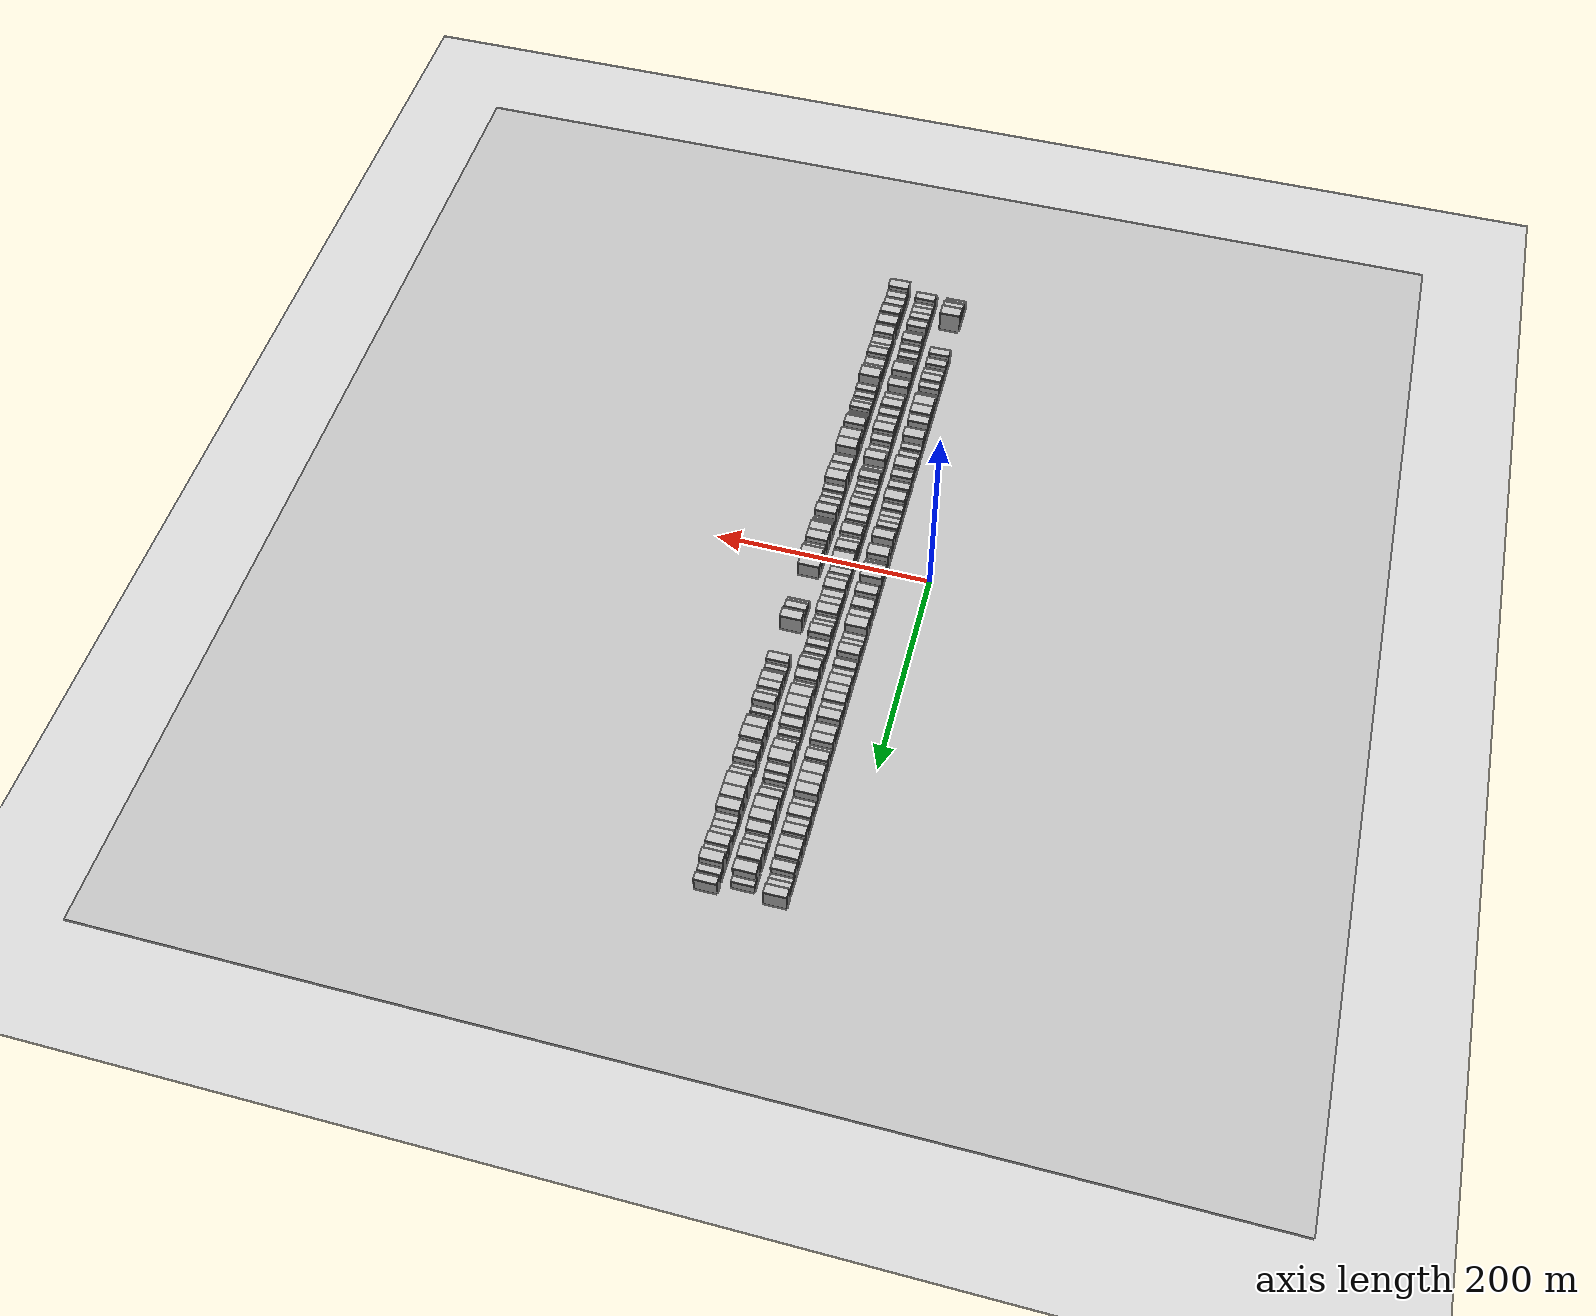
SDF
<?xml version="1.0" encoding="utf-8"?>

<sdf version="1.6">

   <world name="default">

      <gui fullscreen="0">

         <camera name="user_camera">

            <pose>-15 0 4.57585 0 0 0</pose>

            <view_controller>orbit</view_controller>

         </camera>

      </gui>

      <scene>

         <sky>

           <clouds>

             <speed>12</speed>

           </clouds>

         </sky>

         <ambient>0.4 0.4 0.4 1</ambient>

         <background>0.7 0.7 0.7 1</background>

         <shadows>1</shadows>

      </scene>

      <gravity>0 0 -9.8066</gravity>

      <magnetic_field>6e-06 2.3e-05 -4.2e-05</magnetic_field>

      <physics default="0" name="default_physics" type="ode">

         <ode>

            <solver>

               <type>quick</type>

               <iters>10</iters>

               <sor>1.0</sor>

               <use_dynamic_moi_rescaling>0</use_dynamic_moi_rescaling>

            </solver>

            <constraints>

               <cfm>0</cfm>

               <erp>0.2</erp>

               <contact_max_correcting_vel>100</contact_max_correcting_vel>

               <contact_surface_layer>0.001</contact_surface_layer>

            </constraints>

         </ode>

         <max_step_size>0.004</max_step_size>

         <real_time_factor>1</real_time_factor>

         <real_time_update_rate>250</real_time_update_rate>

      </physics>

      <light name="sun" type="directional">

         <cast_shadows>1</cast_shadows>

         <pose>0 0 10 0 0 0</pose>

         <diffuse>0.8 0.8 0.8 1</diffuse>

         <specular>0.2 0.2 0.2 1</specular>

         <attenuation>

            <range>1000</range>

            <constant>0.9</constant>

            <linear>0.01</linear>

            <quadratic>0.001</quadratic>

         </attenuation>

         <direction>-0.5 0.1 -0.9</direction>

      </light>

      <include>

         <name>ground_plane_1</name>

         <uri>model://HANNAS_ground_plane</uri>

         <pose>0 0 0  0 0 0</pose>

      </include>

      <include>

         <name>ground_plane_2</name>

         <uri>model://HANNAS_ground_plane</uri>

         <pose>100 0 0  0 0 0</pose>

      </include>

      <model name="building_1">

         <static>1</static>

         <pose frame="">50.0000 -332.4038 0 0.000000 0.000000 0.000000</pose>

         <link name="link">

            <pose frame="">0 0 6.00 0 0 0</pose>

            <collision name="collision">

               <geometry>

                  <box>

                     <size>20.0000 5.1924 12.0000</size>

                  </box>

               </geometry>

               <max_contacts>10</max_contacts>

               <surface>

                  <contact>

                     <ode/>

                  </contact>

                  <bounce/>

                  <friction>

                     <torsional>

                        <ode/>

                     </torsional>

                     <ode/>

                  </friction>

               </surface>

            </collision>

            <visual name="visual">

               <cast_shadows>0</cast_shadows>

               <geometry>

                  <box>

                     <size>20.0000 5.1924 12.0000</size>

                  </box>

               </geometry>

               <material>

                  <script>

                     <uri>model://HANNAS_wall/materials/scripts</uri>

                     <uri>model://HANNAS_wall/materials/textures</uri>

                     <name>vrc/HANNAS_wall</name>

                  </script>

               </material>

            </visual>

            <self_collide>0</self_collide>

            <enable_wind>0</enable_wind>

            <kinematic>0</kinematic>

         </link>

      </model>

      <model name="building_2">

         <static>1</static>

         <pose frame="">50.0000 -325.5463 0 0.000000 0.000000 0.000000</pose>

         <link name="link">

            <pose frame="">0 0 7.50 0 0 0</pose>

            <collision name="collision">

               <geometry>

                  <box>

                     <size>20.0000 6.5226 15.0000</size>

                  </box>

               </geometry>

               <max_contacts>10</max_contacts>

               <surface>

                  <contact>

                     <ode/>

                  </contact>

                  <bounce/>

                  <friction>

                     <torsional>

                        <ode/>

                     </torsional>

                     <ode/>

                  </friction>

               </surface>

            </collision>

            <visual name="visual">

               <cast_shadows>0</cast_shadows>

               <geometry>

                  <box>

                     <size>20.0000 6.5226 15.0000</size>

                  </box>

               </geometry>

               <material>

                  <script>

                     <uri>model://HANNAS_wall/materials/scripts</uri>

                     <uri>model://HANNAS_wall/materials/textures</uri>

                     <name>vrc/HANNAS_wall</name>

                  </script>

               </material>

            </visual>

            <self_collide>0</self_collide>

            <enable_wind>0</enable_wind>

            <kinematic>0</kinematic>

         </link>

      </model>

      <model name="building_3">

         <static>1</static>

         <pose frame="">50.0000 -317.9399 0 0.000000 0.000000 0.000000</pose>

         <link name="link">

            <pose frame="">0 0 10.50 0 0 0</pose>

            <collision name="collision">

               <geometry>

                  <box>

                     <size>20.0000 8.6902 21.0000</size>

                  </box>

               </geometry>

               <max_contacts>10</max_contacts>

               <surface>

                  <contact>

                     <ode/>

                  </contact>

                  <bounce/>

                  <friction>

                     <torsional>

                        <ode/>

                     </torsional>

                     <ode/>

                  </friction>

               </surface>

            </collision>

            <visual name="visual">

               <cast_shadows>0</cast_shadows>

               <geometry>

                  <box>

                     <size>20.0000 8.6902 21.0000</size>

                  </box>

               </geometry>

               <material>

                  <script>

                     <uri>model://HANNAS_wall/materials/scripts</uri>

                     <uri>model://HANNAS_wall/materials/textures</uri>

                     <name>vrc/HANNAS_wall</name>

                  </script>

               </material>

            </visual>

            <self_collide>0</self_collide>

            <enable_wind>0</enable_wind>

            <kinematic>0</kinematic>

         </link>

      </model>

      <model name="building_4">

         <static>1</static>

         <pose frame="">50.0000 -308.0300 0 0.000000 0.000000 0.000000</pose>

         <link name="link">

            <pose frame="">0 0 12.00 0 0 0</pose>

            <collision name="collision">

               <geometry>

                  <box>

                     <size>20.0000 11.1295 24.0000</size>

                  </box>

               </geometry>

               <max_contacts>10</max_contacts>

               <surface>

                  <contact>

                     <ode/>

                  </contact>

                  <bounce/>

                  <friction>

                     <torsional>

                        <ode/>

                     </torsional>

                     <ode/>

                  </friction>

               </surface>

            </collision>

            <visual name="visual">

               <cast_shadows>0</cast_shadows>

               <geometry>

                  <box>

                     <size>20.0000 11.1295 24.0000</size>

                  </box>

               </geometry>

               <material>

                  <script>

                     <uri>model://HANNAS_wall/materials/scripts</uri>

                     <uri>model://HANNAS_wall/materials/textures</uri>

                     <name>vrc/HANNAS_wall</name>

                  </script>

               </material>

            </visual>

            <self_collide>0</self_collide>

            <enable_wind>0</enable_wind>

            <kinematic>0</kinematic>

         </link>

      </model>

      <model name="building_5">

         <static>1</static>

         <pose frame="">50.0000 -257.8052 0 0.000000 0.000000 0.000000</pose>

         <link name="link">

            <pose frame="">0 0 9.00 0 0 0</pose>

            <collision name="collision">

               <geometry>

                  <box>

                     <size>20.0000 8.4401 18.0000</size>

                  </box>

               </geometry>

               <max_contacts>10</max_contacts>

               <surface>

                  <contact>

                     <ode/>

                  </contact>

                  <bounce/>

                  <friction>

                     <torsional>

                        <ode/>

                     </torsional>

                     <ode/>

                  </friction>

               </surface>

            </collision>

            <visual name="visual">

               <cast_shadows>0</cast_shadows>

               <geometry>

                  <box>

                     <size>20.0000 8.4401 18.0000</size>

                  </box>

               </geometry>

               <material>

                  <script>

                     <uri>model://HANNAS_wall/materials/scripts</uri>

                     <uri>model://HANNAS_wall/materials/textures</uri>

                     <name>vrc/HANNAS_wall</name>

                  </script>

               </material>

            </visual>

            <self_collide>0</self_collide>

            <enable_wind>0</enable_wind>

            <kinematic>0</kinematic>

         </link>

      </model>

      <model name="building_6">

         <static>1</static>

         <pose frame="">50.0000 -250.8896 0 0.000000 0.000000 0.000000</pose>

         <link name="link">

            <pose frame="">0 0 6.00 0 0 0</pose>

            <collision name="collision">

               <geometry>

                  <box>

                     <size>20.0000 5.3911 12.0000</size>

                  </box>

               </geometry>

               <max_contacts>10</max_contacts>

               <surface>

                  <contact>

                     <ode/>

                  </contact>

                  <bounce/>

                  <friction>

                     <torsional>

                        <ode/>

                     </torsional>

                     <ode/>

                  </friction>

               </surface>

            </collision>

            <visual name="visual">

               <cast_shadows>0</cast_shadows>

               <geometry>

                  <box>

                     <size>20.0000 5.3911 12.0000</size>

                  </box>

               </geometry>

               <material>

                  <script>

                     <uri>model://HANNAS_wall/materials/scripts</uri>

                     <uri>model://HANNAS_wall/materials/textures</uri>

                     <name>vrc/HANNAS_wall</name>

                  </script>

               </material>

            </visual>

            <self_collide>0</self_collide>

            <enable_wind>0</enable_wind>

            <kinematic>0</kinematic>

         </link>

      </model>

      <model name="building_7">

         <static>1</static>

         <pose frame="">50.0000 -243.8763 0 0.000000 0.000000 0.000000</pose>

         <link name="link">

            <pose frame="">0 0 9.00 0 0 0</pose>

            <collision name="collision">

               <geometry>

                  <box>

                     <size>20.0000 8.6356 18.0000</size>

                  </box>

               </geometry>

               <max_contacts>10</max_contacts>

               <surface>

                  <contact>

                     <ode/>

                  </contact>

                  <bounce/>

                  <friction>

                     <torsional>

                        <ode/>

                     </torsional>

                     <ode/>

                  </friction>

               </surface>

            </collision>

            <visual name="visual">

               <cast_shadows>0</cast_shadows>

               <geometry>

                  <box>

                     <size>20.0000 8.6356 18.0000</size>

                  </box>

               </geometry>

               <material>

                  <script>

                     <uri>model://HANNAS_wall/materials/scripts</uri>

                     <uri>model://HANNAS_wall/materials/textures</uri>

                     <name>vrc/HANNAS_wall</name>

                  </script>

               </material>

            </visual>

            <self_collide>0</self_collide>

            <enable_wind>0</enable_wind>

            <kinematic>0</kinematic>

         </link>

      </model>

      <model name="building_8">

         <static>1</static>

         <pose frame="">50.0000 -236.6491 0 0.000000 0.000000 0.000000</pose>

         <link name="link">

            <pose frame="">0 0 6.00 0 0 0</pose>

            <collision name="collision">

               <geometry>

                  <box>

                     <size>20.0000 5.8187 12.0000</size>

                  </box>

               </geometry>

               <max_contacts>10</max_contacts>

               <surface>

                  <contact>

                     <ode/>

                  </contact>

                  <bounce/>

                  <friction>

                     <torsional>

                        <ode/>

                     </torsional>

                     <ode/>

                  </friction>

               </surface>

            </collision>

            <visual name="visual">

               <cast_shadows>0</cast_shadows>

               <geometry>

                  <box>

                     <size>20.0000 5.8187 12.0000</size>

                  </box>

               </geometry>

               <material>

                  <script>

                     <uri>model://HANNAS_wall/materials/scripts</uri>

                     <uri>model://HANNAS_wall/materials/textures</uri>

                     <name>vrc/HANNAS_wall</name>

                  </script>

               </material>

            </visual>

            <self_collide>0</self_collide>

            <enable_wind>0</enable_wind>

            <kinematic>0</kinematic>

         </link>

      </model>

      <model name="building_9">

         <static>1</static>

         <pose frame="">50.0000 -230.1045 0 0.000000 0.000000 0.000000</pose>

         <link name="link">

            <pose frame="">0 0 9.00 0 0 0</pose>

            <collision name="collision">

               <geometry>

                  <box>

                     <size>20.0000 7.2705 18.0000</size>

                  </box>

               </geometry>

               <max_contacts>10</max_contacts>

               <surface>

                  <contact>

                     <ode/>

                  </contact>

                  <bounce/>

                  <friction>

                     <torsional>

                        <ode/>

                     </torsional>

                     <ode/>

                  </friction>

               </surface>

            </collision>

            <visual name="visual">

               <cast_shadows>0</cast_shadows>

               <geometry>

                  <box>

                     <size>20.0000 7.2705 18.0000</size>

                  </box>

               </geometry>

               <material>

                  <script>

                     <uri>model://HANNAS_wall/materials/scripts</uri>

                     <uri>model://HANNAS_wall/materials/textures</uri>

                     <name>vrc/HANNAS_wall</name>

                  </script>

               </material>

            </visual>

            <self_collide>0</self_collide>

            <enable_wind>0</enable_wind>

            <kinematic>0</kinematic>

         </link>

      </model>

      <model name="building_10">

         <static>1</static>

         <pose frame="">50.0000 -221.1485 0 0.000000 0.000000 0.000000</pose>

         <link name="link">

            <pose frame="">0 0 10.50 0 0 0</pose>

            <collision name="collision">

               <geometry>

                  <box>

                     <size>20.0000 8.6415 21.0000</size>

                  </box>

               </geometry>

               <max_contacts>10</max_contacts>

               <surface>

                  <contact>

                     <ode/>

                  </contact>

                  <bounce/>

                  <friction>

                     <torsional>

                        <ode/>

                     </torsional>

                     <ode/>

                  </friction>

               </surface>

            </collision>

            <visual name="visual">

               <cast_shadows>0</cast_shadows>

               <geometry>

                  <box>

                     <size>20.0000 8.6415 21.0000</size>

                  </box>

               </geometry>

               <material>

                  <script>

                     <uri>model://HANNAS_wall/materials/scripts</uri>

                     <uri>model://HANNAS_wall/materials/textures</uri>

                     <name>vrc/HANNAS_wall</name>

                  </script>

               </material>

            </visual>

            <self_collide>0</self_collide>

            <enable_wind>0</enable_wind>

            <kinematic>0</kinematic>

         </link>

      </model>

      <model name="building_11">

         <static>1</static>

         <pose frame="">50.0000 -213.1684 0 0.000000 0.000000 0.000000</pose>

         <link name="link">

            <pose frame="">0 0 9.00 0 0 0</pose>

            <collision name="collision">

               <geometry>

                  <box>

                     <size>20.0000 7.3188 18.0000</size>

                  </box>

               </geometry>

               <max_contacts>10</max_contacts>

               <surface>

                  <contact>

                     <ode/>

                  </contact>

                  <bounce/>

                  <friction>

                     <torsional>

                        <ode/>

                     </torsional>

                     <ode/>

                  </friction>

               </surface>

            </collision>

            <visual name="visual">

               <cast_shadows>0</cast_shadows>

               <geometry>

                  <box>

                     <size>20.0000 7.3188 18.0000</size>

                  </box>

               </geometry>

               <material>

                  <script>

                     <uri>model://HANNAS_wall/materials/scripts</uri>

                     <uri>model://HANNAS_wall/materials/textures</uri>

                     <name>vrc/HANNAS_wall</name>

                  </script>

               </material>

            </visual>

            <self_collide>0</self_collide>

            <enable_wind>0</enable_wind>

            <kinematic>0</kinematic>

         </link>

      </model>

      <model name="building_12">

         <static>1</static>

         <pose frame="">50.0000 -204.6580 0 0.000000 0.000000 0.000000</pose>

         <link name="link">

            <pose frame="">0 0 6.00 0 0 0</pose>

            <collision name="collision">

               <geometry>

                  <box>

                     <size>20.0000 5.7020 12.0000</size>

                  </box>

               </geometry>

               <max_contacts>10</max_contacts>

               <surface>

                  <contact>

                     <ode/>

                  </contact>

                  <bounce/>

                  <friction>

                     <torsional>

                        <ode/>

                     </torsional>

                     <ode/>

                  </friction>

               </surface>

            </collision>

            <visual name="visual">

               <cast_shadows>0</cast_shadows>

               <geometry>

                  <box>

                     <size>20.0000 5.7020 12.0000</size>

                  </box>

               </geometry>

               <material>

                  <script>

                     <uri>model://HANNAS_wall/materials/scripts</uri>

                     <uri>model://HANNAS_wall/materials/textures</uri>

                     <name>vrc/HANNAS_wall</name>

                  </script>

               </material>

            </visual>

            <self_collide>0</self_collide>

            <enable_wind>0</enable_wind>

            <kinematic>0</kinematic>

         </link>

      </model>

      <model name="building_13">

         <static>1</static>

         <pose frame="">50.0000 -197.9033 0 0.000000 0.000000 0.000000</pose>

         <link name="link">

            <pose frame="">0 0 6.00 0 0 0</pose>

            <collision name="collision">

               <geometry>

                  <box>

                     <size>20.0000 5.8075 12.0000</size>

                  </box>

               </geometry>

               <max_contacts>10</max_contacts>

               <surface>

                  <contact>

                     <ode/>

                  </contact>

                  <bounce/>

                  <friction>

                     <torsional>

                        <ode/>

                     </torsional>

                     <ode/>

                  </friction>

               </surface>

            </collision>

            <visual name="visual">

               <cast_shadows>0</cast_shadows>

               <geometry>

                  <box>

                     <size>20.0000 5.8075 12.0000</size>

                  </box>

               </geometry>

               <material>

                  <script>

                     <uri>model://HANNAS_wall/materials/scripts</uri>

                     <uri>model://HANNAS_wall/materials/textures</uri>

                     <name>vrc/HANNAS_wall</name>

                  </script>

               </material>

            </visual>

            <self_collide>0</self_collide>

            <enable_wind>0</enable_wind>

            <kinematic>0</kinematic>

         </link>

      </model>

      <model name="building_14">

         <static>1</static>

         <pose frame="">50.0000 -189.0731 0 0.000000 0.000000 0.000000</pose>

         <link name="link">

            <pose frame="">0 0 12.00 0 0 0</pose>

            <collision name="collision">

               <geometry>

                  <box>

                     <size>20.0000 11.8528 24.0000</size>

                  </box>

               </geometry>

               <max_contacts>10</max_contacts>

               <surface>

                  <contact>

                     <ode/>

                  </contact>

                  <bounce/>

                  <friction>

                     <torsional>

                        <ode/>

                     </torsional>

                     <ode/>

                  </friction>

               </surface>

            </collision>

            <visual name="visual">

               <cast_shadows>0</cast_shadows>

               <geometry>

                  <box>

                     <size>20.0000 11.8528 24.0000</size>

                  </box>

               </geometry>

               <material>

                  <script>

                     <uri>model://HANNAS_wall/materials/scripts</uri>

                     <uri>model://HANNAS_wall/materials/textures</uri>

                     <name>vrc/HANNAS_wall</name>

                  </script>

               </material>

            </visual>

            <self_collide>0</self_collide>

            <enable_wind>0</enable_wind>

            <kinematic>0</kinematic>

         </link>

      </model>

      <model name="building_15">

         <static>1</static>

         <pose frame="">50.0000 -177.5735 0 0.000000 0.000000 0.000000</pose>

         <link name="link">

            <pose frame="">0 0 12.00 0 0 0</pose>

            <collision name="collision">

               <geometry>

                  <box>

                     <size>20.0000 11.1463 24.0000</size>

                  </box>

               </geometry>

               <max_contacts>10</max_contacts>

               <surface>

                  <contact>

                     <ode/>

                  </contact>

                  <bounce/>

                  <friction>

                     <torsional>

                        <ode/>

                     </torsional>

                     <ode/>

                  </friction>

               </surface>

            </collision>

            <visual name="visual">

               <cast_shadows>0</cast_shadows>

               <geometry>

                  <box>

                     <size>20.0000 11.1463 24.0000</size>

                  </box>

               </geometry>

               <material>

                  <script>

                     <uri>model://HANNAS_wall/materials/scripts</uri>

                     <uri>model://HANNAS_wall/materials/textures</uri>

                     <name>vrc/HANNAS_wall</name>

                  </script>

               </material>

            </visual>

            <self_collide>0</self_collide>

            <enable_wind>0</enable_wind>

            <kinematic>0</kinematic>

         </link>

      </model>

      <model name="building_16">

         <static>1</static>

         <pose frame="">50.0000 -167.2819 0 0.000000 0.000000 0.000000</pose>

         <link name="link">

            <pose frame="">0 0 10.50 0 0 0</pose>

            <collision name="collision">

               <geometry>

                  <box>

                     <size>20.0000 9.4371 21.0000</size>

                  </box>

               </geometry>

               <max_contacts>10</max_contacts>

               <surface>

                  <contact>

                     <ode/>

                  </contact>

                  <bounce/>

                  <friction>

                     <torsional>

                        <ode/>

                     </torsional>

                     <ode/>

                  </friction>

               </surface>

            </collision>

            <visual name="visual">

               <cast_shadows>0</cast_shadows>

               <geometry>

                  <box>

                     <size>20.0000 9.4371 21.0000</size>

                  </box>

               </geometry>

               <material>

                  <script>

                     <uri>model://HANNAS_wall/materials/scripts</uri>

                     <uri>model://HANNAS_wall/materials/textures</uri>

                     <name>vrc/HANNAS_wall</name>

                  </script>

               </material>

            </visual>

            <self_collide>0</self_collide>

            <enable_wind>0</enable_wind>

            <kinematic>0</kinematic>

         </link>

      </model>

      <model name="building_17">

         <static>1</static>

         <pose frame="">50.0000 -156.0513 0 0.000000 0.000000 0.000000</pose>

         <link name="link">

            <pose frame="">0 0 7.50 0 0 0</pose>

            <collision name="collision">

               <geometry>

                  <box>

                     <size>20.0000 7.0241 15.0000</size>

                  </box>

               </geometry>

               <max_contacts>10</max_contacts>

               <surface>

                  <contact>

                     <ode/>

                  </contact>

                  <bounce/>

                  <friction>

                     <torsional>

                        <ode/>

                     </torsional>

                     <ode/>

                  </friction>

               </surface>

            </collision>

            <visual name="visual">

               <cast_shadows>0</cast_shadows>

               <geometry>

                  <box>

                     <size>20.0000 7.0241 15.0000</size>

                  </box>

               </geometry>

               <material>

                  <script>

                     <uri>model://HANNAS_wall/materials/scripts</uri>

                     <uri>model://HANNAS_wall/materials/textures</uri>

                     <name>vrc/HANNAS_wall</name>

                  </script>

               </material>

            </visual>

            <self_collide>0</self_collide>

            <enable_wind>0</enable_wind>

            <kinematic>0</kinematic>

         </link>

      </model>

      <model name="building_18">

         <static>1</static>

         <pose frame="">50.0000 -146.9689 0 0.000000 0.000000 0.000000</pose>

         <link name="link">

            <pose frame="">0 0 12.00 0 0 0</pose>

            <collision name="collision">

               <geometry>

                  <box>

                     <size>20.0000 11.1406 24.0000</size>

                  </box>

               </geometry>

               <max_contacts>10</max_contacts>

               <surface>

                  <contact>

                     <ode/>

                  </contact>

                  <bounce/>

                  <friction>

                     <torsional>

                        <ode/>

                     </torsional>

                     <ode/>

                  </friction>

               </surface>

            </collision>

            <visual name="visual">

               <cast_shadows>0</cast_shadows>

               <geometry>

                  <box>

                     <size>20.0000 11.1406 24.0000</size>

                  </box>

               </geometry>

               <material>

                  <script>

                     <uri>model://HANNAS_wall/materials/scripts</uri>

                     <uri>model://HANNAS_wall/materials/textures</uri>

                     <name>vrc/HANNAS_wall</name>

                  </script>

               </material>

            </visual>

            <self_collide>0</self_collide>

            <enable_wind>0</enable_wind>

            <kinematic>0</kinematic>

         </link>

      </model>

      <model name="building_19">

         <static>1</static>

         <pose frame="">50.0000 -137.1021 0 0.000000 0.000000 0.000000</pose>

         <link name="link">

            <pose frame="">0 0 7.50 0 0 0</pose>

            <collision name="collision">

               <geometry>

                  <box>

                     <size>20.0000 6.5930 15.0000</size>

                  </box>

               </geometry>

               <max_contacts>10</max_contacts>

               <surface>

                  <contact>

                     <ode/>

                  </contact>

                  <bounce/>

                  <friction>

                     <torsional>

                        <ode/>

                     </torsional>

                     <ode/>

                  </friction>

               </surface>

            </collision>

            <visual name="visual">

               <cast_shadows>0</cast_shadows>

               <geometry>

                  <box>

                     <size>20.0000 6.5930 15.0000</size>

                  </box>

               </geometry>

               <material>

                  <script>

                     <uri>model://HANNAS_wall/materials/scripts</uri>

                     <uri>model://HANNAS_wall/materials/textures</uri>

                     <name>vrc/HANNAS_wall</name>

                  </script>

               </material>

            </visual>

            <self_collide>0</self_collide>

            <enable_wind>0</enable_wind>

            <kinematic>0</kinematic>

         </link>

      </model>

      <model name="building_20">

         <static>1</static>

         <pose frame="">50.0000 -127.6321 0 0.000000 0.000000 0.000000</pose>

         <link name="link">

            <pose frame="">0 0 7.50 0 0 0</pose>

            <collision name="collision">

               <geometry>

                  <box>

                     <size>20.0000 6.3470 15.0000</size>

                  </box>

               </geometry>

               <max_contacts>10</max_contacts>

               <surface>

                  <contact>

                     <ode/>

                  </contact>

                  <bounce/>

                  <friction>

                     <torsional>

                        <ode/>

                     </torsional>

                     <ode/>

                  </friction>

               </surface>

            </collision>

            <visual name="visual">

               <cast_shadows>0</cast_shadows>

               <geometry>

                  <box>

                     <size>20.0000 6.3470 15.0000</size>

                  </box>

               </geometry>

               <material>

                  <script>

                     <uri>model://HANNAS_wall/materials/scripts</uri>

                     <uri>model://HANNAS_wall/materials/textures</uri>

                     <name>vrc/HANNAS_wall</name>

                  </script>

               </material>

            </visual>

            <self_collide>0</self_collide>

            <enable_wind>0</enable_wind>

            <kinematic>0</kinematic>

         </link>

      </model>

      <model name="building_21">

         <static>1</static>

         <pose frame="">50.0000 -120.0750 0 0.000000 0.000000 0.000000</pose>

         <link name="link">

            <pose frame="">0 0 7.50 0 0 0</pose>

            <collision name="collision">

               <geometry>

                  <box>

                     <size>20.0000 6.7672 15.0000</size>

                  </box>

               </geometry>

               <max_contacts>10</max_contacts>

               <surface>

                  <contact>

                     <ode/>

                  </contact>

                  <bounce/>

                  <friction>

                     <torsional>

                        <ode/>

                     </torsional>

                     <ode/>

                  </friction>

               </surface>

            </collision>

            <visual name="visual">

               <cast_shadows>0</cast_shadows>

               <geometry>

                  <box>

                     <size>20.0000 6.7672 15.0000</size>

                  </box>

               </geometry>

               <material>

                  <script>

                     <uri>model://HANNAS_wall/materials/scripts</uri>

                     <uri>model://HANNAS_wall/materials/textures</uri>

                     <name>vrc/HANNAS_wall</name>

                  </script>

               </material>

            </visual>

            <self_collide>0</self_collide>

            <enable_wind>0</enable_wind>

            <kinematic>0</kinematic>

         </link>

      </model>

      <model name="building_22">

         <static>1</static>

         <pose frame="">50.0000 -110.7855 0 0.000000 0.000000 0.000000</pose>

         <link name="link">

            <pose frame="">0 0 12.00 0 0 0</pose>

            <collision name="collision">

               <geometry>

                  <box>

                     <size>20.0000 11.8119 24.0000</size>

                  </box>

               </geometry>

               <max_contacts>10</max_contacts>

               <surface>

                  <contact>

                     <ode/>

                  </contact>

                  <bounce/>

                  <friction>

                     <torsional>

                        <ode/>

                     </torsional>

                     <ode/>

                  </friction>

               </surface>

            </collision>

            <visual name="visual">

               <cast_shadows>0</cast_shadows>

               <geometry>

                  <box>

                     <size>20.0000 11.8119 24.0000</size>

                  </box>

               </geometry>

               <material>

                  <script>

                     <uri>model://HANNAS_wall/materials/scripts</uri>

                     <uri>model://HANNAS_wall/materials/textures</uri>

                     <name>vrc/HANNAS_wall</name>

                  </script>

               </material>

            </visual>

            <self_collide>0</self_collide>

            <enable_wind>0</enable_wind>

            <kinematic>0</kinematic>

         </link>

      </model>

      <model name="building_23">

         <static>1</static>

         <pose frame="">50.0000 -98.5917 0 0.000000 0.000000 0.000000</pose>

         <link name="link">

            <pose frame="">0 0 10.50 0 0 0</pose>

            <collision name="collision">

               <geometry>

                  <box>

                     <size>20.0000 8.5757 21.0000</size>

                  </box>

               </geometry>

               <max_contacts>10</max_contacts>

               <surface>

                  <contact>

                     <ode/>

                  </contact>

                  <bounce/>

                  <friction>

                     <torsional>

                        <ode/>

                     </torsional>

                     <ode/>

                  </friction>

               </surface>

            </collision>

            <visual name="visual">

               <cast_shadows>0</cast_shadows>

               <geometry>

                  <box>

                     <size>20.0000 8.5757 21.0000</size>

                  </box>

               </geometry>

               <material>

                  <script>

                     <uri>model://HANNAS_wall/materials/scripts</uri>

                     <uri>model://HANNAS_wall/materials/textures</uri>

                     <name>vrc/HANNAS_wall</name>

                  </script>

               </material>

            </visual>

            <self_collide>0</self_collide>

            <enable_wind>0</enable_wind>

            <kinematic>0</kinematic>

         </link>

      </model>

      <model name="building_24">

         <static>1</static>

         <pose frame="">50.0000 -87.3351 0 0.000000 0.000000 0.000000</pose>

         <link name="link">

            <pose frame="">0 0 9.00 0 0 0</pose>

            <collision name="collision">

               <geometry>

                  <box>

                     <size>20.0000 7.9375 18.0000</size>

                  </box>

               </geometry>

               <max_contacts>10</max_contacts>

               <surface>

                  <contact>

                     <ode/>

                  </contact>

                  <bounce/>

                  <friction>

                     <torsional>

                        <ode/>

                     </torsional>

                     <ode/>

                  </friction>

               </surface>

            </collision>

            <visual name="visual">

               <cast_shadows>0</cast_shadows>

               <geometry>

                  <box>

                     <size>20.0000 7.9375 18.0000</size>

                  </box>

               </geometry>

               <material>

                  <script>

                     <uri>model://HANNAS_wall/materials/scripts</uri>

                     <uri>model://HANNAS_wall/materials/textures</uri>

                     <name>vrc/HANNAS_wall</name>

                  </script>

               </material>

            </visual>

            <self_collide>0</self_collide>

            <enable_wind>0</enable_wind>

            <kinematic>0</kinematic>

         </link>

      </model>

      <model name="building_25">

         <static>1</static>

         <pose frame="">50.0000 -78.8587 0 0.000000 0.000000 0.000000</pose>

         <link name="link">

            <pose frame="">0 0 6.00 0 0 0</pose>

            <collision name="collision">

               <geometry>

                  <box>

                     <size>20.0000 5.0152 12.0000</size>

                  </box>

               </geometry>

               <max_contacts>10</max_contacts>

               <surface>

                  <contact>

                     <ode/>

                  </contact>

                  <bounce/>

                  <friction>

                     <torsional>

                        <ode/>

                     </torsional>

                     <ode/>

                  </friction>

               </surface>

            </collision>

            <visual name="visual">

               <cast_shadows>0</cast_shadows>

               <geometry>

                  <box>

                     <size>20.0000 5.0152 12.0000</size>

                  </box>

               </geometry>

               <material>

                  <script>

                     <uri>model://HANNAS_wall/materials/scripts</uri>

                     <uri>model://HANNAS_wall/materials/textures</uri>

                     <name>vrc/HANNAS_wall</name>

                  </script>

               </material>

            </visual>

            <self_collide>0</self_collide>

            <enable_wind>0</enable_wind>

            <kinematic>0</kinematic>

         </link>

      </model>

      <model name="building_26">

         <static>1</static>

         <pose frame="">50.0000 -70.6968 0 0.000000 0.000000 0.000000</pose>

         <link name="link">

            <pose frame="">0 0 12.00 0 0 0</pose>

            <collision name="collision">

               <geometry>

                  <box>

                     <size>20.0000 11.3087 24.0000</size>

                  </box>

               </geometry>

               <max_contacts>10</max_contacts>

               <surface>

                  <contact>

                     <ode/>

                  </contact>

                  <bounce/>

                  <friction>

                     <torsional>

                        <ode/>

                     </torsional>

                     <ode/>

                  </friction>

               </surface>

            </collision>

            <visual name="visual">

               <cast_shadows>0</cast_shadows>

               <geometry>

                  <box>

                     <size>20.0000 11.3087 24.0000</size>

                  </box>

               </geometry>

               <material>

                  <script>

                     <uri>model://HANNAS_wall/materials/scripts</uri>

                     <uri>model://HANNAS_wall/materials/textures</uri>

                     <name>vrc/HANNAS_wall</name>

                  </script>

               </material>

            </visual>

            <self_collide>0</self_collide>

            <enable_wind>0</enable_wind>

            <kinematic>0</kinematic>

         </link>

      </model>

      <model name="building_27">

         <static>1</static>

         <pose frame="">50.0000 -61.3686 0 0.000000 0.000000 0.000000</pose>

         <link name="link">

            <pose frame="">0 0 9.00 0 0 0</pose>

            <collision name="collision">

               <geometry>

                  <box>

                     <size>20.0000 7.3478 18.0000</size>

                  </box>

               </geometry>

               <max_contacts>10</max_contacts>

               <surface>

                  <contact>

                     <ode/>

                  </contact>

                  <bounce/>

                  <friction>

                     <torsional>

                        <ode/>

                     </torsional>

                     <ode/>

                  </friction>

               </surface>

            </collision>

            <visual name="visual">

               <cast_shadows>0</cast_shadows>

               <geometry>

                  <box>

                     <size>20.0000 7.3478 18.0000</size>

                  </box>

               </geometry>

               <material>

                  <script>

                     <uri>model://HANNAS_wall/materials/scripts</uri>

                     <uri>model://HANNAS_wall/materials/textures</uri>

                     <name>vrc/HANNAS_wall</name>

                  </script>

               </material>

            </visual>

            <self_collide>0</self_collide>

            <enable_wind>0</enable_wind>

            <kinematic>0</kinematic>

         </link>

      </model>

      <model name="building_28">

         <static>1</static>

         <pose frame="">50.0000 -54.6377 0 0.000000 0.000000 0.000000</pose>

         <link name="link">

            <pose frame="">0 0 7.50 0 0 0</pose>

            <collision name="collision">

               <geometry>

                  <box>

                     <size>20.0000 6.1139 15.0000</size>

                  </box>

               </geometry>

               <max_contacts>10</max_contacts>

               <surface>

                  <contact>

                     <ode/>

                  </contact>

                  <bounce/>

                  <friction>

                     <torsional>

                        <ode/>

                     </torsional>

                     <ode/>

                  </friction>

               </surface>

            </collision>

            <visual name="visual">

               <cast_shadows>0</cast_shadows>

               <geometry>

                  <box>

                     <size>20.0000 6.1139 15.0000</size>

                  </box>

               </geometry>

               <material>

                  <script>

                     <uri>model://HANNAS_wall/materials/scripts</uri>

                     <uri>model://HANNAS_wall/materials/textures</uri>

                     <name>vrc/HANNAS_wall</name>

                  </script>

               </material>

            </visual>

            <self_collide>0</self_collide>

            <enable_wind>0</enable_wind>

            <kinematic>0</kinematic>

         </link>

      </model>

      <model name="building_29">

         <static>1</static>

         <pose frame="">50.0000 -48.5180 0 0.000000 0.000000 0.000000</pose>

         <link name="link">

            <pose frame="">0 0 7.50 0 0 0</pose>

            <collision name="collision">

               <geometry>

                  <box>

                     <size>20.0000 6.1255 15.0000</size>

                  </box>

               </geometry>

               <max_contacts>10</max_contacts>

               <surface>

                  <contact>

                     <ode/>

                  </contact>

                  <bounce/>

                  <friction>

                     <torsional>

                        <ode/>

                     </torsional>

                     <ode/>

                  </friction>

               </surface>

            </collision>

            <visual name="visual">

               <cast_shadows>0</cast_shadows>

               <geometry>

                  <box>

                     <size>20.0000 6.1255 15.0000</size>

                  </box>

               </geometry>

               <material>

                  <script>

                     <uri>model://HANNAS_wall/materials/scripts</uri>

                     <uri>model://HANNAS_wall/materials/textures</uri>

                     <name>vrc/HANNAS_wall</name>

                  </script>

               </material>

            </visual>

            <self_collide>0</self_collide>

            <enable_wind>0</enable_wind>

            <kinematic>0</kinematic>

         </link>

      </model>

      <model name="building_30">

         <static>1</static>

         <pose frame="">50.0000 -42.2599 0 0.000000 0.000000 0.000000</pose>

         <link name="link">

            <pose frame="">0 0 7.50 0 0 0</pose>

            <collision name="collision">

               <geometry>

                  <box>

                     <size>20.0000 6.3905 15.0000</size>

                  </box>

               </geometry>

               <max_contacts>10</max_contacts>

               <surface>

                  <contact>

                     <ode/>

                  </contact>

                  <bounce/>

                  <friction>

                     <torsional>

                        <ode/>

                     </torsional>

                     <ode/>

                  </friction>

               </surface>

            </collision>

            <visual name="visual">

               <cast_shadows>0</cast_shadows>

               <geometry>

                  <box>

                     <size>20.0000 6.3905 15.0000</size>

                  </box>

               </geometry>

               <material>

                  <script>

                     <uri>model://HANNAS_wall/materials/scripts</uri>

                     <uri>model://HANNAS_wall/materials/textures</uri>

                     <name>vrc/HANNAS_wall</name>

                  </script>

               </material>

            </visual>

            <self_collide>0</self_collide>

            <enable_wind>0</enable_wind>

            <kinematic>0</kinematic>

         </link>

      </model>

      <model name="building_31">

         <static>1</static>

         <pose frame="">50.0000 -33.0405 0 0.000000 0.000000 0.000000</pose>

         <link name="link">

            <pose frame="">0 0 7.50 0 0 0</pose>

            <collision name="collision">

               <geometry>

                  <box>

                     <size>20.0000 6.0484 15.0000</size>

                  </box>

               </geometry>

               <max_contacts>10</max_contacts>

               <surface>

                  <contact>

                     <ode/>

                  </contact>

                  <bounce/>

                  <friction>

                     <torsional>

                        <ode/>

                     </torsional>

                     <ode/>

                  </friction>

               </surface>

            </collision>

            <visual name="visual">

               <cast_shadows>0</cast_shadows>

               <geometry>

                  <box>

                     <size>20.0000 6.0484 15.0000</size>

                  </box>

               </geometry>

               <material>

                  <script>

                     <uri>model://HANNAS_wall/materials/scripts</uri>

                     <uri>model://HANNAS_wall/materials/textures</uri>

                     <name>vrc/HANNAS_wall</name>

                  </script>

               </material>

            </visual>

            <self_collide>0</self_collide>

            <enable_wind>0</enable_wind>

            <kinematic>0</kinematic>

         </link>

      </model>

      <model name="building_32">

         <static>1</static>

         <pose frame="">50.0000 -24.8955 0 0.000000 0.000000 0.000000</pose>

         <link name="link">

            <pose frame="">0 0 12.00 0 0 0</pose>

            <collision name="collision">

               <geometry>

                  <box>

                     <size>20.0000 10.2414 24.0000</size>

                  </box>

               </geometry>

               <max_contacts>10</max_contacts>

               <surface>

                  <contact>

                     <ode/>

                  </contact>

                  <bounce/>

                  <friction>

                     <torsional>

                        <ode/>

                     </torsional>

                     <ode/>

                  </friction>

               </surface>

            </collision>

            <visual name="visual">

               <cast_shadows>0</cast_shadows>

               <geometry>

                  <box>

                     <size>20.0000 10.2414 24.0000</size>

                  </box>

               </geometry>

               <material>

                  <script>

                     <uri>model://HANNAS_wall/materials/scripts</uri>

                     <uri>model://HANNAS_wall/materials/textures</uri>

                     <name>vrc/HANNAS_wall</name>

                  </script>

               </material>

            </visual>

            <self_collide>0</self_collide>

            <enable_wind>0</enable_wind>

            <kinematic>0</kinematic>

         </link>

      </model>

      <model name="building_33">

         <static>1</static>

         <pose frame="">50.0000 -15.2705 0 0.000000 0.000000 0.000000</pose>

         <link name="link">

            <pose frame="">0 0 6.00 0 0 0</pose>

            <collision name="collision">

               <geometry>

                  <box>

                     <size>20.0000 5.0086 12.0000</size>

                  </box>

               </geometry>

               <max_contacts>10</max_contacts>

               <surface>

                  <contact>

                     <ode/>

                  </contact>

                  <bounce/>

                  <friction>

                     <torsional>

                        <ode/>

                     </torsional>

                     <ode/>

                  </friction>

               </surface>

            </collision>

            <visual name="visual">

               <cast_shadows>0</cast_shadows>

               <geometry>

                  <box>

                     <size>20.0000 5.0086 12.0000</size>

                  </box>

               </geometry>

               <material>

                  <script>

                     <uri>model://HANNAS_wall/materials/scripts</uri>

                     <uri>model://HANNAS_wall/materials/textures</uri>

                     <name>vrc/HANNAS_wall</name>

                  </script>

               </material>

            </visual>

            <self_collide>0</self_collide>

            <enable_wind>0</enable_wind>

            <kinematic>0</kinematic>

         </link>

      </model>

      <model name="building_34">

         <static>1</static>

         <pose frame="">50.0000 -6.0178 0 0.000000 0.000000 0.000000</pose>

         <link name="link">

            <pose frame="">0 0 12.00 0 0 0</pose>

            <collision name="collision">

               <geometry>

                  <box>

                     <size>20.0000 11.4968 24.0000</size>

                  </box>

               </geometry>

               <max_contacts>10</max_contacts>

               <surface>

                  <contact>

                     <ode/>

                  </contact>

                  <bounce/>

                  <friction>

                     <torsional>

                        <ode/>

                     </torsional>

                     <ode/>

                  </friction>

               </surface>

            </collision>

            <visual name="visual">

               <cast_shadows>0</cast_shadows>

               <geometry>

                  <box>

                     <size>20.0000 11.4968 24.0000</size>

                  </box>

               </geometry>

               <material>

                  <script>

                     <uri>model://HANNAS_wall/materials/scripts</uri>

                     <uri>model://HANNAS_wall/materials/textures</uri>

                     <name>vrc/HANNAS_wall</name>

                  </script>

               </material>

            </visual>

            <self_collide>0</self_collide>

            <enable_wind>0</enable_wind>

            <kinematic>0</kinematic>

         </link>

      </model>

      <model name="building_35">

         <static>1</static>

         <pose frame="">50.0000 3.2100 0 0.000000 0.000000 0.000000</pose>

         <link name="link">

            <pose frame="">0 0 7.50 0 0 0</pose>

            <collision name="collision">

               <geometry>

                  <box>

                     <size>20.0000 6.9588 15.0000</size>

                  </box>

               </geometry>

               <max_contacts>10</max_contacts>

               <surface>

                  <contact>

                     <ode/>

                  </contact>

                  <bounce/>

                  <friction>

                     <torsional>

                        <ode/>

                     </torsional>

                     <ode/>

                  </friction>

               </surface>

            </collision>

            <visual name="visual">

               <cast_shadows>0</cast_shadows>

               <geometry>

                  <box>

                     <size>20.0000 6.9588 15.0000</size>

                  </box>

               </geometry>

               <material>

                  <script>

                     <uri>model://HANNAS_wall/materials/scripts</uri>

                     <uri>model://HANNAS_wall/materials/textures</uri>

                     <name>vrc/HANNAS_wall</name>

                  </script>

               </material>

            </visual>

            <self_collide>0</self_collide>

            <enable_wind>0</enable_wind>

            <kinematic>0</kinematic>

         </link>

      </model>

      <model name="building_36">

         <static>1</static>

         <pose frame="">50.0000 10.9583 0 0.000000 0.000000 0.000000</pose>

         <link name="link">

            <pose frame="">0 0 10.50 0 0 0</pose>

            <collision name="collision">

               <geometry>

                  <box>

                     <size>20.0000 8.5380 21.0000</size>

                  </box>

               </geometry>

               <max_contacts>10</max_contacts>

               <surface>

                  <contact>

                     <ode/>

                  </contact>

                  <bounce/>

                  <friction>

                     <torsional>

                        <ode/>

                     </torsional>

                     <ode/>

                  </friction>

               </surface>

            </collision>

            <visual name="visual">

               <cast_shadows>0</cast_shadows>

               <geometry>

                  <box>

                     <size>20.0000 8.5380 21.0000</size>

                  </box>

               </geometry>

               <material>

                  <script>

                     <uri>model://HANNAS_wall/materials/scripts</uri>

                     <uri>model://HANNAS_wall/materials/textures</uri>

                     <name>vrc/HANNAS_wall</name>

                  </script>

               </material>

            </visual>

            <self_collide>0</self_collide>

            <enable_wind>0</enable_wind>

            <kinematic>0</kinematic>

         </link>

      </model>

      <model name="building_37">

         <static>1</static>

         <pose frame="">50.0000 20.0570 0 0.000000 0.000000 0.000000</pose>

         <link name="link">

            <pose frame="">0 0 12.00 0 0 0</pose>

            <collision name="collision">

               <geometry>

                  <box>

                     <size>20.0000 9.6595 24.0000</size>

                  </box>

               </geometry>

               <max_contacts>10</max_contacts>

               <surface>

                  <contact>

                     <ode/>

                  </contact>

                  <bounce/>

                  <friction>

                     <torsional>

                        <ode/>

                     </torsional>

                     <ode/>

                  </friction>

               </surface>

            </collision>

            <visual name="visual">

               <cast_shadows>0</cast_shadows>

               <geometry>

                  <box>

                     <size>20.0000 9.6595 24.0000</size>

                  </box>

               </geometry>

               <material>

                  <script>

                     <uri>model://HANNAS_wall/materials/scripts</uri>

                     <uri>model://HANNAS_wall/materials/textures</uri>

                     <name>vrc/HANNAS_wall</name>

                  </script>

               </material>

            </visual>

            <self_collide>0</self_collide>

            <enable_wind>0</enable_wind>

            <kinematic>0</kinematic>

         </link>

      </model>

      <model name="building_38">

         <static>1</static>

         <pose frame="">50.0000 29.8656 0 0.000000 0.000000 0.000000</pose>

         <link name="link">

            <pose frame="">0 0 6.00 0 0 0</pose>

            <collision name="collision">

               <geometry>

                  <box>

                     <size>20.0000 5.9577 12.0000</size>

                  </box>

               </geometry>

               <max_contacts>10</max_contacts>

               <surface>

                  <contact>

                     <ode/>

                  </contact>

                  <bounce/>

                  <friction>

                     <torsional>

                        <ode/>

                     </torsional>

                     <ode/>

                  </friction>

               </surface>

            </collision>

            <visual name="visual">

               <cast_shadows>0</cast_shadows>

               <geometry>

                  <box>

                     <size>20.0000 5.9577 12.0000</size>

                  </box>

               </geometry>

               <material>

                  <script>

                     <uri>model://HANNAS_wall/materials/scripts</uri>

                     <uri>model://HANNAS_wall/materials/textures</uri>

                     <name>vrc/HANNAS_wall</name>

                  </script>

               </material>

            </visual>

            <self_collide>0</self_collide>

            <enable_wind>0</enable_wind>

            <kinematic>0</kinematic>

         </link>

      </model>

      <model name="building_39">

         <static>1</static>

         <pose frame="">50.0000 37.8953 0 0.000000 0.000000 0.000000</pose>

         <link name="link">

            <pose frame="">0 0 12.00 0 0 0</pose>

            <collision name="collision">

               <geometry>

                  <box>

                     <size>20.0000 10.1016 24.0000</size>

                  </box>

               </geometry>

               <max_contacts>10</max_contacts>

               <surface>

                  <contact>

                     <ode/>

                  </contact>

                  <bounce/>

                  <friction>

                     <torsional>

                        <ode/>

                     </torsional>

                     <ode/>

                  </friction>

               </surface>

            </collision>

            <visual name="visual">

               <cast_shadows>0</cast_shadows>

               <geometry>

                  <box>

                     <size>20.0000 10.1016 24.0000</size>

                  </box>

               </geometry>

               <material>

                  <script>

                     <uri>model://HANNAS_wall/materials/scripts</uri>

                     <uri>model://HANNAS_wall/materials/textures</uri>

                     <name>vrc/HANNAS_wall</name>

                  </script>

               </material>

            </visual>

            <self_collide>0</self_collide>

            <enable_wind>0</enable_wind>

            <kinematic>0</kinematic>

         </link>

      </model>

      <model name="building_40">

         <static>1</static>

         <pose frame="">50.0000 51.1267 0 0.000000 0.000000 0.000000</pose>

         <link name="link">

            <pose frame="">0 0 10.50 0 0 0</pose>

            <collision name="collision">

               <geometry>

                  <box>

                     <size>20.0000 10.3613 21.0000</size>

                  </box>

               </geometry>

               <max_contacts>10</max_contacts>

               <surface>

                  <contact>

                     <ode/>

                  </contact>

                  <bounce/>

                  <friction>

                     <torsional>

                        <ode/>

                     </torsional>

                     <ode/>

                  </friction>

               </surface>

            </collision>

            <visual name="visual">

               <cast_shadows>0</cast_shadows>

               <geometry>

                  <box>

                     <size>20.0000 10.3613 21.0000</size>

                  </box>

               </geometry>

               <material>

                  <script>

                     <uri>model://HANNAS_wall/materials/scripts</uri>

                     <uri>model://HANNAS_wall/materials/textures</uri>

                     <name>vrc/HANNAS_wall</name>

                  </script>

               </material>

            </visual>

            <self_collide>0</self_collide>

            <enable_wind>0</enable_wind>

            <kinematic>0</kinematic>

         </link>

      </model>

      <model name="building_41">

         <static>1</static>

         <pose frame="">50.0000 63.8717 0 0.000000 0.000000 0.000000</pose>

         <link name="link">

            <pose frame="">0 0 10.50 0 0 0</pose>

            <collision name="collision">

               <geometry>

                  <box>

                     <size>20.0000 9.1287 21.0000</size>

                  </box>

               </geometry>

               <max_contacts>10</max_contacts>

               <surface>

                  <contact>

                     <ode/>

                  </contact>

                  <bounce/>

                  <friction>

                     <torsional>

                        <ode/>

                     </torsional>

                     <ode/>

                  </friction>

               </surface>

            </collision>

            <visual name="visual">

               <cast_shadows>0</cast_shadows>

               <geometry>

                  <box>

                     <size>20.0000 9.1287 21.0000</size>

                  </box>

               </geometry>

               <material>

                  <script>

                     <uri>model://HANNAS_wall/materials/scripts</uri>

                     <uri>model://HANNAS_wall/materials/textures</uri>

                     <name>vrc/HANNAS_wall</name>

                  </script>

               </material>

            </visual>

            <self_collide>0</self_collide>

            <enable_wind>0</enable_wind>

            <kinematic>0</kinematic>

         </link>

      </model>

      <model name="building_42">

         <static>1</static>

         <pose frame="">50.0000 74.0182 0 0.000000 0.000000 0.000000</pose>

         <link name="link">

            <pose frame="">0 0 12.00 0 0 0</pose>

            <collision name="collision">

               <geometry>

                  <box>

                     <size>20.0000 11.1642 24.0000</size>

                  </box>

               </geometry>

               <max_contacts>10</max_contacts>

               <surface>

                  <contact>

                     <ode/>

                  </contact>

                  <bounce/>

                  <friction>

                     <torsional>

                        <ode/>

                     </torsional>

                     <ode/>

                  </friction>

               </surface>

            </collision>

            <visual name="visual">

               <cast_shadows>0</cast_shadows>

               <geometry>

                  <box>

                     <size>20.0000 11.1642 24.0000</size>

                  </box>

               </geometry>

               <material>

                  <script>

                     <uri>model://HANNAS_wall/materials/scripts</uri>

                     <uri>model://HANNAS_wall/materials/textures</uri>

                     <name>vrc/HANNAS_wall</name>

                  </script>

               </material>

            </visual>

            <self_collide>0</self_collide>

            <enable_wind>0</enable_wind>

            <kinematic>0</kinematic>

         </link>

      </model>

      <model name="building_43">

         <static>1</static>

         <pose frame="">50.0000 84.6035 0 0.000000 0.000000 0.000000</pose>

         <link name="link">

            <pose frame="">0 0 7.50 0 0 0</pose>

            <collision name="collision">

               <geometry>

                  <box>

                     <size>20.0000 6.0065 15.0000</size>

                  </box>

               </geometry>

               <max_contacts>10</max_contacts>

               <surface>

                  <contact>

                     <ode/>

                  </contact>

                  <bounce/>

                  <friction>

                     <torsional>

                        <ode/>

                     </torsional>

                     <ode/>

                  </friction>

               </surface>

            </collision>

            <visual name="visual">

               <cast_shadows>0</cast_shadows>

               <geometry>

                  <box>

                     <size>20.0000 6.0065 15.0000</size>

                  </box>

               </geometry>

               <material>

                  <script>

                     <uri>model://HANNAS_wall/materials/scripts</uri>

                     <uri>model://HANNAS_wall/materials/textures</uri>

                     <name>vrc/HANNAS_wall</name>

                  </script>

               </material>

            </visual>

            <self_collide>0</self_collide>

            <enable_wind>0</enable_wind>

            <kinematic>0</kinematic>

         </link>

      </model>

      <model name="building_44">

         <static>1</static>

         <pose frame="">50.0000 91.0209 0 0.000000 0.000000 0.000000</pose>

         <link name="link">

            <pose frame="">0 0 7.50 0 0 0</pose>

            <collision name="collision">

               <geometry>

                  <box>

                     <size>20.0000 6.8283 15.0000</size>

                  </box>

               </geometry>

               <max_contacts>10</max_contacts>

               <surface>

                  <contact>

                     <ode/>

                  </contact>

                  <bounce/>

                  <friction>

                     <torsional>

                        <ode/>

                     </torsional>

                     <ode/>

                  </friction>

               </surface>

            </collision>

            <visual name="visual">

               <cast_shadows>0</cast_shadows>

               <geometry>

                  <box>

                     <size>20.0000 6.8283 15.0000</size>

                  </box>

               </geometry>

               <material>

                  <script>

                     <uri>model://HANNAS_wall/materials/scripts</uri>

                     <uri>model://HANNAS_wall/materials/textures</uri>

                     <name>vrc/HANNAS_wall</name>

                  </script>

               </material>

            </visual>

            <self_collide>0</self_collide>

            <enable_wind>0</enable_wind>

            <kinematic>0</kinematic>

         </link>

      </model>

      <model name="building_45">

         <static>1</static>

         <pose frame="">50.0000 101.3744 0 0.000000 0.000000 0.000000</pose>

         <link name="link">

            <pose frame="">0 0 10.50 0 0 0</pose>

            <collision name="collision">

               <geometry>

                  <box>

                     <size>20.0000 9.8787 21.0000</size>

                  </box>

               </geometry>

               <max_contacts>10</max_contacts>

               <surface>

                  <contact>

                     <ode/>

                  </contact>

                  <bounce/>

                  <friction>

                     <torsional>

                        <ode/>

                     </torsional>

                     <ode/>

                  </friction>

               </surface>

            </collision>

            <visual name="visual">

               <cast_shadows>0</cast_shadows>

               <geometry>

                  <box>

                     <size>20.0000 9.8787 21.0000</size>

                  </box>

               </geometry>

               <material>

                  <script>

                     <uri>model://HANNAS_wall/materials/scripts</uri>

                     <uri>model://HANNAS_wall/materials/textures</uri>

                     <name>vrc/HANNAS_wall</name>

                  </script>

               </material>

            </visual>

            <self_collide>0</self_collide>

            <enable_wind>0</enable_wind>

            <kinematic>0</kinematic>

         </link>

      </model>

      <model name="building_46">

         <static>1</static>

         <pose frame="">50.0000 108.8931 0 0.000000 0.000000 0.000000</pose>

         <link name="link">

            <pose frame="">0 0 6.00 0 0 0</pose>

            <collision name="collision">

               <geometry>

                  <box>

                     <size>20.0000 5.1587 12.0000</size>

                  </box>

               </geometry>

               <max_contacts>10</max_contacts>

               <surface>

                  <contact>

                     <ode/>

                  </contact>

                  <bounce/>

                  <friction>

                     <torsional>

                        <ode/>

                     </torsional>

                     <ode/>

                  </friction>

               </surface>

            </collision>

            <visual name="visual">

               <cast_shadows>0</cast_shadows>

               <geometry>

                  <box>

                     <size>20.0000 5.1587 12.0000</size>

                  </box>

               </geometry>

               <material>

                  <script>

                     <uri>model://HANNAS_wall/materials/scripts</uri>

                     <uri>model://HANNAS_wall/materials/textures</uri>

                     <name>vrc/HANNAS_wall</name>

                  </script>

               </material>

            </visual>

            <self_collide>0</self_collide>

            <enable_wind>0</enable_wind>

            <kinematic>0</kinematic>

         </link>

      </model>

      <model name="building_47">

         <static>1</static>

         <pose frame="">50.0000 115.4869 0 0.000000 0.000000 0.000000</pose>

         <link name="link">

            <pose frame="">0 0 9.00 0 0 0</pose>

            <collision name="collision">

               <geometry>

                  <box>

                     <size>20.0000 8.0289 18.0000</size>

                  </box>

               </geometry>

               <max_contacts>10</max_contacts>

               <surface>

                  <contact>

                     <ode/>

                  </contact>

                  <bounce/>

                  <friction>

                     <torsional>

                        <ode/>

                     </torsional>

                     <ode/>

                  </friction>

               </surface>

            </collision>

            <visual name="visual">

               <cast_shadows>0</cast_shadows>

               <geometry>

                  <box>

                     <size>20.0000 8.0289 18.0000</size>

                  </box>

               </geometry>

               <material>

                  <script>

                     <uri>model://HANNAS_wall/materials/scripts</uri>

                     <uri>model://HANNAS_wall/materials/textures</uri>

                     <name>vrc/HANNAS_wall</name>

                  </script>

               </material>

            </visual>

            <self_collide>0</self_collide>

            <enable_wind>0</enable_wind>

            <kinematic>0</kinematic>

         </link>

      </model>

      <model name="building_48">

         <static>1</static>

         <pose frame="">50.0000 122.7543 0 0.000000 0.000000 0.000000</pose>

         <link name="link">

            <pose frame="">0 0 7.50 0 0 0</pose>

            <collision name="collision">

               <geometry>

                  <box>

                     <size>20.0000 6.5058 15.0000</size>

                  </box>

               </geometry>

               <max_contacts>10</max_contacts>

               <surface>

                  <contact>

                     <ode/>

                  </contact>

                  <bounce/>

                  <friction>

                     <torsional>

                        <ode/>

                     </torsional>

                     <ode/>

                  </friction>

               </surface>

            </collision>

            <visual name="visual">

               <cast_shadows>0</cast_shadows>

               <geometry>

                  <box>

                     <size>20.0000 6.5058 15.0000</size>

                  </box>

               </geometry>

               <material>

                  <script>

                     <uri>model://HANNAS_wall/materials/scripts</uri>

                     <uri>model://HANNAS_wall/materials/textures</uri>

                     <name>vrc/HANNAS_wall</name>

                  </script>

               </material>

            </visual>

            <self_collide>0</self_collide>

            <enable_wind>0</enable_wind>

            <kinematic>0</kinematic>

         </link>

      </model>

      <model name="building_49">

         <static>1</static>

         <pose frame="">50.0000 133.7880 0 0.000000 0.000000 0.000000</pose>

         <link name="link">

            <pose frame="">0 0 10.50 0 0 0</pose>

            <collision name="collision">

               <geometry>

                  <box>

                     <size>20.0000 9.5616 21.0000</size>

                  </box>

               </geometry>

               <max_contacts>10</max_contacts>

               <surface>

                  <contact>

                     <ode/>

                  </contact>

                  <bounce/>

                  <friction>

                     <torsional>

                        <ode/>

                     </torsional>

                     <ode/>

                  </friction>

               </surface>

            </collision>

            <visual name="visual">

               <cast_shadows>0</cast_shadows>

               <geometry>

                  <box>

                     <size>20.0000 9.5616 21.0000</size>

                  </box>

               </geometry>

               <material>

                  <script>

                     <uri>model://HANNAS_wall/materials/scripts</uri>

                     <uri>model://HANNAS_wall/materials/textures</uri>

                     <name>vrc/HANNAS_wall</name>

                  </script>

               </material>

            </visual>

            <self_collide>0</self_collide>

            <enable_wind>0</enable_wind>

            <kinematic>0</kinematic>

         </link>

      </model>

      <model name="building_50">

         <static>1</static>

         <pose frame="">50.0000 142.7732 0 0.000000 0.000000 0.000000</pose>

         <link name="link">

            <pose frame="">0 0 10.50 0 0 0</pose>

            <collision name="collision">

               <geometry>

                  <box>

                     <size>20.0000 8.4089 21.0000</size>

                  </box>

               </geometry>

               <max_contacts>10</max_contacts>

               <surface>

                  <contact>

                     <ode/>

                  </contact>

                  <bounce/>

                  <friction>

                     <torsional>

                        <ode/>

                     </torsional>

                     <ode/>

                  </friction>

               </surface>

            </collision>

            <visual name="visual">

               <cast_shadows>0</cast_shadows>

               <geometry>

                  <box>

                     <size>20.0000 8.4089 21.0000</size>

                  </box>

               </geometry>

               <material>

                  <script>

                     <uri>model://HANNAS_wall/materials/scripts</uri>

                     <uri>model://HANNAS_wall/materials/textures</uri>

                     <name>vrc/HANNAS_wall</name>

                  </script>

               </material>

            </visual>

            <self_collide>0</self_collide>

            <enable_wind>0</enable_wind>

            <kinematic>0</kinematic>

         </link>

      </model>

      <model name="building_51">

         <static>1</static>

         <pose frame="">50.0000 151.9215 0 0.000000 0.000000 0.000000</pose>

         <link name="link">

            <pose frame="">0 0 10.50 0 0 0</pose>

            <collision name="collision">

               <geometry>

                  <box>

                     <size>20.0000 9.8877 21.0000</size>

                  </box>

               </geometry>

               <max_contacts>10</max_contacts>

               <surface>

                  <contact>

                     <ode/>

                  </contact>

                  <bounce/>

                  <friction>

                     <torsional>

                        <ode/>

                     </torsional>

                     <ode/>

                  </friction>

               </surface>

            </collision>

            <visual name="visual">

               <cast_shadows>0</cast_shadows>

               <geometry>

                  <box>

                     <size>20.0000 9.8877 21.0000</size>

                  </box>

               </geometry>

               <material>

                  <script>

                     <uri>model://HANNAS_wall/materials/scripts</uri>

                     <uri>model://HANNAS_wall/materials/textures</uri>

                     <name>vrc/HANNAS_wall</name>

                  </script>

               </material>

            </visual>

            <self_collide>0</self_collide>

            <enable_wind>0</enable_wind>

            <kinematic>0</kinematic>

         </link>

      </model>

      <model name="building_52">

         <static>1</static>

         <pose frame="">50.0000 160.6932 0 0.000000 0.000000 0.000000</pose>

         <link name="link">

            <pose frame="">0 0 9.00 0 0 0</pose>

            <collision name="collision">

               <geometry>

                  <box>

                     <size>20.0000 7.6557 18.0000</size>

                  </box>

               </geometry>

               <max_contacts>10</max_contacts>

               <surface>

                  <contact>

                     <ode/>

                  </contact>

                  <bounce/>

                  <friction>

                     <torsional>

                        <ode/>

                     </torsional>

                     <ode/>

                  </friction>

               </surface>

            </collision>

            <visual name="visual">

               <cast_shadows>0</cast_shadows>

               <geometry>

                  <box>

                     <size>20.0000 7.6557 18.0000</size>

                  </box>

               </geometry>

               <material>

                  <script>

                     <uri>model://HANNAS_wall/materials/scripts</uri>

                     <uri>model://HANNAS_wall/materials/textures</uri>

                     <name>vrc/HANNAS_wall</name>

                  </script>

               </material>

            </visual>

            <self_collide>0</self_collide>

            <enable_wind>0</enable_wind>

            <kinematic>0</kinematic>

         </link>

      </model>

      <model name="building_53">

         <static>1</static>

         <pose frame="">50.0000 169.5946 0 0.000000 0.000000 0.000000</pose>

         <link name="link">

            <pose frame="">0 0 10.50 0 0 0</pose>

            <collision name="collision">

               <geometry>

                  <box>

                     <size>20.0000 10.1472 21.0000</size>

                  </box>

               </geometry>

               <max_contacts>10</max_contacts>

               <surface>

                  <contact>

                     <ode/>

                  </contact>

                  <bounce/>

                  <friction>

                     <torsional>

                        <ode/>

                     </torsional>

                     <ode/>

                  </friction>

               </surface>

            </collision>

            <visual name="visual">

               <cast_shadows>0</cast_shadows>

               <geometry>

                  <box>

                     <size>20.0000 10.1472 21.0000</size>

                  </box>

               </geometry>

               <material>

                  <script>

                     <uri>model://HANNAS_wall/materials/scripts</uri>

                     <uri>model://HANNAS_wall/materials/textures</uri>

                     <name>vrc/HANNAS_wall</name>

                  </script>

               </material>

            </visual>

            <self_collide>0</self_collide>

            <enable_wind>0</enable_wind>

            <kinematic>0</kinematic>

         </link>

      </model>

      <model name="building_54">

         <static>1</static>

         <pose frame="">50.0000 177.3103 0 0.000000 0.000000 0.000000</pose>

         <link name="link">

            <pose frame="">0 0 6.00 0 0 0</pose>

            <collision name="collision">

               <geometry>

                  <box>

                     <size>20.0000 5.2841 12.0000</size>

                  </box>

               </geometry>

               <max_contacts>10</max_contacts>

               <surface>

                  <contact>

                     <ode/>

                  </contact>

                  <bounce/>

                  <friction>

                     <torsional>

                        <ode/>

                     </torsional>

                     <ode/>

                  </friction>

               </surface>

            </collision>

            <visual name="visual">

               <cast_shadows>0</cast_shadows>

               <geometry>

                  <box>

                     <size>20.0000 5.2841 12.0000</size>

                  </box>

               </geometry>

               <material>

                  <script>

                     <uri>model://HANNAS_wall/materials/scripts</uri>

                     <uri>model://HANNAS_wall/materials/textures</uri>

                     <name>vrc/HANNAS_wall</name>

                  </script>

               </material>

            </visual>

            <self_collide>0</self_collide>

            <enable_wind>0</enable_wind>

            <kinematic>0</kinematic>

         </link>

      </model>

      <model name="building_55">

         <static>1</static>

         <pose frame="">50.0000 184.6372 0 0.000000 0.000000 0.000000</pose>

         <link name="link">

            <pose frame="">0 0 10.50 0 0 0</pose>

            <collision name="collision">

               <geometry>

                  <box>

                     <size>20.0000 9.3697 21.0000</size>

                  </box>

               </geometry>

               <max_contacts>10</max_contacts>

               <surface>

                  <contact>

                     <ode/>

                  </contact>

                  <bounce/>

                  <friction>

                     <torsional>

                        <ode/>

                     </torsional>

                     <ode/>

                  </friction>

               </surface>

            </collision>

            <visual name="visual">

               <cast_shadows>0</cast_shadows>

               <geometry>

                  <box>

                     <size>20.0000 9.3697 21.0000</size>

                  </box>

               </geometry>

               <material>

                  <script>

                     <uri>model://HANNAS_wall/materials/scripts</uri>

                     <uri>model://HANNAS_wall/materials/textures</uri>

                     <name>vrc/HANNAS_wall</name>

                  </script>

               </material>

            </visual>

            <self_collide>0</self_collide>

            <enable_wind>0</enable_wind>

            <kinematic>0</kinematic>

         </link>

      </model>

      <model name="building_56">

         <static>1</static>

         <pose frame="">50.0000 193.7785 0 0.000000 0.000000 0.000000</pose>

         <link name="link">

            <pose frame="">0 0 10.50 0 0 0</pose>

            <collision name="collision">

               <geometry>

                  <box>

                     <size>20.0000 8.9130 21.0000</size>

                  </box>

               </geometry>

               <max_contacts>10</max_contacts>

               <surface>

                  <contact>

                     <ode/>

                  </contact>

                  <bounce/>

                  <friction>

                     <torsional>

                        <ode/>

                     </torsional>

                     <ode/>

                  </friction>

               </surface>

            </collision>

            <visual name="visual">

               <cast_shadows>0</cast_shadows>

               <geometry>

                  <box>

                     <size>20.0000 8.9130 21.0000</size>

                  </box>

               </geometry>

               <material>

                  <script>

                     <uri>model://HANNAS_wall/materials/scripts</uri>

                     <uri>model://HANNAS_wall/materials/textures</uri>

                     <name>vrc/HANNAS_wall</name>

                  </script>

               </material>

            </visual>

            <self_collide>0</self_collide>

            <enable_wind>0</enable_wind>

            <kinematic>0</kinematic>

         </link>

      </model>

      <model name="building_57">

         <static>1</static>

         <pose frame="">50.0000 201.1518 0 0.000000 0.000000 0.000000</pose>

         <link name="link">

            <pose frame="">0 0 6.00 0 0 0</pose>

            <collision name="collision">

               <geometry>

                  <box>

                     <size>20.0000 5.8336 12.0000</size>

                  </box>

               </geometry>

               <max_contacts>10</max_contacts>

               <surface>

                  <contact>

                     <ode/>

                  </contact>

                  <bounce/>

                  <friction>

                     <torsional>

                        <ode/>

                     </torsional>

                     <ode/>

                  </friction>

               </surface>

            </collision>

            <visual name="visual">

               <cast_shadows>0</cast_shadows>

               <geometry>

                  <box>

                     <size>20.0000 5.8336 12.0000</size>

                  </box>

               </geometry>

               <material>

                  <script>

                     <uri>model://HANNAS_wall/materials/scripts</uri>

                     <uri>model://HANNAS_wall/materials/textures</uri>

                     <name>vrc/HANNAS_wall</name>

                  </script>

               </material>

            </visual>

            <self_collide>0</self_collide>

            <enable_wind>0</enable_wind>

            <kinematic>0</kinematic>

         </link>

      </model>

      <model name="building_58">

         <static>1</static>

         <pose frame="">50.0000 210.8988 0 0.000000 0.000000 0.000000</pose>

         <link name="link">

            <pose frame="">0 0 10.50 0 0 0</pose>

            <collision name="collision">

               <geometry>

                  <box>

                     <size>20.0000 9.6604 21.0000</size>

                  </box>

               </geometry>

               <max_contacts>10</max_contacts>

               <surface>

                  <contact>

                     <ode/>

                  </contact>

                  <bounce/>

                  <friction>

                     <torsional>

                        <ode/>

                     </torsional>

                     <ode/>

                  </friction>

               </surface>

            </collision>

            <visual name="visual">

               <cast_shadows>0</cast_shadows>

               <geometry>

                  <box>

                     <size>20.0000 9.6604 21.0000</size>

                  </box>

               </geometry>

               <material>

                  <script>

                     <uri>model://HANNAS_wall/materials/scripts</uri>

                     <uri>model://HANNAS_wall/materials/textures</uri>

                     <name>vrc/HANNAS_wall</name>

                  </script>

               </material>

            </visual>

            <self_collide>0</self_collide>

            <enable_wind>0</enable_wind>

            <kinematic>0</kinematic>

         </link>

      </model>

      <model name="building_59">

         <static>1</static>

         <pose frame="">50.0000 223.7719 0 0.000000 0.000000 0.000000</pose>

         <link name="link">

            <pose frame="">0 0 10.50 0 0 0</pose>

            <collision name="collision">

               <geometry>

                  <box>

                     <size>20.0000 10.0858 21.0000</size>

                  </box>

               </geometry>

               <max_contacts>10</max_contacts>

               <surface>

                  <contact>

                     <ode/>

                  </contact>

                  <bounce/>

                  <friction>

                     <torsional>

                        <ode/>

                     </torsional>

                     <ode/>

                  </friction>

               </surface>

            </collision>

            <visual name="visual">

               <cast_shadows>0</cast_shadows>

               <geometry>

                  <box>

                     <size>20.0000 10.0858 21.0000</size>

                  </box>

               </geometry>

               <material>

                  <script>

                     <uri>model://HANNAS_wall/materials/scripts</uri>

                     <uri>model://HANNAS_wall/materials/textures</uri>

                     <name>vrc/HANNAS_wall</name>

                  </script>

               </material>

            </visual>

            <self_collide>0</self_collide>

            <enable_wind>0</enable_wind>

            <kinematic>0</kinematic>

         </link>

      </model>

      <model name="building_60">

         <static>1</static>

         <pose frame="">50.0000 233.6276 0 0.000000 0.000000 0.000000</pose>

         <link name="link">

            <pose frame="">0 0 10.50 0 0 0</pose>

            <collision name="collision">

               <geometry>

                  <box>

                     <size>20.0000 9.6257 21.0000</size>

                  </box>

               </geometry>

               <max_contacts>10</max_contacts>

               <surface>

                  <contact>

                     <ode/>

                  </contact>

                  <bounce/>

                  <friction>

                     <torsional>

                        <ode/>

                     </torsional>

                     <ode/>

                  </friction>

               </surface>

            </collision>

            <visual name="visual">

               <cast_shadows>0</cast_shadows>

               <geometry>

                  <box>

                     <size>20.0000 9.6257 21.0000</size>

                  </box>

               </geometry>

               <material>

                  <script>

                     <uri>model://HANNAS_wall/materials/scripts</uri>

                     <uri>model://HANNAS_wall/materials/textures</uri>

                     <name>vrc/HANNAS_wall</name>

                  </script>

               </material>

            </visual>

            <self_collide>0</self_collide>

            <enable_wind>0</enable_wind>

            <kinematic>0</kinematic>

         </link>

      </model>

      <model name="building_61">

         <static>1</static>

         <pose frame="">50.0000 243.5973 0 0.000000 0.000000 0.000000</pose>

         <link name="link">

            <pose frame="">0 0 10.50 0 0 0</pose>

            <collision name="collision">

               <geometry>

                  <box>

                     <size>20.0000 10.3136 21.0000</size>

                  </box>

               </geometry>

               <max_contacts>10</max_contacts>

               <surface>

                  <contact>

                     <ode/>

                  </contact>

                  <bounce/>

                  <friction>

                     <torsional>

                        <ode/>

                     </torsional>

                     <ode/>

                  </friction>

               </surface>

            </collision>

            <visual name="visual">

               <cast_shadows>0</cast_shadows>

               <geometry>

                  <box>

                     <size>20.0000 10.3136 21.0000</size>

                  </box>

               </geometry>

               <material>

                  <script>

                     <uri>model://HANNAS_wall/materials/scripts</uri>

                     <uri>model://HANNAS_wall/materials/textures</uri>

                     <name>vrc/HANNAS_wall</name>

                  </script>

               </material>

            </visual>

            <self_collide>0</self_collide>

            <enable_wind>0</enable_wind>

            <kinematic>0</kinematic>

         </link>

      </model>

      <model name="building_62">

         <static>1</static>

         <pose frame="">50.0000 255.0372 0 0.000000 0.000000 0.000000</pose>

         <link name="link">

            <pose frame="">0 0 7.50 0 0 0</pose>

            <collision name="collision">

               <geometry>

                  <box>

                     <size>20.0000 6.5662 15.0000</size>

                  </box>

               </geometry>

               <max_contacts>10</max_contacts>

               <surface>

                  <contact>

                     <ode/>

                  </contact>

                  <bounce/>

                  <friction>

                     <torsional>

                        <ode/>

                     </torsional>

                     <ode/>

                  </friction>

               </surface>

            </collision>

            <visual name="visual">

               <cast_shadows>0</cast_shadows>

               <geometry>

                  <box>

                     <size>20.0000 6.5662 15.0000</size>

                  </box>

               </geometry>

               <material>

                  <script>

                     <uri>model://HANNAS_wall/materials/scripts</uri>

                     <uri>model://HANNAS_wall/materials/textures</uri>

                     <name>vrc/HANNAS_wall</name>

                  </script>

               </material>

            </visual>

            <self_collide>0</self_collide>

            <enable_wind>0</enable_wind>

            <kinematic>0</kinematic>

         </link>

      </model>

      <model name="building_63">

         <static>1</static>

         <pose frame="">50.0000 265.5220 0 0.000000 0.000000 0.000000</pose>

         <link name="link">

            <pose frame="">0 0 10.50 0 0 0</pose>

            <collision name="collision">

               <geometry>

                  <box>

                     <size>20.0000 10.4033 21.0000</size>

                  </box>

               </geometry>

               <max_contacts>10</max_contacts>

               <surface>

                  <contact>

                     <ode/>

                  </contact>

                  <bounce/>

                  <friction>

                     <torsional>

                        <ode/>

                     </torsional>

                     <ode/>

                  </friction>

               </surface>

            </collision>

            <visual name="visual">

               <cast_shadows>0</cast_shadows>

               <geometry>

                  <box>

                     <size>20.0000 10.4033 21.0000</size>

                  </box>

               </geometry>

               <material>

                  <script>

                     <uri>model://HANNAS_wall/materials/scripts</uri>

                     <uri>model://HANNAS_wall/materials/textures</uri>

                     <name>vrc/HANNAS_wall</name>

                  </script>

               </material>

            </visual>

            <self_collide>0</self_collide>

            <enable_wind>0</enable_wind>

            <kinematic>0</kinematic>

         </link>

      </model>

      <model name="building_64">

         <static>1</static>

         <pose frame="">50.0000 274.5095 0 0.000000 0.000000 0.000000</pose>

         <link name="link">

            <pose frame="">0 0 9.00 0 0 0</pose>

            <collision name="collision">

               <geometry>

                  <box>

                     <size>20.0000 7.5716 18.0000</size>

                  </box>

               </geometry>

               <max_contacts>10</max_contacts>

               <surface>

                  <contact>

                     <ode/>

                  </contact>

                  <bounce/>

                  <friction>

                     <torsional>

                        <ode/>

                     </torsional>

                     <ode/>

                  </friction>

               </surface>

            </collision>

            <visual name="visual">

               <cast_shadows>0</cast_shadows>

               <geometry>

                  <box>

                     <size>20.0000 7.5716 18.0000</size>

                  </box>

               </geometry>

               <material>

                  <script>

                     <uri>model://HANNAS_wall/materials/scripts</uri>

                     <uri>model://HANNAS_wall/materials/textures</uri>

                     <name>vrc/HANNAS_wall</name>

                  </script>

               </material>

            </visual>

            <self_collide>0</self_collide>

            <enable_wind>0</enable_wind>

            <kinematic>0</kinematic>

         </link>

      </model>

      <model name="building_65">

         <static>1</static>

         <pose frame="">50.0000 282.8512 0 0.000000 0.000000 0.000000</pose>

         <link name="link">

            <pose frame="">0 0 10.50 0 0 0</pose>

            <collision name="collision">

               <geometry>

                  <box>

                     <size>20.0000 9.1119 21.0000</size>

                  </box>

               </geometry>

               <max_contacts>10</max_contacts>

               <surface>

                  <contact>

                     <ode/>

                  </contact>

                  <bounce/>

                  <friction>

                     <torsional>

                        <ode/>

                     </torsional>

                     <ode/>

                  </friction>

               </surface>

            </collision>

            <visual name="visual">

               <cast_shadows>0</cast_shadows>

               <geometry>

                  <box>

                     <size>20.0000 9.1119 21.0000</size>

                  </box>

               </geometry>

               <material>

                  <script>

                     <uri>model://HANNAS_wall/materials/scripts</uri>

                     <uri>model://HANNAS_wall/materials/textures</uri>

                     <name>vrc/HANNAS_wall</name>

                  </script>

               </material>

            </visual>

            <self_collide>0</self_collide>

            <enable_wind>0</enable_wind>

            <kinematic>0</kinematic>

         </link>

      </model>

      <model name="building_66">

         <static>1</static>

         <pose frame="">50.0000 295.2261 0 0.000000 0.000000 0.000000</pose>

         <link name="link">

            <pose frame="">0 0 10.50 0 0 0</pose>

            <collision name="collision">

               <geometry>

                  <box>

                     <size>20.0000 9.6378 21.0000</size>

                  </box>

               </geometry>

               <max_contacts>10</max_contacts>

               <surface>

                  <contact>

                     <ode/>

                  </contact>

                  <bounce/>

                  <friction>

                     <torsional>

                        <ode/>

                     </torsional>

                     <ode/>

                  </friction>

               </surface>

            </collision>

            <visual name="visual">

               <cast_shadows>0</cast_shadows>

               <geometry>

                  <box>

                     <size>20.0000 9.6378 21.0000</size>

                  </box>

               </geometry>

               <material>

                  <script>

                     <uri>model://HANNAS_wall/materials/scripts</uri>

                     <uri>model://HANNAS_wall/materials/textures</uri>

                     <name>vrc/HANNAS_wall</name>

                  </script>

               </material>

            </visual>

            <self_collide>0</self_collide>

            <enable_wind>0</enable_wind>

            <kinematic>0</kinematic>

         </link>

      </model>

      <model name="building_67">

         <static>1</static>

         <pose frame="">50.0000 304.9630 0 0.000000 0.000000 0.000000</pose>

         <link name="link">

            <pose frame="">0 0 10.50 0 0 0</pose>

            <collision name="collision">

               <geometry>

                  <box>

                     <size>20.0000 9.8360 21.0000</size>

                  </box>

               </geometry>

               <max_contacts>10</max_contacts>

               <surface>

                  <contact>

                     <ode/>

                  </contact>

                  <bounce/>

                  <friction>

                     <torsional>

                        <ode/>

                     </torsional>

                     <ode/>

                  </friction>

               </surface>

            </collision>

            <visual name="visual">

               <cast_shadows>0</cast_shadows>

               <geometry>

                  <box>

                     <size>20.0000 9.8360 21.0000</size>

                  </box>

               </geometry>

               <material>

                  <script>

                     <uri>model://HANNAS_wall/materials/scripts</uri>

                     <uri>model://HANNAS_wall/materials/textures</uri>

                     <name>vrc/HANNAS_wall</name>

                  </script>

               </material>

            </visual>

            <self_collide>0</self_collide>

            <enable_wind>0</enable_wind>

            <kinematic>0</kinematic>

         </link>

      </model>

      <model name="building_68">

         <static>1</static>

         <pose frame="">50.0000 317.5712 0 0.000000 0.000000 0.000000</pose>

         <link name="link">

            <pose frame="">0 0 10.50 0 0 0</pose>

            <collision name="collision">

               <geometry>

                  <box>

                     <size>20.0000 9.3803 21.0000</size>

                  </box>

               </geometry>

               <max_contacts>10</max_contacts>

               <surface>

                  <contact>

                     <ode/>

                  </contact>

                  <bounce/>

                  <friction>

                     <torsional>

                        <ode/>

                     </torsional>

                     <ode/>

                  </friction>

               </surface>

            </collision>

            <visual name="visual">

               <cast_shadows>0</cast_shadows>

               <geometry>

                  <box>

                     <size>20.0000 9.3803 21.0000</size>

                  </box>

               </geometry>

               <material>

                  <script>

                     <uri>model://HANNAS_wall/materials/scripts</uri>

                     <uri>model://HANNAS_wall/materials/textures</uri>

                     <name>vrc/HANNAS_wall</name>

                  </script>

               </material>

            </visual>

            <self_collide>0</self_collide>

            <enable_wind>0</enable_wind>

            <kinematic>0</kinematic>

         </link>

      </model>

      <model name="building_69">

         <static>1</static>

         <pose frame="">50.0000 325.1428 0 0.000000 0.000000 0.000000</pose>

         <link name="link">

            <pose frame="">0 0 6.00 0 0 0</pose>

            <collision name="collision">

               <geometry>

                  <box>

                     <size>20.0000 5.7629 12.0000</size>

                  </box>

               </geometry>

               <max_contacts>10</max_contacts>

               <surface>

                  <contact>

                     <ode/>

                  </contact>

                  <bounce/>

                  <friction>

                     <torsional>

                        <ode/>

                     </torsional>

                     <ode/>

                  </friction>

               </surface>

            </collision>

            <visual name="visual">

               <cast_shadows>0</cast_shadows>

               <geometry>

                  <box>

                     <size>20.0000 5.7629 12.0000</size>

                  </box>

               </geometry>

               <material>

                  <script>

                     <uri>model://HANNAS_wall/materials/scripts</uri>

                     <uri>model://HANNAS_wall/materials/textures</uri>

                     <name>vrc/HANNAS_wall</name>

                  </script>

               </material>

            </visual>

            <self_collide>0</self_collide>

            <enable_wind>0</enable_wind>

            <kinematic>0</kinematic>

         </link>

      </model>

      <model name="building_70">

         <static>1</static>

         <pose frame="">50.0000 331.1124 0 0.000000 0.000000 0.000000</pose>

         <link name="link">

            <pose frame="">0 0 7.50 0 0 0</pose>

            <collision name="collision">

               <geometry>

                  <box>

                     <size>20.0000 6.1764 15.0000</size>

                  </box>

               </geometry>

               <max_contacts>10</max_contacts>

               <surface>

                  <contact>

                     <ode/>

                  </contact>

                  <bounce/>

                  <friction>

                     <torsional>

                        <ode/>

                     </torsional>

                     <ode/>

                  </friction>

               </surface>

            </collision>

            <visual name="visual">

               <cast_shadows>0</cast_shadows>

               <geometry>

                  <box>

                     <size>20.0000 6.1764 15.0000</size>

                  </box>

               </geometry>

               <material>

                  <script>

                     <uri>model://HANNAS_wall/materials/scripts</uri>

                     <uri>model://HANNAS_wall/materials/textures</uri>

                     <name>vrc/HANNAS_wall</name>

                  </script>

               </material>

            </visual>

            <self_collide>0</self_collide>

            <enable_wind>0</enable_wind>

            <kinematic>0</kinematic>

         </link>

      </model>

      <model name="building_71">

         <static>1</static>

         <pose frame="">50.0000 340.5197 0 0.000000 0.000000 0.000000</pose>

         <link name="link">

            <pose frame="">0 0 10.50 0 0 0</pose>

            <collision name="collision">

               <geometry>

                  <box>

                     <size>20.0000 8.6381 21.0000</size>

                  </box>

               </geometry>

               <max_contacts>10</max_contacts>

               <surface>

                  <contact>

                     <ode/>

                  </contact>

                  <bounce/>

                  <friction>

                     <torsional>

                        <ode/>

                     </torsional>

                     <ode/>

                  </friction>

               </surface>

            </collision>

            <visual name="visual">

               <cast_shadows>0</cast_shadows>

               <geometry>

                  <box>

                     <size>20.0000 8.6381 21.0000</size>

                  </box>

               </geometry>

               <material>

                  <script>

                     <uri>model://HANNAS_wall/materials/scripts</uri>

                     <uri>model://HANNAS_wall/materials/textures</uri>

                     <name>vrc/HANNAS_wall</name>

                  </script>

               </material>

            </visual>

            <self_collide>0</self_collide>

            <enable_wind>0</enable_wind>

            <kinematic>0</kinematic>

         </link>

      </model>

      <model name="building_72">

         <static>1</static>

         <pose frame="">79.0000 -330.2549 0 0.000000 0.000000 0.000000</pose>

         <link name="link">

            <pose frame="">0 0 6.00 0 0 0</pose>

            <collision name="collision">

               <geometry>

                  <box>

                     <size>20.0000 5.4902 12.0000</size>

                  </box>

               </geometry>

               <max_contacts>10</max_contacts>

               <surface>

                  <contact>

                     <ode/>

                  </contact>

                  <bounce/>

                  <friction>

                     <torsional>

                        <ode/>

                     </torsional>

                     <ode/>

                  </friction>

               </surface>

            </collision>

            <visual name="visual">

               <cast_shadows>0</cast_shadows>

               <geometry>

                  <box>

                     <size>20.0000 5.4902 12.0000</size>

                  </box>

               </geometry>

               <material>

                  <script>

                     <uri>model://HANNAS_wall/materials/scripts</uri>

                     <uri>model://HANNAS_wall/materials/textures</uri>

                     <name>vrc/HANNAS_wall</name>

                  </script>

               </material>

            </visual>

            <self_collide>0</self_collide>

            <enable_wind>0</enable_wind>

            <kinematic>0</kinematic>

         </link>

      </model>

      <model name="building_73">

         <static>1</static>

         <pose frame="">79.0000 -323.1940 0 0.000000 0.000000 0.000000</pose>

         <link name="link">

            <pose frame="">0 0 10.50 0 0 0</pose>

            <collision name="collision">

               <geometry>

                  <box>

                     <size>20.0000 8.6316 21.0000</size>

                  </box>

               </geometry>

               <max_contacts>10</max_contacts>

               <surface>

                  <contact>

                     <ode/>

                  </contact>

                  <bounce/>

                  <friction>

                     <torsional>

                        <ode/>

                     </torsional>

                     <ode/>

                  </friction>

               </surface>

            </collision>

            <visual name="visual">

               <cast_shadows>0</cast_shadows>

               <geometry>

                  <box>

                     <size>20.0000 8.6316 21.0000</size>

                  </box>

               </geometry>

               <material>

                  <script>

                     <uri>model://HANNAS_wall/materials/scripts</uri>

                     <uri>model://HANNAS_wall/materials/textures</uri>

                     <name>vrc/HANNAS_wall</name>

                  </script>

               </material>

            </visual>

            <self_collide>0</self_collide>

            <enable_wind>0</enable_wind>

            <kinematic>0</kinematic>

         </link>

      </model>

      <model name="building_74">

         <static>1</static>

         <pose frame="">79.0000 -315.2880 0 0.000000 0.000000 0.000000</pose>

         <link name="link">

            <pose frame="">0 0 7.50 0 0 0</pose>

            <collision name="collision">

               <geometry>

                  <box>

                     <size>20.0000 7.1804 15.0000</size>

                  </box>

               </geometry>

               <max_contacts>10</max_contacts>

               <surface>

                  <contact>

                     <ode/>

                  </contact>

                  <bounce/>

                  <friction>

                     <torsional>

                        <ode/>

                     </torsional>

                     <ode/>

                  </friction>

               </surface>

            </collision>

            <visual name="visual">

               <cast_shadows>0</cast_shadows>

               <geometry>

                  <box>

                     <size>20.0000 7.1804 15.0000</size>

                  </box>

               </geometry>

               <material>

                  <script>

                     <uri>model://HANNAS_wall/materials/scripts</uri>

                     <uri>model://HANNAS_wall/materials/textures</uri>

                     <name>vrc/HANNAS_wall</name>

                  </script>

               </material>

            </visual>

            <self_collide>0</self_collide>

            <enable_wind>0</enable_wind>

            <kinematic>0</kinematic>

         </link>

      </model>

      <model name="building_75">

         <static>1</static>

         <pose frame="">79.0000 -306.9317 0 0.000000 0.000000 0.000000</pose>

         <link name="link">

            <pose frame="">0 0 9.00 0 0 0</pose>

            <collision name="collision">

               <geometry>

                  <box>

                     <size>20.0000 7.5321 18.0000</size>

                  </box>

               </geometry>

               <max_contacts>10</max_contacts>

               <surface>

                  <contact>

                     <ode/>

                  </contact>

                  <bounce/>

                  <friction>

                     <torsional>

                        <ode/>

                     </torsional>

                     <ode/>

                  </friction>

               </surface>

            </collision>

            <visual name="visual">

               <cast_shadows>0</cast_shadows>

               <geometry>

                  <box>

                     <size>20.0000 7.5321 18.0000</size>

                  </box>

               </geometry>

               <material>

                  <script>

                     <uri>model://HANNAS_wall/materials/scripts</uri>

                     <uri>model://HANNAS_wall/materials/textures</uri>

                     <name>vrc/HANNAS_wall</name>

                  </script>

               </material>

            </visual>

            <self_collide>0</self_collide>

            <enable_wind>0</enable_wind>

            <kinematic>0</kinematic>

         </link>

      </model>

      <model name="building_76">

         <static>1</static>

         <pose frame="">79.0000 -299.2934 0 0.000000 0.000000 0.000000</pose>

         <link name="link">

            <pose frame="">0 0 9.00 0 0 0</pose>

            <collision name="collision">

               <geometry>

                  <box>

                     <size>20.0000 7.7446 18.0000</size>

                  </box>

               </geometry>

               <max_contacts>10</max_contacts>

               <surface>

                  <contact>

                     <ode/>

                  </contact>

                  <bounce/>

                  <friction>

                     <torsional>

                        <ode/>

                     </torsional>

                     <ode/>

                  </friction>

               </surface>

            </collision>

            <visual name="visual">

               <cast_shadows>0</cast_shadows>

               <geometry>

                  <box>

                     <size>20.0000 7.7446 18.0000</size>

                  </box>

               </geometry>

               <material>

                  <script>

                     <uri>model://HANNAS_wall/materials/scripts</uri>

                     <uri>model://HANNAS_wall/materials/textures</uri>

                     <name>vrc/HANNAS_wall</name>

                  </script>

               </material>

            </visual>

            <self_collide>0</self_collide>

            <enable_wind>0</enable_wind>

            <kinematic>0</kinematic>

         </link>

      </model>

      <model name="building_77">

         <static>1</static>

         <pose frame="">79.0000 -292.9401 0 0.000000 0.000000 0.000000</pose>

         <link name="link">

            <pose frame="">0 0 6.00 0 0 0</pose>

            <collision name="collision">

               <geometry>

                  <box>

                     <size>20.0000 4.9619 12.0000</size>

                  </box>

               </geometry>

               <max_contacts>10</max_contacts>

               <surface>

                  <contact>

                     <ode/>

                  </contact>

                  <bounce/>

                  <friction>

                     <torsional>

                        <ode/>

                     </torsional>

                     <ode/>

                  </friction>

               </surface>

            </collision>

            <visual name="visual">

               <cast_shadows>0</cast_shadows>

               <geometry>

                  <box>

                     <size>20.0000 4.9619 12.0000</size>

                  </box>

               </geometry>

               <material>

                  <script>

                     <uri>model://HANNAS_wall/materials/scripts</uri>

                     <uri>model://HANNAS_wall/materials/textures</uri>

                     <name>vrc/HANNAS_wall</name>

                  </script>

               </material>

            </visual>

            <self_collide>0</self_collide>

            <enable_wind>0</enable_wind>

            <kinematic>0</kinematic>

         </link>

      </model>

      <model name="building_78">

         <static>1</static>

         <pose frame="">79.0000 -286.0191 0 0.000000 0.000000 0.000000</pose>

         <link name="link">

            <pose frame="">0 0 10.50 0 0 0</pose>

            <collision name="collision">

               <geometry>

                  <box>

                     <size>20.0000 8.8802 21.0000</size>

                  </box>

               </geometry>

               <max_contacts>10</max_contacts>

               <surface>

                  <contact>

                     <ode/>

                  </contact>

                  <bounce/>

                  <friction>

                     <torsional>

                        <ode/>

                     </torsional>

                     <ode/>

                  </friction>

               </surface>

            </collision>

            <visual name="visual">

               <cast_shadows>0</cast_shadows>

               <geometry>

                  <box>

                     <size>20.0000 8.8802 21.0000</size>

                  </box>

               </geometry>

               <material>

                  <script>

                     <uri>model://HANNAS_wall/materials/scripts</uri>

                     <uri>model://HANNAS_wall/materials/textures</uri>

                     <name>vrc/HANNAS_wall</name>

                  </script>

               </material>

            </visual>

            <self_collide>0</self_collide>

            <enable_wind>0</enable_wind>

            <kinematic>0</kinematic>

         </link>

      </model>

      <model name="building_79">

         <static>1</static>

         <pose frame="">79.0000 -275.9144 0 0.000000 0.000000 0.000000</pose>

         <link name="link">

            <pose frame="">0 0 7.50 0 0 0</pose>

            <collision name="collision">

               <geometry>

                  <box>

                     <size>20.0000 7.3290 15.0000</size>

                  </box>

               </geometry>

               <max_contacts>10</max_contacts>

               <surface>

                  <contact>

                     <ode/>

                  </contact>

                  <bounce/>

                  <friction>

                     <torsional>

                        <ode/>

                     </torsional>

                     <ode/>

                  </friction>

               </surface>

            </collision>

            <visual name="visual">

               <cast_shadows>0</cast_shadows>

               <geometry>

                  <box>

                     <size>20.0000 7.3290 15.0000</size>

                  </box>

               </geometry>

               <material>

                  <script>

                     <uri>model://HANNAS_wall/materials/scripts</uri>

                     <uri>model://HANNAS_wall/materials/textures</uri>

                     <name>vrc/HANNAS_wall</name>

                  </script>

               </material>

            </visual>

            <self_collide>0</self_collide>

            <enable_wind>0</enable_wind>

            <kinematic>0</kinematic>

         </link>

      </model>

      <model name="building_80">

         <static>1</static>

         <pose frame="">79.0000 -264.3864 0 0.000000 0.000000 0.000000</pose>

         <link name="link">

            <pose frame="">0 0 12.00 0 0 0</pose>

            <collision name="collision">

               <geometry>

                  <box>

                     <size>20.0000 9.7270 24.0000</size>

                  </box>

               </geometry>

               <max_contacts>10</max_contacts>

               <surface>

                  <contact>

                     <ode/>

                  </contact>

                  <bounce/>

                  <friction>

                     <torsional>

                        <ode/>

                     </torsional>

                     <ode/>

                  </friction>

               </surface>

            </collision>

            <visual name="visual">

               <cast_shadows>0</cast_shadows>

               <geometry>

                  <box>

                     <size>20.0000 9.7270 24.0000</size>

                  </box>

               </geometry>

               <material>

                  <script>

                     <uri>model://HANNAS_wall/materials/scripts</uri>

                     <uri>model://HANNAS_wall/materials/textures</uri>

                     <name>vrc/HANNAS_wall</name>

                  </script>

               </material>

            </visual>

            <self_collide>0</self_collide>

            <enable_wind>0</enable_wind>

            <kinematic>0</kinematic>

         </link>

      </model>

      <model name="building_81">

         <static>1</static>

         <pose frame="">79.0000 -255.8550 0 0.000000 0.000000 0.000000</pose>

         <link name="link">

            <pose frame="">0 0 9.00 0 0 0</pose>

            <collision name="collision">

               <geometry>

                  <box>

                     <size>20.0000 7.3358 18.0000</size>

                  </box>

               </geometry>

               <max_contacts>10</max_contacts>

               <surface>

                  <contact>

                     <ode/>

                  </contact>

                  <bounce/>

                  <friction>

                     <torsional>

                        <ode/>

                     </torsional>

                     <ode/>

                  </friction>

               </surface>

            </collision>

            <visual name="visual">

               <cast_shadows>0</cast_shadows>

               <geometry>

                  <box>

                     <size>20.0000 7.3358 18.0000</size>

                  </box>

               </geometry>

               <material>

                  <script>

                     <uri>model://HANNAS_wall/materials/scripts</uri>

                     <uri>model://HANNAS_wall/materials/textures</uri>

                     <name>vrc/HANNAS_wall</name>

                  </script>

               </material>

            </visual>

            <self_collide>0</self_collide>

            <enable_wind>0</enable_wind>

            <kinematic>0</kinematic>

         </link>

      </model>

      <model name="building_82">

         <static>1</static>

         <pose frame="">79.0000 -248.6171 0 0.000000 0.000000 0.000000</pose>

         <link name="link">

            <pose frame="">0 0 7.50 0 0 0</pose>

            <collision name="collision">

               <geometry>

                  <box>

                     <size>20.0000 7.1400 15.0000</size>

                  </box>

               </geometry>

               <max_contacts>10</max_contacts>

               <surface>

                  <contact>

                     <ode/>

                  </contact>

                  <bounce/>

                  <friction>

                     <torsional>

                        <ode/>

                     </torsional>

                     <ode/>

                  </friction>

               </surface>

            </collision>

            <visual name="visual">

               <cast_shadows>0</cast_shadows>

               <geometry>

                  <box>

                     <size>20.0000 7.1400 15.0000</size>

                  </box>

               </geometry>

               <material>

                  <script>

                     <uri>model://HANNAS_wall/materials/scripts</uri>

                     <uri>model://HANNAS_wall/materials/textures</uri>

                     <name>vrc/HANNAS_wall</name>

                  </script>

               </material>

            </visual>

            <self_collide>0</self_collide>

            <enable_wind>0</enable_wind>

            <kinematic>0</kinematic>

         </link>

      </model>

      <model name="building_83">

         <static>1</static>

         <pose frame="">79.0000 -240.6178 0 0.000000 0.000000 0.000000</pose>

         <link name="link">

            <pose frame="">0 0 6.00 0 0 0</pose>

            <collision name="collision">

               <geometry>

                  <box>

                     <size>20.0000 4.8586 12.0000</size>

                  </box>

               </geometry>

               <max_contacts>10</max_contacts>

               <surface>

                  <contact>

                     <ode/>

                  </contact>

                  <bounce/>

                  <friction>

                     <torsional>

                        <ode/>

                     </torsional>

                     <ode/>

                  </friction>

               </surface>

            </collision>

            <visual name="visual">

               <cast_shadows>0</cast_shadows>

               <geometry>

                  <box>

                     <size>20.0000 4.8586 12.0000</size>

                  </box>

               </geometry>

               <material>

                  <script>

                     <uri>model://HANNAS_wall/materials/scripts</uri>

                     <uri>model://HANNAS_wall/materials/textures</uri>

                     <name>vrc/HANNAS_wall</name>

                  </script>

               </material>

            </visual>

            <self_collide>0</self_collide>

            <enable_wind>0</enable_wind>

            <kinematic>0</kinematic>

         </link>

      </model>

      <model name="building_84">

         <static>1</static>

         <pose frame="">79.0000 -234.8012 0 0.000000 0.000000 0.000000</pose>

         <link name="link">

            <pose frame="">0 0 7.50 0 0 0</pose>

            <collision name="collision">

               <geometry>

                  <box>

                     <size>20.0000 6.7746 15.0000</size>

                  </box>

               </geometry>

               <max_contacts>10</max_contacts>

               <surface>

                  <contact>

                     <ode/>

                  </contact>

                  <bounce/>

                  <friction>

                     <torsional>

                        <ode/>

                     </torsional>

                     <ode/>

                  </friction>

               </surface>

            </collision>

            <visual name="visual">

               <cast_shadows>0</cast_shadows>

               <geometry>

                  <box>

                     <size>20.0000 6.7746 15.0000</size>

                  </box>

               </geometry>

               <material>

                  <script>

                     <uri>model://HANNAS_wall/materials/scripts</uri>

                     <uri>model://HANNAS_wall/materials/textures</uri>

                     <name>vrc/HANNAS_wall</name>

                  </script>

               </material>

            </visual>

            <self_collide>0</self_collide>

            <enable_wind>0</enable_wind>

            <kinematic>0</kinematic>

         </link>

      </model>

      <model name="building_85">

         <static>1</static>

         <pose frame="">79.0000 -224.5060 0 0.000000 0.000000 0.000000</pose>

         <link name="link">

            <pose frame="">0 0 12.00 0 0 0</pose>

            <collision name="collision">

               <geometry>

                  <box>

                     <size>20.0000 11.8158 24.0000</size>

                  </box>

               </geometry>

               <max_contacts>10</max_contacts>

               <surface>

                  <contact>

                     <ode/>

                  </contact>

                  <bounce/>

                  <friction>

                     <torsional>

                        <ode/>

                     </torsional>

                     <ode/>

                  </friction>

               </surface>

            </collision>

            <visual name="visual">

               <cast_shadows>0</cast_shadows>

               <geometry>

                  <box>

                     <size>20.0000 11.8158 24.0000</size>

                  </box>

               </geometry>

               <material>

                  <script>

                     <uri>model://HANNAS_wall/materials/scripts</uri>

                     <uri>model://HANNAS_wall/materials/textures</uri>

                     <name>vrc/HANNAS_wall</name>

                  </script>

               </material>

            </visual>

            <self_collide>0</self_collide>

            <enable_wind>0</enable_wind>

            <kinematic>0</kinematic>

         </link>

      </model>

      <model name="building_86">

         <static>1</static>

         <pose frame="">79.0000 -215.1308 0 0.000000 0.000000 0.000000</pose>

         <link name="link">

            <pose frame="">0 0 7.50 0 0 0</pose>

            <collision name="collision">

               <geometry>

                  <box>

                     <size>20.0000 6.9346 15.0000</size>

                  </box>

               </geometry>

               <max_contacts>10</max_contacts>

               <surface>

                  <contact>

                     <ode/>

                  </contact>

                  <bounce/>

                  <friction>

                     <torsional>

                        <ode/>

                     </torsional>

                     <ode/>

                  </friction>

               </surface>

            </collision>

            <visual name="visual">

               <cast_shadows>0</cast_shadows>

               <geometry>

                  <box>

                     <size>20.0000 6.9346 15.0000</size>

                  </box>

               </geometry>

               <material>

                  <script>

                     <uri>model://HANNAS_wall/materials/scripts</uri>

                     <uri>model://HANNAS_wall/materials/textures</uri>

                     <name>vrc/HANNAS_wall</name>

                  </script>

               </material>

            </visual>

            <self_collide>0</self_collide>

            <enable_wind>0</enable_wind>

            <kinematic>0</kinematic>

         </link>

      </model>

      <model name="building_87">

         <static>1</static>

         <pose frame="">79.0000 -206.8051 0 0.000000 0.000000 0.000000</pose>

         <link name="link">

            <pose frame="">0 0 10.50 0 0 0</pose>

            <collision name="collision">

               <geometry>

                  <box>

                     <size>20.0000 9.7169 21.0000</size>

                  </box>

               </geometry>

               <max_contacts>10</max_contacts>

               <surface>

                  <contact>

                     <ode/>

                  </contact>

                  <bounce/>

                  <friction>

                     <torsional>

                        <ode/>

                     </torsional>

                     <ode/>

                  </friction>

               </surface>

            </collision>

            <visual name="visual">

               <cast_shadows>0</cast_shadows>

               <geometry>

                  <box>

                     <size>20.0000 9.7169 21.0000</size>

                  </box>

               </geometry>

               <material>

                  <script>

                     <uri>model://HANNAS_wall/materials/scripts</uri>

                     <uri>model://HANNAS_wall/materials/textures</uri>

                     <name>vrc/HANNAS_wall</name>

                  </script>

               </material>

            </visual>

            <self_collide>0</self_collide>

            <enable_wind>0</enable_wind>

            <kinematic>0</kinematic>

         </link>

      </model>

      <model name="building_88">

         <static>1</static>

         <pose frame="">79.0000 -197.1469 0 0.000000 0.000000 0.000000</pose>

         <link name="link">

            <pose frame="">0 0 6.00 0 0 0</pose>

            <collision name="collision">

               <geometry>

                  <box>

                     <size>20.0000 5.5995 12.0000</size>

                  </box>

               </geometry>

               <max_contacts>10</max_contacts>

               <surface>

                  <contact>

                     <ode/>

                  </contact>

                  <bounce/>

                  <friction>

                     <torsional>

                        <ode/>

                     </torsional>

                     <ode/>

                  </friction>

               </surface>

            </collision>

            <visual name="visual">

               <cast_shadows>0</cast_shadows>

               <geometry>

                  <box>

                     <size>20.0000 5.5995 12.0000</size>

                  </box>

               </geometry>

               <material>

                  <script>

                     <uri>model://HANNAS_wall/materials/scripts</uri>

                     <uri>model://HANNAS_wall/materials/textures</uri>

                     <name>vrc/HANNAS_wall</name>

                  </script>

               </material>

            </visual>

            <self_collide>0</self_collide>

            <enable_wind>0</enable_wind>

            <kinematic>0</kinematic>

         </link>

      </model>

      <model name="building_89">

         <static>1</static>

         <pose frame="">79.0000 -190.0319 0 0.000000 0.000000 0.000000</pose>

         <link name="link">

            <pose frame="">0 0 9.00 0 0 0</pose>

            <collision name="collision">

               <geometry>

                  <box>

                     <size>20.0000 8.6304 18.0000</size>

                  </box>

               </geometry>

               <max_contacts>10</max_contacts>

               <surface>

                  <contact>

                     <ode/>

                  </contact>

                  <bounce/>

                  <friction>

                     <torsional>

                        <ode/>

                     </torsional>

                     <ode/>

                  </friction>

               </surface>

            </collision>

            <visual name="visual">

               <cast_shadows>0</cast_shadows>

               <geometry>

                  <box>

                     <size>20.0000 8.6304 18.0000</size>

                  </box>

               </geometry>

               <material>

                  <script>

                     <uri>model://HANNAS_wall/materials/scripts</uri>

                     <uri>model://HANNAS_wall/materials/textures</uri>

                     <name>vrc/HANNAS_wall</name>

                  </script>

               </material>

            </visual>

            <self_collide>0</self_collide>

            <enable_wind>0</enable_wind>

            <kinematic>0</kinematic>

         </link>

      </model>

      <model name="building_90">

         <static>1</static>

         <pose frame="">79.0000 -180.8761 0 0.000000 0.000000 0.000000</pose>

         <link name="link">

            <pose frame="">0 0 10.50 0 0 0</pose>

            <collision name="collision">

               <geometry>

                  <box>

                     <size>20.0000 9.6813 21.0000</size>

                  </box>

               </geometry>

               <max_contacts>10</max_contacts>

               <surface>

                  <contact>

                     <ode/>

                  </contact>

                  <bounce/>

                  <friction>

                     <torsional>

                        <ode/>

                     </torsional>

                     <ode/>

                  </friction>

               </surface>

            </collision>

            <visual name="visual">

               <cast_shadows>0</cast_shadows>

               <geometry>

                  <box>

                     <size>20.0000 9.6813 21.0000</size>

                  </box>

               </geometry>

               <material>

                  <script>

                     <uri>model://HANNAS_wall/materials/scripts</uri>

                     <uri>model://HANNAS_wall/materials/textures</uri>

                     <name>vrc/HANNAS_wall</name>

                  </script>

               </material>

            </visual>

            <self_collide>0</self_collide>

            <enable_wind>0</enable_wind>

            <kinematic>0</kinematic>

         </link>

      </model>

      <model name="building_91">

         <static>1</static>

         <pose frame="">79.0000 -168.8287 0 0.000000 0.000000 0.000000</pose>

         <link name="link">

            <pose frame="">0 0 10.50 0 0 0</pose>

            <collision name="collision">

               <geometry>

                  <box>

                     <size>20.0000 8.4134 21.0000</size>

                  </box>

               </geometry>

               <max_contacts>10</max_contacts>

               <surface>

                  <contact>

                     <ode/>

                  </contact>

                  <bounce/>

                  <friction>

                     <torsional>

                        <ode/>

                     </torsional>

                     <ode/>

                  </friction>

               </surface>

            </collision>

            <visual name="visual">

               <cast_shadows>0</cast_shadows>

               <geometry>

                  <box>

                     <size>20.0000 8.4134 21.0000</size>

                  </box>

               </geometry>

               <material>

                  <script>

                     <uri>model://HANNAS_wall/materials/scripts</uri>

                     <uri>model://HANNAS_wall/materials/textures</uri>

                     <name>vrc/HANNAS_wall</name>

                  </script>

               </material>

            </visual>

            <self_collide>0</self_collide>

            <enable_wind>0</enable_wind>

            <kinematic>0</kinematic>

         </link>

      </model>

      <model name="building_92">

         <static>1</static>

         <pose frame="">79.0000 -157.7375 0 0.000000 0.000000 0.000000</pose>

         <link name="link">

            <pose frame="">0 0 10.50 0 0 0</pose>

            <collision name="collision">

               <geometry>

                  <box>

                     <size>20.0000 9.7690 21.0000</size>

                  </box>

               </geometry>

               <max_contacts>10</max_contacts>

               <surface>

                  <contact>

                     <ode/>

                  </contact>

                  <bounce/>

                  <friction>

                     <torsional>

                        <ode/>

                     </torsional>

                     <ode/>

                  </friction>

               </surface>

            </collision>

            <visual name="visual">

               <cast_shadows>0</cast_shadows>

               <geometry>

                  <box>

                     <size>20.0000 9.7690 21.0000</size>

                  </box>

               </geometry>

               <material>

                  <script>

                     <uri>model://HANNAS_wall/materials/scripts</uri>

                     <uri>model://HANNAS_wall/materials/textures</uri>

                     <name>vrc/HANNAS_wall</name>

                  </script>

               </material>

            </visual>

            <self_collide>0</self_collide>

            <enable_wind>0</enable_wind>

            <kinematic>0</kinematic>

         </link>

      </model>

      <model name="building_93">

         <static>1</static>

         <pose frame="">79.0000 -147.6204 0 0.000000 0.000000 0.000000</pose>

         <link name="link">

            <pose frame="">0 0 12.00 0 0 0</pose>

            <collision name="collision">

               <geometry>

                  <box>

                     <size>20.0000 10.4653 24.0000</size>

                  </box>

               </geometry>

               <max_contacts>10</max_contacts>

               <surface>

                  <contact>

                     <ode/>

                  </contact>

                  <bounce/>

                  <friction>

                     <torsional>

                        <ode/>

                     </torsional>

                     <ode/>

                  </friction>

               </surface>

            </collision>

            <visual name="visual">

               <cast_shadows>0</cast_shadows>

               <geometry>

                  <box>

                     <size>20.0000 10.4653 24.0000</size>

                  </box>

               </geometry>

               <material>

                  <script>

                     <uri>model://HANNAS_wall/materials/scripts</uri>

                     <uri>model://HANNAS_wall/materials/textures</uri>

                     <name>vrc/HANNAS_wall</name>

                  </script>

               </material>

            </visual>

            <self_collide>0</self_collide>

            <enable_wind>0</enable_wind>

            <kinematic>0</kinematic>

         </link>

      </model>

      <model name="building_94">

         <static>1</static>

         <pose frame="">79.0000 -138.2699 0 0.000000 0.000000 0.000000</pose>

         <link name="link">

            <pose frame="">0 0 9.00 0 0 0</pose>

            <collision name="collision">

               <geometry>

                  <box>

                     <size>20.0000 8.2356 18.0000</size>

                  </box>

               </geometry>

               <max_contacts>10</max_contacts>

               <surface>

                  <contact>

                     <ode/>

                  </contact>

                  <bounce/>

                  <friction>

                     <torsional>

                        <ode/>

                     </torsional>

                     <ode/>

                  </friction>

               </surface>

            </collision>

            <visual name="visual">

               <cast_shadows>0</cast_shadows>

               <geometry>

                  <box>

                     <size>20.0000 8.2356 18.0000</size>

                  </box>

               </geometry>

               <material>

                  <script>

                     <uri>model://HANNAS_wall/materials/scripts</uri>

                     <uri>model://HANNAS_wall/materials/textures</uri>

                     <name>vrc/HANNAS_wall</name>

                  </script>

               </material>

            </visual>

            <self_collide>0</self_collide>

            <enable_wind>0</enable_wind>

            <kinematic>0</kinematic>

         </link>

      </model>

      <model name="building_95">

         <static>1</static>

         <pose frame="">79.0000 -130.3383 0 0.000000 0.000000 0.000000</pose>

         <link name="link">

            <pose frame="">0 0 6.00 0 0 0</pose>

            <collision name="collision">

               <geometry>

                  <box>

                     <size>20.0000 5.6278 12.0000</size>

                  </box>

               </geometry>

               <max_contacts>10</max_contacts>

               <surface>

                  <contact>

                     <ode/>

                  </contact>

                  <bounce/>

                  <friction>

                     <torsional>

                        <ode/>

                     </torsional>

                     <ode/>

                  </friction>

               </surface>

            </collision>

            <visual name="visual">

               <cast_shadows>0</cast_shadows>

               <geometry>

                  <box>

                     <size>20.0000 5.6278 12.0000</size>

                  </box>

               </geometry>

               <material>

                  <script>

                     <uri>model://HANNAS_wall/materials/scripts</uri>

                     <uri>model://HANNAS_wall/materials/textures</uri>

                     <name>vrc/HANNAS_wall</name>

                  </script>

               </material>

            </visual>

            <self_collide>0</self_collide>

            <enable_wind>0</enable_wind>

            <kinematic>0</kinematic>

         </link>

      </model>

      <model name="building_96">

         <static>1</static>

         <pose frame="">79.0000 -124.8079 0 0.000000 0.000000 0.000000</pose>

         <link name="link">

            <pose frame="">0 0 6.00 0 0 0</pose>

            <collision name="collision">

               <geometry>

                  <box>

                     <size>20.0000 5.4330 12.0000</size>

                  </box>

               </geometry>

               <max_contacts>10</max_contacts>

               <surface>

                  <contact>

                     <ode/>

                  </contact>

                  <bounce/>

                  <friction>

                     <torsional>

                        <ode/>

                     </torsional>

                     <ode/>

                  </friction>

               </surface>

            </collision>

            <visual name="visual">

               <cast_shadows>0</cast_shadows>

               <geometry>

                  <box>

                     <size>20.0000 5.4330 12.0000</size>

                  </box>

               </geometry>

               <material>

                  <script>

                     <uri>model://HANNAS_wall/materials/scripts</uri>

                     <uri>model://HANNAS_wall/materials/textures</uri>

                     <name>vrc/HANNAS_wall</name>

                  </script>

               </material>

            </visual>

            <self_collide>0</self_collide>

            <enable_wind>0</enable_wind>

            <kinematic>0</kinematic>

         </link>

      </model>

      <model name="building_97">

         <static>1</static>

         <pose frame="">79.0000 -119.6314 0 0.000000 0.000000 0.000000</pose>

         <link name="link">

            <pose frame="">0 0 6.00 0 0 0</pose>

            <collision name="collision">

               <geometry>

                  <box>

                     <size>20.0000 4.9200 12.0000</size>

                  </box>

               </geometry>

               <max_contacts>10</max_contacts>

               <surface>

                  <contact>

                     <ode/>

                  </contact>

                  <bounce/>

                  <friction>

                     <torsional>

                        <ode/>

                     </torsional>

                     <ode/>

                  </friction>

               </surface>

            </collision>

            <visual name="visual">

               <cast_shadows>0</cast_shadows>

               <geometry>

                  <box>

                     <size>20.0000 4.9200 12.0000</size>

                  </box>

               </geometry>

               <material>

                  <script>

                     <uri>model://HANNAS_wall/materials/scripts</uri>

                     <uri>model://HANNAS_wall/materials/textures</uri>

                     <name>vrc/HANNAS_wall</name>

                  </script>

               </material>

            </visual>

            <self_collide>0</self_collide>

            <enable_wind>0</enable_wind>

            <kinematic>0</kinematic>

         </link>

      </model>

      <model name="building_98">

         <static>1</static>

         <pose frame="">79.0000 -112.1849 0 0.000000 0.000000 0.000000</pose>

         <link name="link">

            <pose frame="">0 0 12.00 0 0 0</pose>

            <collision name="collision">

               <geometry>

                  <box>

                     <size>20.0000 9.9729 24.0000</size>

                  </box>

               </geometry>

               <max_contacts>10</max_contacts>

               <surface>

                  <contact>

                     <ode/>

                  </contact>

                  <bounce/>

                  <friction>

                     <torsional>

                        <ode/>

                     </torsional>

                     <ode/>

                  </friction>

               </surface>

            </collision>

            <visual name="visual">

               <cast_shadows>0</cast_shadows>

               <geometry>

                  <box>

                     <size>20.0000 9.9729 24.0000</size>

                  </box>

               </geometry>

               <material>

                  <script>

                     <uri>model://HANNAS_wall/materials/scripts</uri>

                     <uri>model://HANNAS_wall/materials/textures</uri>

                     <name>vrc/HANNAS_wall</name>

                  </script>

               </material>

            </visual>

            <self_collide>0</self_collide>

            <enable_wind>0</enable_wind>

            <kinematic>0</kinematic>

         </link>

      </model>

      <model name="building_99">

         <static>1</static>

         <pose frame="">79.0000 -104.3364 0 0.000000 0.000000 0.000000</pose>

         <link name="link">

            <pose frame="">0 0 6.00 0 0 0</pose>

            <collision name="collision">

               <geometry>

                  <box>

                     <size>20.0000 5.7241 12.0000</size>

                  </box>

               </geometry>

               <max_contacts>10</max_contacts>

               <surface>

                  <contact>

                     <ode/>

                  </contact>

                  <bounce/>

                  <friction>

                     <torsional>

                        <ode/>

                     </torsional>

                     <ode/>

                  </friction>

               </surface>

            </collision>

            <visual name="visual">

               <cast_shadows>0</cast_shadows>

               <geometry>

                  <box>

                     <size>20.0000 5.7241 12.0000</size>

                  </box>

               </geometry>

               <material>

                  <script>

                     <uri>model://HANNAS_wall/materials/scripts</uri>

                     <uri>model://HANNAS_wall/materials/textures</uri>

                     <name>vrc/HANNAS_wall</name>

                  </script>

               </material>

            </visual>

            <self_collide>0</self_collide>

            <enable_wind>0</enable_wind>

            <kinematic>0</kinematic>

         </link>

      </model>

      <model name="building_100">

         <static>1</static>

         <pose frame="">79.0000 -97.9842 0 0.000000 0.000000 0.000000</pose>

         <link name="link">

            <pose frame="">0 0 7.50 0 0 0</pose>

            <collision name="collision">

               <geometry>

                  <box>

                     <size>20.0000 6.9803 15.0000</size>

                  </box>

               </geometry>

               <max_contacts>10</max_contacts>

               <surface>

                  <contact>

                     <ode/>

                  </contact>

                  <bounce/>

                  <friction>

                     <torsional>

                        <ode/>

                     </torsional>

                     <ode/>

                  </friction>

               </surface>

            </collision>

            <visual name="visual">

               <cast_shadows>0</cast_shadows>

               <geometry>

                  <box>

                     <size>20.0000 6.9803 15.0000</size>

                  </box>

               </geometry>

               <material>

                  <script>

                     <uri>model://HANNAS_wall/materials/scripts</uri>

                     <uri>model://HANNAS_wall/materials/textures</uri>

                     <name>vrc/HANNAS_wall</name>

                  </script>

               </material>

            </visual>

            <self_collide>0</self_collide>

            <enable_wind>0</enable_wind>

            <kinematic>0</kinematic>

         </link>

      </model>

      <model name="building_101">

         <static>1</static>

         <pose frame="">79.0000 -90.1294 0 0.000000 0.000000 0.000000</pose>

         <link name="link">

            <pose frame="">0 0 10.50 0 0 0</pose>

            <collision name="collision">

               <geometry>

                  <box>

                     <size>20.0000 8.7294 21.0000</size>

                  </box>

               </geometry>

               <max_contacts>10</max_contacts>

               <surface>

                  <contact>

                     <ode/>

                  </contact>

                  <bounce/>

                  <friction>

                     <torsional>

                        <ode/>

                     </torsional>

                     <ode/>

                  </friction>

               </surface>

            </collision>

            <visual name="visual">

               <cast_shadows>0</cast_shadows>

               <geometry>

                  <box>

                     <size>20.0000 8.7294 21.0000</size>

                  </box>

               </geometry>

               <material>

                  <script>

                     <uri>model://HANNAS_wall/materials/scripts</uri>

                     <uri>model://HANNAS_wall/materials/textures</uri>

                     <name>vrc/HANNAS_wall</name>

                  </script>

               </material>

            </visual>

            <self_collide>0</self_collide>

            <enable_wind>0</enable_wind>

            <kinematic>0</kinematic>

         </link>

      </model>

      <model name="building_102">

         <static>1</static>

         <pose frame="">79.0000 -82.6981 0 0.000000 0.000000 0.000000</pose>

         <link name="link">

            <pose frame="">0 0 7.50 0 0 0</pose>

            <collision name="collision">

               <geometry>

                  <box>

                     <size>20.0000 6.1333 15.0000</size>

                  </box>

               </geometry>

               <max_contacts>10</max_contacts>

               <surface>

                  <contact>

                     <ode/>

                  </contact>

                  <bounce/>

                  <friction>

                     <torsional>

                        <ode/>

                     </torsional>

                     <ode/>

                  </friction>

               </surface>

            </collision>

            <visual name="visual">

               <cast_shadows>0</cast_shadows>

               <geometry>

                  <box>

                     <size>20.0000 6.1333 15.0000</size>

                  </box>

               </geometry>

               <material>

                  <script>

                     <uri>model://HANNAS_wall/materials/scripts</uri>

                     <uri>model://HANNAS_wall/materials/textures</uri>

                     <name>vrc/HANNAS_wall</name>

                  </script>

               </material>

            </visual>

            <self_collide>0</self_collide>

            <enable_wind>0</enable_wind>

            <kinematic>0</kinematic>

         </link>

      </model>

      <model name="building_103">

         <static>1</static>

         <pose frame="">79.0000 -75.3750 0 0.000000 0.000000 0.000000</pose>

         <link name="link">

            <pose frame="">0 0 7.50 0 0 0</pose>

            <collision name="collision">

               <geometry>

                  <box>

                     <size>20.0000 6.5128 15.0000</size>

                  </box>

               </geometry>

               <max_contacts>10</max_contacts>

               <surface>

                  <contact>

                     <ode/>

                  </contact>

                  <bounce/>

                  <friction>

                     <torsional>

                        <ode/>

                     </torsional>

                     <ode/>

                  </friction>

               </surface>

            </collision>

            <visual name="visual">

               <cast_shadows>0</cast_shadows>

               <geometry>

                  <box>

                     <size>20.0000 6.5128 15.0000</size>

                  </box>

               </geometry>

               <material>

                  <script>

                     <uri>model://HANNAS_wall/materials/scripts</uri>

                     <uri>model://HANNAS_wall/materials/textures</uri>

                     <name>vrc/HANNAS_wall</name>

                  </script>

               </material>

            </visual>

            <self_collide>0</self_collide>

            <enable_wind>0</enable_wind>

            <kinematic>0</kinematic>

         </link>

      </model>

      <model name="building_104">

         <static>1</static>

         <pose frame="">79.0000 -65.3870 0 0.000000 0.000000 0.000000</pose>

         <link name="link">

            <pose frame="">0 0 9.00 0 0 0</pose>

            <collision name="collision">

               <geometry>

                  <box>

                     <size>20.0000 7.4632 18.0000</size>

                  </box>

               </geometry>

               <max_contacts>10</max_contacts>

               <surface>

                  <contact>

                     <ode/>

                  </contact>

                  <bounce/>

                  <friction>

                     <torsional>

                        <ode/>

                     </torsional>

                     <ode/>

                  </friction>

               </surface>

            </collision>

            <visual name="visual">

               <cast_shadows>0</cast_shadows>

               <geometry>

                  <box>

                     <size>20.0000 7.4632 18.0000</size>

                  </box>

               </geometry>

               <material>

                  <script>

                     <uri>model://HANNAS_wall/materials/scripts</uri>

                     <uri>model://HANNAS_wall/materials/textures</uri>

                     <name>vrc/HANNAS_wall</name>

                  </script>

               </material>

            </visual>

            <self_collide>0</self_collide>

            <enable_wind>0</enable_wind>

            <kinematic>0</kinematic>

         </link>

      </model>

      <model name="building_105">

         <static>1</static>

         <pose frame="">79.0000 -57.3851 0 0.000000 0.000000 0.000000</pose>

         <link name="link">

            <pose frame="">0 0 10.50 0 0 0</pose>

            <collision name="collision">

               <geometry>

                  <box>

                     <size>20.0000 8.5406 21.0000</size>

                  </box>

               </geometry>

               <max_contacts>10</max_contacts>

               <surface>

                  <contact>

                     <ode/>

                  </contact>

                  <bounce/>

                  <friction>

                     <torsional>

                        <ode/>

                     </torsional>

                     <ode/>

                  </friction>

               </surface>

            </collision>

            <visual name="visual">

               <cast_shadows>0</cast_shadows>

               <geometry>

                  <box>

                     <size>20.0000 8.5406 21.0000</size>

                  </box>

               </geometry>

               <material>

                  <script>

                     <uri>model://HANNAS_wall/materials/scripts</uri>

                     <uri>model://HANNAS_wall/materials/textures</uri>

                     <name>vrc/HANNAS_wall</name>

                  </script>

               </material>

            </visual>

            <self_collide>0</self_collide>

            <enable_wind>0</enable_wind>

            <kinematic>0</kinematic>

         </link>

      </model>

      <model name="building_106">

         <static>1</static>

         <pose frame="">79.0000 -49.2680 0 0.000000 0.000000 0.000000</pose>

         <link name="link">

            <pose frame="">0 0 9.00 0 0 0</pose>

            <collision name="collision">

               <geometry>

                  <box>

                     <size>20.0000 7.6936 18.0000</size>

                  </box>

               </geometry>

               <max_contacts>10</max_contacts>

               <surface>

                  <contact>

                     <ode/>

                  </contact>

                  <bounce/>

                  <friction>

                     <torsional>

                        <ode/>

                     </torsional>

                     <ode/>

                  </friction>

               </surface>

            </collision>

            <visual name="visual">

               <cast_shadows>0</cast_shadows>

               <geometry>

                  <box>

                     <size>20.0000 7.6936 18.0000</size>

                  </box>

               </geometry>

               <material>

                  <script>

                     <uri>model://HANNAS_wall/materials/scripts</uri>

                     <uri>model://HANNAS_wall/materials/textures</uri>

                     <name>vrc/HANNAS_wall</name>

                  </script>

               </material>

            </visual>

            <self_collide>0</self_collide>

            <enable_wind>0</enable_wind>

            <kinematic>0</kinematic>

         </link>

      </model>

      <model name="building_107">

         <static>1</static>

         <pose frame="">79.0000 -41.2189 0 0.000000 0.000000 0.000000</pose>

         <link name="link">

            <pose frame="">0 0 9.00 0 0 0</pose>

            <collision name="collision">

               <geometry>

                  <box>

                     <size>20.0000 8.4047 18.0000</size>

                  </box>

               </geometry>

               <max_contacts>10</max_contacts>

               <surface>

                  <contact>

                     <ode/>

                  </contact>

                  <bounce/>

                  <friction>

                     <torsional>

                        <ode/>

                     </torsional>

                     <ode/>

                  </friction>

               </surface>

            </collision>

            <visual name="visual">

               <cast_shadows>0</cast_shadows>

               <geometry>

                  <box>

                     <size>20.0000 8.4047 18.0000</size>

                  </box>

               </geometry>

               <material>

                  <script>

                     <uri>model://HANNAS_wall/materials/scripts</uri>

                     <uri>model://HANNAS_wall/materials/textures</uri>

                     <name>vrc/HANNAS_wall</name>

                  </script>

               </material>

            </visual>

            <self_collide>0</self_collide>

            <enable_wind>0</enable_wind>

            <kinematic>0</kinematic>

         </link>

      </model>

      <model name="building_108">

         <static>1</static>

         <pose frame="">79.0000 -31.4511 0 0.000000 0.000000 0.000000</pose>

         <link name="link">

            <pose frame="">0 0 6.00 0 0 0</pose>

            <collision name="collision">

               <geometry>

                  <box>

                     <size>20.0000 5.1308 12.0000</size>

                  </box>

               </geometry>

               <max_contacts>10</max_contacts>

               <surface>

                  <contact>

                     <ode/>

                  </contact>

                  <bounce/>

                  <friction>

                     <torsional>

                        <ode/>

                     </torsional>

                     <ode/>

                  </friction>

               </surface>

            </collision>

            <visual name="visual">

               <cast_shadows>0</cast_shadows>

               <geometry>

                  <box>

                     <size>20.0000 5.1308 12.0000</size>

                  </box>

               </geometry>

               <material>

                  <script>

                     <uri>model://HANNAS_wall/materials/scripts</uri>

                     <uri>model://HANNAS_wall/materials/textures</uri>

                     <name>vrc/HANNAS_wall</name>

                  </script>

               </material>

            </visual>

            <self_collide>0</self_collide>

            <enable_wind>0</enable_wind>

            <kinematic>0</kinematic>

         </link>

      </model>

      <model name="building_109">

         <static>1</static>

         <pose frame="">79.0000 -23.4009 0 0.000000 0.000000 0.000000</pose>

         <link name="link">

            <pose frame="">0 0 12.00 0 0 0</pose>

            <collision name="collision">

               <geometry>

                  <box>

                     <size>20.0000 10.9696 24.0000</size>

                  </box>

               </geometry>

               <max_contacts>10</max_contacts>

               <surface>

                  <contact>

                     <ode/>

                  </contact>

                  <bounce/>

                  <friction>

                     <torsional>

                        <ode/>

                     </torsional>

                     <ode/>

                  </friction>

               </surface>

            </collision>

            <visual name="visual">

               <cast_shadows>0</cast_shadows>

               <geometry>

                  <box>

                     <size>20.0000 10.9696 24.0000</size>

                  </box>

               </geometry>

               <material>

                  <script>

                     <uri>model://HANNAS_wall/materials/scripts</uri>

                     <uri>model://HANNAS_wall/materials/textures</uri>

                     <name>vrc/HANNAS_wall</name>

                  </script>

               </material>

            </visual>

            <self_collide>0</self_collide>

            <enable_wind>0</enable_wind>

            <kinematic>0</kinematic>

         </link>

      </model>

      <model name="building_110">

         <static>1</static>

         <pose frame="">79.0000 -13.5974 0 0.000000 0.000000 0.000000</pose>

         <link name="link">

            <pose frame="">0 0 9.00 0 0 0</pose>

            <collision name="collision">

               <geometry>

                  <box>

                     <size>20.0000 8.6373 18.0000</size>

                  </box>

               </geometry>

               <max_contacts>10</max_contacts>

               <surface>

                  <contact>

                     <ode/>

                  </contact>

                  <bounce/>

                  <friction>

                     <torsional>

                        <ode/>

                     </torsional>

                     <ode/>

                  </friction>

               </surface>

            </collision>

            <visual name="visual">

               <cast_shadows>0</cast_shadows>

               <geometry>

                  <box>

                     <size>20.0000 8.6373 18.0000</size>

                  </box>

               </geometry>

               <material>

                  <script>

                     <uri>model://HANNAS_wall/materials/scripts</uri>

                     <uri>model://HANNAS_wall/materials/textures</uri>

                     <name>vrc/HANNAS_wall</name>

                  </script>

               </material>

            </visual>

            <self_collide>0</self_collide>

            <enable_wind>0</enable_wind>

            <kinematic>0</kinematic>

         </link>

      </model>

      <model name="building_111">

         <static>1</static>

         <pose frame="">79.0000 -4.4752 0 0.000000 0.000000 0.000000</pose>

         <link name="link">

            <pose frame="">0 0 12.00 0 0 0</pose>

            <collision name="collision">

               <geometry>

                  <box>

                     <size>20.0000 9.6071 24.0000</size>

                  </box>

               </geometry>

               <max_contacts>10</max_contacts>

               <surface>

                  <contact>

                     <ode/>

                  </contact>

                  <bounce/>

                  <friction>

                     <torsional>

                        <ode/>

                     </torsional>

                     <ode/>

                  </friction>

               </surface>

            </collision>

            <visual name="visual">

               <cast_shadows>0</cast_shadows>

               <geometry>

                  <box>

                     <size>20.0000 9.6071 24.0000</size>

                  </box>

               </geometry>

               <material>

                  <script>

                     <uri>model://HANNAS_wall/materials/scripts</uri>

                     <uri>model://HANNAS_wall/materials/textures</uri>

                     <name>vrc/HANNAS_wall</name>

                  </script>

               </material>

            </visual>

            <self_collide>0</self_collide>

            <enable_wind>0</enable_wind>

            <kinematic>0</kinematic>

         </link>

      </model>

      <model name="building_112">

         <static>1</static>

         <pose frame="">79.0000 8.2153 0 0.000000 0.000000 0.000000</pose>

         <link name="link">

            <pose frame="">0 0 12.00 0 0 0</pose>

            <collision name="collision">

               <geometry>

                  <box>

                     <size>20.0000 9.7740 24.0000</size>

                  </box>

               </geometry>

               <max_contacts>10</max_contacts>

               <surface>

                  <contact>

                     <ode/>

                  </contact>

                  <bounce/>

                  <friction>

                     <torsional>

                        <ode/>

                     </torsional>

                     <ode/>

                  </friction>

               </surface>

            </collision>

            <visual name="visual">

               <cast_shadows>0</cast_shadows>

               <geometry>

                  <box>

                     <size>20.0000 9.7740 24.0000</size>

                  </box>

               </geometry>

               <material>

                  <script>

                     <uri>model://HANNAS_wall/materials/scripts</uri>

                     <uri>model://HANNAS_wall/materials/textures</uri>

                     <name>vrc/HANNAS_wall</name>

                  </script>

               </material>

            </visual>

            <self_collide>0</self_collide>

            <enable_wind>0</enable_wind>

            <kinematic>0</kinematic>

         </link>

      </model>

      <model name="building_113">

         <static>1</static>

         <pose frame="">79.0000 18.6345 0 0.000000 0.000000 0.000000</pose>

         <link name="link">

            <pose frame="">0 0 7.50 0 0 0</pose>

            <collision name="collision">

               <geometry>

                  <box>

                     <size>20.0000 7.0645 15.0000</size>

                  </box>

               </geometry>

               <max_contacts>10</max_contacts>

               <surface>

                  <contact>

                     <ode/>

                  </contact>

                  <bounce/>

                  <friction>

                     <torsional>

                        <ode/>

                     </torsional>

                     <ode/>

                  </friction>

               </surface>

            </collision>

            <visual name="visual">

               <cast_shadows>0</cast_shadows>

               <geometry>

                  <box>

                     <size>20.0000 7.0645 15.0000</size>

                  </box>

               </geometry>

               <material>

                  <script>

                     <uri>model://HANNAS_wall/materials/scripts</uri>

                     <uri>model://HANNAS_wall/materials/textures</uri>

                     <name>vrc/HANNAS_wall</name>

                  </script>

               </material>

            </visual>

            <self_collide>0</self_collide>

            <enable_wind>0</enable_wind>

            <kinematic>0</kinematic>

         </link>

      </model>

      <model name="building_114">

         <static>1</static>

         <pose frame="">79.0000 28.8196 0 0.000000 0.000000 0.000000</pose>

         <link name="link">

            <pose frame="">0 0 9.00 0 0 0</pose>

            <collision name="collision">

               <geometry>

                  <box>

                     <size>20.0000 7.3056 18.0000</size>

                  </box>

               </geometry>

               <max_contacts>10</max_contacts>

               <surface>

                  <contact>

                     <ode/>

                  </contact>

                  <bounce/>

                  <friction>

                     <torsional>

                        <ode/>

                     </torsional>

                     <ode/>

                  </friction>

               </surface>

            </collision>

            <visual name="visual">

               <cast_shadows>0</cast_shadows>

               <geometry>

                  <box>

                     <size>20.0000 7.3056 18.0000</size>

                  </box>

               </geometry>

               <material>

                  <script>

                     <uri>model://HANNAS_wall/materials/scripts</uri>

                     <uri>model://HANNAS_wall/materials/textures</uri>

                     <name>vrc/HANNAS_wall</name>

                  </script>

               </material>

            </visual>

            <self_collide>0</self_collide>

            <enable_wind>0</enable_wind>

            <kinematic>0</kinematic>

         </link>

      </model>

      <model name="building_115">

         <static>1</static>

         <pose frame="">79.0000 37.6405 0 0.000000 0.000000 0.000000</pose>

         <link name="link">

            <pose frame="">0 0 10.50 0 0 0</pose>

            <collision name="collision">

               <geometry>

                  <box>

                     <size>20.0000 10.3362 21.0000</size>

                  </box>

               </geometry>

               <max_contacts>10</max_contacts>

               <surface>

                  <contact>

                     <ode/>

                  </contact>

                  <bounce/>

                  <friction>

                     <torsional>

                        <ode/>

                     </torsional>

                     <ode/>

                  </friction>

               </surface>

            </collision>

            <visual name="visual">

               <cast_shadows>0</cast_shadows>

               <geometry>

                  <box>

                     <size>20.0000 10.3362 21.0000</size>

                  </box>

               </geometry>

               <material>

                  <script>

                     <uri>model://HANNAS_wall/materials/scripts</uri>

                     <uri>model://HANNAS_wall/materials/textures</uri>

                     <name>vrc/HANNAS_wall</name>

                  </script>

               </material>

            </visual>

            <self_collide>0</self_collide>

            <enable_wind>0</enable_wind>

            <kinematic>0</kinematic>

         </link>

      </model>

      <model name="building_116">

         <static>1</static>

         <pose frame="">79.0000 46.6754 0 0.000000 0.000000 0.000000</pose>

         <link name="link">

            <pose frame="">0 0 9.00 0 0 0</pose>

            <collision name="collision">

               <geometry>

                  <box>

                     <size>20.0000 7.7336 18.0000</size>

                  </box>

               </geometry>

               <max_contacts>10</max_contacts>

               <surface>

                  <contact>

                     <ode/>

                  </contact>

                  <bounce/>

                  <friction>

                     <torsional>

                        <ode/>

                     </torsional>

                     <ode/>

                  </friction>

               </surface>

            </collision>

            <visual name="visual">

               <cast_shadows>0</cast_shadows>

               <geometry>

                  <box>

                     <size>20.0000 7.7336 18.0000</size>

                  </box>

               </geometry>

               <material>

                  <script>

                     <uri>model://HANNAS_wall/materials/scripts</uri>

                     <uri>model://HANNAS_wall/materials/textures</uri>

                     <name>vrc/HANNAS_wall</name>

                  </script>

               </material>

            </visual>

            <self_collide>0</self_collide>

            <enable_wind>0</enable_wind>

            <kinematic>0</kinematic>

         </link>

      </model>

      <model name="building_117">

         <static>1</static>

         <pose frame="">79.0000 55.0059 0 0.000000 0.000000 0.000000</pose>

         <link name="link">

            <pose frame="">0 0 9.00 0 0 0</pose>

            <collision name="collision">

               <geometry>

                  <box>

                     <size>20.0000 8.9274 18.0000</size>

                  </box>

               </geometry>

               <max_contacts>10</max_contacts>

               <surface>

                  <contact>

                     <ode/>

                  </contact>

                  <bounce/>

                  <friction>

                     <torsional>

                        <ode/>

                     </torsional>

                     <ode/>

                  </friction>

               </surface>

            </collision>

            <visual name="visual">

               <cast_shadows>0</cast_shadows>

               <geometry>

                  <box>

                     <size>20.0000 8.9274 18.0000</size>

                  </box>

               </geometry>

               <material>

                  <script>

                     <uri>model://HANNAS_wall/materials/scripts</uri>

                     <uri>model://HANNAS_wall/materials/textures</uri>

                     <name>vrc/HANNAS_wall</name>

                  </script>

               </material>

            </visual>

            <self_collide>0</self_collide>

            <enable_wind>0</enable_wind>

            <kinematic>0</kinematic>

         </link>

      </model>

      <model name="building_118">

         <static>1</static>

         <pose frame="">79.0000 64.6375 0 0.000000 0.000000 0.000000</pose>

         <link name="link">

            <pose frame="">0 0 10.50 0 0 0</pose>

            <collision name="collision">

               <geometry>

                  <box>

                     <size>20.0000 10.3358 21.0000</size>

                  </box>

               </geometry>

               <max_contacts>10</max_contacts>

               <surface>

                  <contact>

                     <ode/>

                  </contact>

                  <bounce/>

                  <friction>

                     <torsional>

                        <ode/>

                     </torsional>

                     <ode/>

                  </friction>

               </surface>

            </collision>

            <visual name="visual">

               <cast_shadows>0</cast_shadows>

               <geometry>

                  <box>

                     <size>20.0000 10.3358 21.0000</size>

                  </box>

               </geometry>

               <material>

                  <script>

                     <uri>model://HANNAS_wall/materials/scripts</uri>

                     <uri>model://HANNAS_wall/materials/textures</uri>

                     <name>vrc/HANNAS_wall</name>

                  </script>

               </material>

            </visual>

            <self_collide>0</self_collide>

            <enable_wind>0</enable_wind>

            <kinematic>0</kinematic>

         </link>

      </model>

      <model name="building_119">

         <static>1</static>

         <pose frame="">79.0000 73.1018 0 0.000000 0.000000 0.000000</pose>

         <link name="link">

            <pose frame="">0 0 7.50 0 0 0</pose>

            <collision name="collision">

               <geometry>

                  <box>

                     <size>20.0000 6.5928 15.0000</size>

                  </box>

               </geometry>

               <max_contacts>10</max_contacts>

               <surface>

                  <contact>

                     <ode/>

                  </contact>

                  <bounce/>

                  <friction>

                     <torsional>

                        <ode/>

                     </torsional>

                     <ode/>

                  </friction>

               </surface>

            </collision>

            <visual name="visual">

               <cast_shadows>0</cast_shadows>

               <geometry>

                  <box>

                     <size>20.0000 6.5928 15.0000</size>

                  </box>

               </geometry>

               <material>

                  <script>

                     <uri>model://HANNAS_wall/materials/scripts</uri>

                     <uri>model://HANNAS_wall/materials/textures</uri>

                     <name>vrc/HANNAS_wall</name>

                  </script>

               </material>

            </visual>

            <self_collide>0</self_collide>

            <enable_wind>0</enable_wind>

            <kinematic>0</kinematic>

         </link>

      </model>

      <model name="building_120">

         <static>1</static>

         <pose frame="">79.0000 80.1770 0 0.000000 0.000000 0.000000</pose>

         <link name="link">

            <pose frame="">0 0 9.00 0 0 0</pose>

            <collision name="collision">

               <geometry>

                  <box>

                     <size>20.0000 7.5576 18.0000</size>

                  </box>

               </geometry>

               <max_contacts>10</max_contacts>

               <surface>

                  <contact>

                     <ode/>

                  </contact>

                  <bounce/>

                  <friction>

                     <torsional>

                        <ode/>

                     </torsional>

                     <ode/>

                  </friction>

               </surface>

            </collision>

            <visual name="visual">

               <cast_shadows>0</cast_shadows>

               <geometry>

                  <box>

                     <size>20.0000 7.5576 18.0000</size>

                  </box>

               </geometry>

               <material>

                  <script>

                     <uri>model://HANNAS_wall/materials/scripts</uri>

                     <uri>model://HANNAS_wall/materials/textures</uri>

                     <name>vrc/HANNAS_wall</name>

                  </script>

               </material>

            </visual>

            <self_collide>0</self_collide>

            <enable_wind>0</enable_wind>

            <kinematic>0</kinematic>

         </link>

      </model>

      <model name="building_121">

         <static>1</static>

         <pose frame="">79.0000 89.9019 0 0.000000 0.000000 0.000000</pose>

         <link name="link">

            <pose frame="">0 0 12.00 0 0 0</pose>

            <collision name="collision">

               <geometry>

                  <box>

                     <size>20.0000 9.8923 24.0000</size>

                  </box>

               </geometry>

               <max_contacts>10</max_contacts>

               <surface>

                  <contact>

                     <ode/>

                  </contact>

                  <bounce/>

                  <friction>

                     <torsional>

                        <ode/>

                     </torsional>

                     <ode/>

                  </friction>

               </surface>

            </collision>

            <visual name="visual">

               <cast_shadows>0</cast_shadows>

               <geometry>

                  <box>

                     <size>20.0000 9.8923 24.0000</size>

                  </box>

               </geometry>

               <material>

                  <script>

                     <uri>model://HANNAS_wall/materials/scripts</uri>

                     <uri>model://HANNAS_wall/materials/textures</uri>

                     <name>vrc/HANNAS_wall</name>

                  </script>

               </material>

            </visual>

            <self_collide>0</self_collide>

            <enable_wind>0</enable_wind>

            <kinematic>0</kinematic>

         </link>

      </model>

      <model name="building_122">

         <static>1</static>

         <pose frame="">79.0000 98.4163 0 0.000000 0.000000 0.000000</pose>

         <link name="link">

            <pose frame="">0 0 7.50 0 0 0</pose>

            <collision name="collision">

               <geometry>

                  <box>

                     <size>20.0000 7.1365 15.0000</size>

                  </box>

               </geometry>

               <max_contacts>10</max_contacts>

               <surface>

                  <contact>

                     <ode/>

                  </contact>

                  <bounce/>

                  <friction>

                     <torsional>

                        <ode/>

                     </torsional>

                     <ode/>

                  </friction>

               </surface>

            </collision>

            <visual name="visual">

               <cast_shadows>0</cast_shadows>

               <geometry>

                  <box>

                     <size>20.0000 7.1365 15.0000</size>

                  </box>

               </geometry>

               <material>

                  <script>

                     <uri>model://HANNAS_wall/materials/scripts</uri>

                     <uri>model://HANNAS_wall/materials/textures</uri>

                     <name>vrc/HANNAS_wall</name>

                  </script>

               </material>

            </visual>

            <self_collide>0</self_collide>

            <enable_wind>0</enable_wind>

            <kinematic>0</kinematic>

         </link>

      </model>

      <model name="building_123">

         <static>1</static>

         <pose frame="">79.0000 107.1962 0 0.000000 0.000000 0.000000</pose>

         <link name="link">

            <pose frame="">0 0 7.50 0 0 0</pose>

            <collision name="collision">

               <geometry>

                  <box>

                     <size>20.0000 6.4234 15.0000</size>

                  </box>

               </geometry>

               <max_contacts>10</max_contacts>

               <surface>

                  <contact>

                     <ode/>

                  </contact>

                  <bounce/>

                  <friction>

                     <torsional>

                        <ode/>

                     </torsional>

                     <ode/>

                  </friction>

               </surface>

            </collision>

            <visual name="visual">

               <cast_shadows>0</cast_shadows>

               <geometry>

                  <box>

                     <size>20.0000 6.4234 15.0000</size>

                  </box>

               </geometry>

               <material>

                  <script>

                     <uri>model://HANNAS_wall/materials/scripts</uri>

                     <uri>model://HANNAS_wall/materials/textures</uri>

                     <name>vrc/HANNAS_wall</name>

                  </script>

               </material>

            </visual>

            <self_collide>0</self_collide>

            <enable_wind>0</enable_wind>

            <kinematic>0</kinematic>

         </link>

      </model>

      <model name="building_124">

         <static>1</static>

         <pose frame="">79.0000 117.0967 0 0.000000 0.000000 0.000000</pose>

         <link name="link">

            <pose frame="">0 0 9.00 0 0 0</pose>

            <collision name="collision">

               <geometry>

                  <box>

                     <size>20.0000 7.3776 18.0000</size>

                  </box>

               </geometry>

               <max_contacts>10</max_contacts>

               <surface>

                  <contact>

                     <ode/>

                  </contact>

                  <bounce/>

                  <friction>

                     <torsional>

                        <ode/>

                     </torsional>

                     <ode/>

                  </friction>

               </surface>

            </collision>

            <visual name="visual">

               <cast_shadows>0</cast_shadows>

               <geometry>

                  <box>

                     <size>20.0000 7.3776 18.0000</size>

                  </box>

               </geometry>

               <material>

                  <script>

                     <uri>model://HANNAS_wall/materials/scripts</uri>

                     <uri>model://HANNAS_wall/materials/textures</uri>

                     <name>vrc/HANNAS_wall</name>

                  </script>

               </material>

            </visual>

            <self_collide>0</self_collide>

            <enable_wind>0</enable_wind>

            <kinematic>0</kinematic>

         </link>

      </model>

      <model name="building_125">

         <static>1</static>

         <pose frame="">79.0000 125.9380 0 0.000000 0.000000 0.000000</pose>

         <link name="link">

            <pose frame="">0 0 12.00 0 0 0</pose>

            <collision name="collision">

               <geometry>

                  <box>

                     <size>20.0000 10.3051 24.0000</size>

                  </box>

               </geometry>

               <max_contacts>10</max_contacts>

               <surface>

                  <contact>

                     <ode/>

                  </contact>

                  <bounce/>

                  <friction>

                     <torsional>

                        <ode/>

                     </torsional>

                     <ode/>

                  </friction>

               </surface>

            </collision>

            <visual name="visual">

               <cast_shadows>0</cast_shadows>

               <geometry>

                  <box>

                     <size>20.0000 10.3051 24.0000</size>

                  </box>

               </geometry>

               <material>

                  <script>

                     <uri>model://HANNAS_wall/materials/scripts</uri>

                     <uri>model://HANNAS_wall/materials/textures</uri>

                     <name>vrc/HANNAS_wall</name>

                  </script>

               </material>

            </visual>

            <self_collide>0</self_collide>

            <enable_wind>0</enable_wind>

            <kinematic>0</kinematic>

         </link>

      </model>

      <model name="building_126">

         <static>1</static>

         <pose frame="">79.0000 136.0108 0 0.000000 0.000000 0.000000</pose>

         <link name="link">

            <pose frame="">0 0 10.50 0 0 0</pose>

            <collision name="collision">

               <geometry>

                  <box>

                     <size>20.0000 9.8404 21.0000</size>

                  </box>

               </geometry>

               <max_contacts>10</max_contacts>

               <surface>

                  <contact>

                     <ode/>

                  </contact>

                  <bounce/>

                  <friction>

                     <torsional>

                        <ode/>

                     </torsional>

                     <ode/>

                  </friction>

               </surface>

            </collision>

            <visual name="visual">

               <cast_shadows>0</cast_shadows>

               <geometry>

                  <box>

                     <size>20.0000 9.8404 21.0000</size>

                  </box>

               </geometry>

               <material>

                  <script>

                     <uri>model://HANNAS_wall/materials/scripts</uri>

                     <uri>model://HANNAS_wall/materials/textures</uri>

                     <name>vrc/HANNAS_wall</name>

                  </script>

               </material>

            </visual>

            <self_collide>0</self_collide>

            <enable_wind>0</enable_wind>

            <kinematic>0</kinematic>

         </link>

      </model>

      <model name="building_127">

         <static>1</static>

         <pose frame="">79.0000 144.2754 0 0.000000 0.000000 0.000000</pose>

         <link name="link">

            <pose frame="">0 0 7.50 0 0 0</pose>

            <collision name="collision">

               <geometry>

                  <box>

                     <size>20.0000 6.6889 15.0000</size>

                  </box>

               </geometry>

               <max_contacts>10</max_contacts>

               <surface>

                  <contact>

                     <ode/>

                  </contact>

                  <bounce/>

                  <friction>

                     <torsional>

                        <ode/>

                     </torsional>

                     <ode/>

                  </friction>

               </surface>

            </collision>

            <visual name="visual">

               <cast_shadows>0</cast_shadows>

               <geometry>

                  <box>

                     <size>20.0000 6.6889 15.0000</size>

                  </box>

               </geometry>

               <material>

                  <script>

                     <uri>model://HANNAS_wall/materials/scripts</uri>

                     <uri>model://HANNAS_wall/materials/textures</uri>

                     <name>vrc/HANNAS_wall</name>

                  </script>

               </material>

            </visual>

            <self_collide>0</self_collide>

            <enable_wind>0</enable_wind>

            <kinematic>0</kinematic>

         </link>

      </model>

      <model name="building_128">

         <static>1</static>

         <pose frame="">79.0000 154.7513 0 0.000000 0.000000 0.000000</pose>

         <link name="link">

            <pose frame="">0 0 12.00 0 0 0</pose>

            <collision name="collision">

               <geometry>

                  <box>

                     <size>20.0000 10.2628 24.0000</size>

                  </box>

               </geometry>

               <max_contacts>10</max_contacts>

               <surface>

                  <contact>

                     <ode/>

                  </contact>

                  <bounce/>

                  <friction>

                     <torsional>

                        <ode/>

                     </torsional>

                     <ode/>

                  </friction>

               </surface>

            </collision>

            <visual name="visual">

               <cast_shadows>0</cast_shadows>

               <geometry>

                  <box>

                     <size>20.0000 10.2628 24.0000</size>

                  </box>

               </geometry>

               <material>

                  <script>

                     <uri>model://HANNAS_wall/materials/scripts</uri>

                     <uri>model://HANNAS_wall/materials/textures</uri>

                     <name>vrc/HANNAS_wall</name>

                  </script>

               </material>

            </visual>

            <self_collide>0</self_collide>

            <enable_wind>0</enable_wind>

            <kinematic>0</kinematic>

         </link>

      </model>

      <model name="building_129">

         <static>1</static>

         <pose frame="">79.0000 165.3907 0 0.000000 0.000000 0.000000</pose>

         <link name="link">

            <pose frame="">0 0 12.00 0 0 0</pose>

            <collision name="collision">

               <geometry>

                  <box>

                     <size>20.0000 11.0159 24.0000</size>

                  </box>

               </geometry>

               <max_contacts>10</max_contacts>

               <surface>

                  <contact>

                     <ode/>

                  </contact>

                  <bounce/>

                  <friction>

                     <torsional>

                        <ode/>

                     </torsional>

                     <ode/>

                  </friction>

               </surface>

            </collision>

            <visual name="visual">

               <cast_shadows>0</cast_shadows>

               <geometry>

                  <box>

                     <size>20.0000 11.0159 24.0000</size>

                  </box>

               </geometry>

               <material>

                  <script>

                     <uri>model://HANNAS_wall/materials/scripts</uri>

                     <uri>model://HANNAS_wall/materials/textures</uri>

                     <name>vrc/HANNAS_wall</name>

                  </script>

               </material>

            </visual>

            <self_collide>0</self_collide>

            <enable_wind>0</enable_wind>

            <kinematic>0</kinematic>

         </link>

      </model>

      <model name="building_130">

         <static>1</static>

         <pose frame="">79.0000 175.8826 0 0.000000 0.000000 0.000000</pose>

         <link name="link">

            <pose frame="">0 0 12.00 0 0 0</pose>

            <collision name="collision">

               <geometry>

                  <box>

                     <size>20.0000 9.9679 24.0000</size>

                  </box>

               </geometry>

               <max_contacts>10</max_contacts>

               <surface>

                  <contact>

                     <ode/>

                  </contact>

                  <bounce/>

                  <friction>

                     <torsional>

                        <ode/>

                     </torsional>

                     <ode/>

                  </friction>

               </surface>

            </collision>

            <visual name="visual">

               <cast_shadows>0</cast_shadows>

               <geometry>

                  <box>

                     <size>20.0000 9.9679 24.0000</size>

                  </box>

               </geometry>

               <material>

                  <script>

                     <uri>model://HANNAS_wall/materials/scripts</uri>

                     <uri>model://HANNAS_wall/materials/textures</uri>

                     <name>vrc/HANNAS_wall</name>

                  </script>

               </material>

            </visual>

            <self_collide>0</self_collide>

            <enable_wind>0</enable_wind>

            <kinematic>0</kinematic>

         </link>

      </model>

      <model name="building_131">

         <static>1</static>

         <pose frame="">79.0000 185.3609 0 0.000000 0.000000 0.000000</pose>

         <link name="link">

            <pose frame="">0 0 10.50 0 0 0</pose>

            <collision name="collision">

               <geometry>

                  <box>

                     <size>20.0000 8.9887 21.0000</size>

                  </box>

               </geometry>

               <max_contacts>10</max_contacts>

               <surface>

                  <contact>

                     <ode/>

                  </contact>

                  <bounce/>

                  <friction>

                     <torsional>

                        <ode/>

                     </torsional>

                     <ode/>

                  </friction>

               </surface>

            </collision>

            <visual name="visual">

               <cast_shadows>0</cast_shadows>

               <geometry>

                  <box>

                     <size>20.0000 8.9887 21.0000</size>

                  </box>

               </geometry>

               <material>

                  <script>

                     <uri>model://HANNAS_wall/materials/scripts</uri>

                     <uri>model://HANNAS_wall/materials/textures</uri>

                     <name>vrc/HANNAS_wall</name>

                  </script>

               </material>

            </visual>

            <self_collide>0</self_collide>

            <enable_wind>0</enable_wind>

            <kinematic>0</kinematic>

         </link>

      </model>

      <model name="building_132">

         <static>1</static>

         <pose frame="">79.0000 193.0221 0 0.000000 0.000000 0.000000</pose>

         <link name="link">

            <pose frame="">0 0 7.50 0 0 0</pose>

            <collision name="collision">

               <geometry>

                  <box>

                     <size>20.0000 6.3335 15.0000</size>

                  </box>

               </geometry>

               <max_contacts>10</max_contacts>

               <surface>

                  <contact>

                     <ode/>

                  </contact>

                  <bounce/>

                  <friction>

                     <torsional>

                        <ode/>

                     </torsional>

                     <ode/>

                  </friction>

               </surface>

            </collision>

            <visual name="visual">

               <cast_shadows>0</cast_shadows>

               <geometry>

                  <box>

                     <size>20.0000 6.3335 15.0000</size>

                  </box>

               </geometry>

               <material>

                  <script>

                     <uri>model://HANNAS_wall/materials/scripts</uri>

                     <uri>model://HANNAS_wall/materials/textures</uri>

                     <name>vrc/HANNAS_wall</name>

                  </script>

               </material>

            </visual>

            <self_collide>0</self_collide>

            <enable_wind>0</enable_wind>

            <kinematic>0</kinematic>

         </link>

      </model>

      <model name="building_133">

         <static>1</static>

         <pose frame="">79.0000 198.6765 0 0.000000 0.000000 0.000000</pose>

         <link name="link">

            <pose frame="">0 0 6.00 0 0 0</pose>

            <collision name="collision">

               <geometry>

                  <box>

                     <size>20.0000 4.9754 12.0000</size>

                  </box>

               </geometry>

               <max_contacts>10</max_contacts>

               <surface>

                  <contact>

                     <ode/>

                  </contact>

                  <bounce/>

                  <friction>

                     <torsional>

                        <ode/>

                     </torsional>

                     <ode/>

                  </friction>

               </surface>

            </collision>

            <visual name="visual">

               <cast_shadows>0</cast_shadows>

               <geometry>

                  <box>

                     <size>20.0000 4.9754 12.0000</size>

                  </box>

               </geometry>

               <material>

                  <script>

                     <uri>model://HANNAS_wall/materials/scripts</uri>

                     <uri>model://HANNAS_wall/materials/textures</uri>

                     <name>vrc/HANNAS_wall</name>

                  </script>

               </material>

            </visual>

            <self_collide>0</self_collide>

            <enable_wind>0</enable_wind>

            <kinematic>0</kinematic>

         </link>

      </model>

      <model name="building_134">

         <static>1</static>

         <pose frame="">79.0000 209.2695 0 0.000000 0.000000 0.000000</pose>

         <link name="link">

            <pose frame="">0 0 10.50 0 0 0</pose>

            <collision name="collision">

               <geometry>

                  <box>

                     <size>20.0000 10.2107 21.0000</size>

                  </box>

               </geometry>

               <max_contacts>10</max_contacts>

               <surface>

                  <contact>

                     <ode/>

                  </contact>

                  <bounce/>

                  <friction>

                     <torsional>

                        <ode/>

                     </torsional>

                     <ode/>

                  </friction>

               </surface>

            </collision>

            <visual name="visual">

               <cast_shadows>0</cast_shadows>

               <geometry>

                  <box>

                     <size>20.0000 10.2107 21.0000</size>

                  </box>

               </geometry>

               <material>

                  <script>

                     <uri>model://HANNAS_wall/materials/scripts</uri>

                     <uri>model://HANNAS_wall/materials/textures</uri>

                     <name>vrc/HANNAS_wall</name>

                  </script>

               </material>

            </visual>

            <self_collide>0</self_collide>

            <enable_wind>0</enable_wind>

            <kinematic>0</kinematic>

         </link>

      </model>

      <model name="building_135">

         <static>1</static>

         <pose frame="">79.0000 220.2310 0 0.000000 0.000000 0.000000</pose>

         <link name="link">

            <pose frame="">0 0 12.00 0 0 0</pose>

            <collision name="collision">

               <geometry>

                  <box>

                     <size>20.0000 11.7123 24.0000</size>

                  </box>

               </geometry>

               <max_contacts>10</max_contacts>

               <surface>

                  <contact>

                     <ode/>

                  </contact>

                  <bounce/>

                  <friction>

                     <torsional>

                        <ode/>

                     </torsional>

                     <ode/>

                  </friction>

               </surface>

            </collision>

            <visual name="visual">

               <cast_shadows>0</cast_shadows>

               <geometry>

                  <box>

                     <size>20.0000 11.7123 24.0000</size>

                  </box>

               </geometry>

               <material>

                  <script>

                     <uri>model://HANNAS_wall/materials/scripts</uri>

                     <uri>model://HANNAS_wall/materials/textures</uri>

                     <name>vrc/HANNAS_wall</name>

                  </script>

               </material>

            </visual>

            <self_collide>0</self_collide>

            <enable_wind>0</enable_wind>

            <kinematic>0</kinematic>

         </link>

      </model>

      <model name="building_136">

         <static>1</static>

         <pose frame="">79.0000 230.2468 0 0.000000 0.000000 0.000000</pose>

         <link name="link">

            <pose frame="">0 0 9.00 0 0 0</pose>

            <collision name="collision">

               <geometry>

                  <box>

                     <size>20.0000 8.3191 18.0000</size>

                  </box>

               </geometry>

               <max_contacts>10</max_contacts>

               <surface>

                  <contact>

                     <ode/>

                  </contact>

                  <bounce/>

                  <friction>

                     <torsional>

                        <ode/>

                     </torsional>

                     <ode/>

                  </friction>

               </surface>

            </collision>

            <visual name="visual">

               <cast_shadows>0</cast_shadows>

               <geometry>

                  <box>

                     <size>20.0000 8.3191 18.0000</size>

                  </box>

               </geometry>

               <material>

                  <script>

                     <uri>model://HANNAS_wall/materials/scripts</uri>

                     <uri>model://HANNAS_wall/materials/textures</uri>

                     <name>vrc/HANNAS_wall</name>

                  </script>

               </material>

            </visual>

            <self_collide>0</self_collide>

            <enable_wind>0</enable_wind>

            <kinematic>0</kinematic>

         </link>

      </model>

      <model name="building_137">

         <static>1</static>

         <pose frame="">79.0000 237.6032 0 0.000000 0.000000 0.000000</pose>

         <link name="link">

            <pose frame="">0 0 7.50 0 0 0</pose>

            <collision name="collision">

               <geometry>

                  <box>

                     <size>20.0000 6.3937 15.0000</size>

                  </box>

               </geometry>

               <max_contacts>10</max_contacts>

               <surface>

                  <contact>

                     <ode/>

                  </contact>

                  <bounce/>

                  <friction>

                     <torsional>

                        <ode/>

                     </torsional>

                     <ode/>

                  </friction>

               </surface>

            </collision>

            <visual name="visual">

               <cast_shadows>0</cast_shadows>

               <geometry>

                  <box>

                     <size>20.0000 6.3937 15.0000</size>

                  </box>

               </geometry>

               <material>

                  <script>

                     <uri>model://HANNAS_wall/materials/scripts</uri>

                     <uri>model://HANNAS_wall/materials/textures</uri>

                     <name>vrc/HANNAS_wall</name>

                  </script>

               </material>

            </visual>

            <self_collide>0</self_collide>

            <enable_wind>0</enable_wind>

            <kinematic>0</kinematic>

         </link>

      </model>

      <model name="building_138">

         <static>1</static>

         <pose frame="">79.0000 246.2719 0 0.000000 0.000000 0.000000</pose>

         <link name="link">

            <pose frame="">0 0 6.00 0 0 0</pose>

            <collision name="collision">

               <geometry>

                  <box>

                     <size>20.0000 4.9438 12.0000</size>

                  </box>

               </geometry>

               <max_contacts>10</max_contacts>

               <surface>

                  <contact>

                     <ode/>

                  </contact>

                  <bounce/>

                  <friction>

                     <torsional>

                        <ode/>

                     </torsional>

                     <ode/>

                  </friction>

               </surface>

            </collision>

            <visual name="visual">

               <cast_shadows>0</cast_shadows>

               <geometry>

                  <box>

                     <size>20.0000 4.9438 12.0000</size>

                  </box>

               </geometry>

               <material>

                  <script>

                     <uri>model://HANNAS_wall/materials/scripts</uri>

                     <uri>model://HANNAS_wall/materials/textures</uri>

                     <name>vrc/HANNAS_wall</name>

                  </script>

               </material>

            </visual>

            <self_collide>0</self_collide>

            <enable_wind>0</enable_wind>

            <kinematic>0</kinematic>

         </link>

      </model>

      <model name="building_139">

         <static>1</static>

         <pose frame="">79.0000 252.4389 0 0.000000 0.000000 0.000000</pose>

         <link name="link">

            <pose frame="">0 0 7.50 0 0 0</pose>

            <collision name="collision">

               <geometry>

                  <box>

                     <size>20.0000 7.3902 15.0000</size>

                  </box>

               </geometry>

               <max_contacts>10</max_contacts>

               <surface>

                  <contact>

                     <ode/>

                  </contact>

                  <bounce/>

                  <friction>

                     <torsional>

                        <ode/>

                     </torsional>

                     <ode/>

                  </friction>

               </surface>

            </collision>

            <visual name="visual">

               <cast_shadows>0</cast_shadows>

               <geometry>

                  <box>

                     <size>20.0000 7.3902 15.0000</size>

                  </box>

               </geometry>

               <material>

                  <script>

                     <uri>model://HANNAS_wall/materials/scripts</uri>

                     <uri>model://HANNAS_wall/materials/textures</uri>

                     <name>vrc/HANNAS_wall</name>

                  </script>

               </material>

            </visual>

            <self_collide>0</self_collide>

            <enable_wind>0</enable_wind>

            <kinematic>0</kinematic>

         </link>

      </model>

      <model name="building_140">

         <static>1</static>

         <pose frame="">79.0000 258.9842 0 0.000000 0.000000 0.000000</pose>

         <link name="link">

            <pose frame="">0 0 6.00 0 0 0</pose>

            <collision name="collision">

               <geometry>

                  <box>

                     <size>20.0000 5.7004 12.0000</size>

                  </box>

               </geometry>

               <max_contacts>10</max_contacts>

               <surface>

                  <contact>

                     <ode/>

                  </contact>

                  <bounce/>

                  <friction>

                     <torsional>

                        <ode/>

                     </torsional>

                     <ode/>

                  </friction>

               </surface>

            </collision>

            <visual name="visual">

               <cast_shadows>0</cast_shadows>

               <geometry>

                  <box>

                     <size>20.0000 5.7004 12.0000</size>

                  </box>

               </geometry>

               <material>

                  <script>

                     <uri>model://HANNAS_wall/materials/scripts</uri>

                     <uri>model://HANNAS_wall/materials/textures</uri>

                     <name>vrc/HANNAS_wall</name>

                  </script>

               </material>

            </visual>

            <self_collide>0</self_collide>

            <enable_wind>0</enable_wind>

            <kinematic>0</kinematic>

         </link>

      </model>

      <model name="building_141">

         <static>1</static>

         <pose frame="">79.0000 267.4060 0 0.000000 0.000000 0.000000</pose>

         <link name="link">

            <pose frame="">0 0 12.00 0 0 0</pose>

            <collision name="collision">

               <geometry>

                  <box>

                     <size>20.0000 11.1433 24.0000</size>

                  </box>

               </geometry>

               <max_contacts>10</max_contacts>

               <surface>

                  <contact>

                     <ode/>

                  </contact>

                  <bounce/>

                  <friction>

                     <torsional>

                        <ode/>

                     </torsional>

                     <ode/>

                  </friction>

               </surface>

            </collision>

            <visual name="visual">

               <cast_shadows>0</cast_shadows>

               <geometry>

                  <box>

                     <size>20.0000 11.1433 24.0000</size>

                  </box>

               </geometry>

               <material>

                  <script>

                     <uri>model://HANNAS_wall/materials/scripts</uri>

                     <uri>model://HANNAS_wall/materials/textures</uri>

                     <name>vrc/HANNAS_wall</name>

                  </script>

               </material>

            </visual>

            <self_collide>0</self_collide>

            <enable_wind>0</enable_wind>

            <kinematic>0</kinematic>

         </link>

      </model>

      <model name="building_142">

         <static>1</static>

         <pose frame="">79.0000 278.2455 0 0.000000 0.000000 0.000000</pose>

         <link name="link">

            <pose frame="">0 0 12.00 0 0 0</pose>

            <collision name="collision">

               <geometry>

                  <box>

                     <size>20.0000 10.5357 24.0000</size>

                  </box>

               </geometry>

               <max_contacts>10</max_contacts>

               <surface>

                  <contact>

                     <ode/>

                  </contact>

                  <bounce/>

                  <friction>

                     <torsional>

                        <ode/>

                     </torsional>

                     <ode/>

                  </friction>

               </surface>

            </collision>

            <visual name="visual">

               <cast_shadows>0</cast_shadows>

               <geometry>

                  <box>

                     <size>20.0000 10.5357 24.0000</size>

                  </box>

               </geometry>

               <material>

                  <script>

                     <uri>model://HANNAS_wall/materials/scripts</uri>

                     <uri>model://HANNAS_wall/materials/textures</uri>

                     <name>vrc/HANNAS_wall</name>

                  </script>

               </material>

            </visual>

            <self_collide>0</self_collide>

            <enable_wind>0</enable_wind>

            <kinematic>0</kinematic>

         </link>

      </model>

      <model name="building_143">

         <static>1</static>

         <pose frame="">79.0000 288.4336 0 0.000000 0.000000 0.000000</pose>

         <link name="link">

            <pose frame="">0 0 10.50 0 0 0</pose>

            <collision name="collision">

               <geometry>

                  <box>

                     <size>20.0000 9.8405 21.0000</size>

                  </box>

               </geometry>

               <max_contacts>10</max_contacts>

               <surface>

                  <contact>

                     <ode/>

                  </contact>

                  <bounce/>

                  <friction>

                     <torsional>

                        <ode/>

                     </torsional>

                     <ode/>

                  </friction>

               </surface>

            </collision>

            <visual name="visual">

               <cast_shadows>0</cast_shadows>

               <geometry>

                  <box>

                     <size>20.0000 9.8405 21.0000</size>

                  </box>

               </geometry>

               <material>

                  <script>

                     <uri>model://HANNAS_wall/materials/scripts</uri>

                     <uri>model://HANNAS_wall/materials/textures</uri>

                     <name>vrc/HANNAS_wall</name>

                  </script>

               </material>

            </visual>

            <self_collide>0</self_collide>

            <enable_wind>0</enable_wind>

            <kinematic>0</kinematic>

         </link>

      </model>

      <model name="building_144">

         <static>1</static>

         <pose frame="">79.0000 296.9004 0 0.000000 0.000000 0.000000</pose>

         <link name="link">

            <pose frame="">0 0 7.50 0 0 0</pose>

            <collision name="collision">

               <geometry>

                  <box>

                     <size>20.0000 7.0930 15.0000</size>

                  </box>

               </geometry>

               <max_contacts>10</max_contacts>

               <surface>

                  <contact>

                     <ode/>

                  </contact>

                  <bounce/>

                  <friction>

                     <torsional>

                        <ode/>

                     </torsional>

                     <ode/>

                  </friction>

               </surface>

            </collision>

            <visual name="visual">

               <cast_shadows>0</cast_shadows>

               <geometry>

                  <box>

                     <size>20.0000 7.0930 15.0000</size>

                  </box>

               </geometry>

               <material>

                  <script>

                     <uri>model://HANNAS_wall/materials/scripts</uri>

                     <uri>model://HANNAS_wall/materials/textures</uri>

                     <name>vrc/HANNAS_wall</name>

                  </script>

               </material>

            </visual>

            <self_collide>0</self_collide>

            <enable_wind>0</enable_wind>

            <kinematic>0</kinematic>

         </link>

      </model>

      <model name="building_145">

         <static>1</static>

         <pose frame="">79.0000 304.3658 0 0.000000 0.000000 0.000000</pose>

         <link name="link">

            <pose frame="">0 0 9.00 0 0 0</pose>

            <collision name="collision">

               <geometry>

                  <box>

                     <size>20.0000 7.8379 18.0000</size>

                  </box>

               </geometry>

               <max_contacts>10</max_contacts>

               <surface>

                  <contact>

                     <ode/>

                  </contact>

                  <bounce/>

                  <friction>

                     <torsional>

                        <ode/>

                     </torsional>

                     <ode/>

                  </friction>

               </surface>

            </collision>

            <visual name="visual">

               <cast_shadows>0</cast_shadows>

               <geometry>

                  <box>

                     <size>20.0000 7.8379 18.0000</size>

                  </box>

               </geometry>

               <material>

                  <script>

                     <uri>model://HANNAS_wall/materials/scripts</uri>

                     <uri>model://HANNAS_wall/materials/textures</uri>

                     <name>vrc/HANNAS_wall</name>

                  </script>

               </material>

            </visual>

            <self_collide>0</self_collide>

            <enable_wind>0</enable_wind>

            <kinematic>0</kinematic>

         </link>

      </model>

      <model name="building_146">

         <static>1</static>

         <pose frame="">79.0000 313.9953 0 0.000000 0.000000 0.000000</pose>

         <link name="link">

            <pose frame="">0 0 12.00 0 0 0</pose>

            <collision name="collision">

               <geometry>

                  <box>

                     <size>20.0000 11.4211 24.0000</size>

                  </box>

               </geometry>

               <max_contacts>10</max_contacts>

               <surface>

                  <contact>

                     <ode/>

                  </contact>

                  <bounce/>

                  <friction>

                     <torsional>

                        <ode/>

                     </torsional>

                     <ode/>

                  </friction>

               </surface>

            </collision>

            <visual name="visual">

               <cast_shadows>0</cast_shadows>

               <geometry>

                  <box>

                     <size>20.0000 11.4211 24.0000</size>

                  </box>

               </geometry>

               <material>

                  <script>

                     <uri>model://HANNAS_wall/materials/scripts</uri>

                     <uri>model://HANNAS_wall/materials/textures</uri>

                     <name>vrc/HANNAS_wall</name>

                  </script>

               </material>

            </visual>

            <self_collide>0</self_collide>

            <enable_wind>0</enable_wind>

            <kinematic>0</kinematic>

         </link>

      </model>

      <model name="building_147">

         <static>1</static>

         <pose frame="">79.0000 326.8883 0 0.000000 0.000000 0.000000</pose>

         <link name="link">

            <pose frame="">0 0 12.00 0 0 0</pose>

            <collision name="collision">

               <geometry>

                  <box>

                     <size>20.0000 10.3649 24.0000</size>

                  </box>

               </geometry>

               <max_contacts>10</max_contacts>

               <surface>

                  <contact>

                     <ode/>

                  </contact>

                  <bounce/>

                  <friction>

                     <torsional>

                        <ode/>

                     </torsional>

                     <ode/>

                  </friction>

               </surface>

            </collision>

            <visual name="visual">

               <cast_shadows>0</cast_shadows>

               <geometry>

                  <box>

                     <size>20.0000 10.3649 24.0000</size>

                  </box>

               </geometry>

               <material>

                  <script>

                     <uri>model://HANNAS_wall/materials/scripts</uri>

                     <uri>model://HANNAS_wall/materials/textures</uri>

                     <name>vrc/HANNAS_wall</name>

                  </script>

               </material>

            </visual>

            <self_collide>0</self_collide>

            <enable_wind>0</enable_wind>

            <kinematic>0</kinematic>

         </link>

      </model>

      <model name="building_148">

         <static>1</static>

         <pose frame="">79.0000 334.9313 0 0.000000 0.000000 0.000000</pose>

         <link name="link">

            <pose frame="">0 0 6.00 0 0 0</pose>

            <collision name="collision">

               <geometry>

                  <box>

                     <size>20.0000 5.7211 12.0000</size>

                  </box>

               </geometry>

               <max_contacts>10</max_contacts>

               <surface>

                  <contact>

                     <ode/>

                  </contact>

                  <bounce/>

                  <friction>

                     <torsional>

                        <ode/>

                     </torsional>

                     <ode/>

                  </friction>

               </surface>

            </collision>

            <visual name="visual">

               <cast_shadows>0</cast_shadows>

               <geometry>

                  <box>

                     <size>20.0000 5.7211 12.0000</size>

                  </box>

               </geometry>

               <material>

                  <script>

                     <uri>model://HANNAS_wall/materials/scripts</uri>

                     <uri>model://HANNAS_wall/materials/textures</uri>

                     <name>vrc/HANNAS_wall</name>

                  </script>

               </material>

            </visual>

            <self_collide>0</self_collide>

            <enable_wind>0</enable_wind>

            <kinematic>0</kinematic>

         </link>

      </model>

      <model name="building_149">

         <static>1</static>

         <pose frame="">108.0000 -330.7446 0 0.000000 0.000000 0.000000</pose>

         <link name="link">

            <pose frame="">0 0 12.00 0 0 0</pose>

            <collision name="collision">

               <geometry>

                  <box>

                     <size>20.0000 10.5108 24.0000</size>

                  </box>

               </geometry>

               <max_contacts>10</max_contacts>

               <surface>

                  <contact>

                     <ode/>

                  </contact>

                  <bounce/>

                  <friction>

                     <torsional>

                        <ode/>

                     </torsional>

                     <ode/>

                  </friction>

               </surface>

            </collision>

            <visual name="visual">

               <cast_shadows>0</cast_shadows>

               <geometry>

                  <box>

                     <size>20.0000 10.5108 24.0000</size>

                  </box>

               </geometry>

               <material>

                  <script>

                     <uri>model://HANNAS_wall/materials/scripts</uri>

                     <uri>model://HANNAS_wall/materials/textures</uri>

                     <name>vrc/HANNAS_wall</name>

                  </script>

               </material>

            </visual>

            <self_collide>0</self_collide>

            <enable_wind>0</enable_wind>

            <kinematic>0</kinematic>

         </link>

      </model>

      <model name="building_150">

         <static>1</static>

         <pose frame="">108.0000 -321.2250 0 0.000000 0.000000 0.000000</pose>

         <link name="link">

            <pose frame="">0 0 9.00 0 0 0</pose>

            <collision name="collision">

               <geometry>

                  <box>

                     <size>20.0000 8.5284 18.0000</size>

                  </box>

               </geometry>

               <max_contacts>10</max_contacts>

               <surface>

                  <contact>

                     <ode/>

                  </contact>

                  <bounce/>

                  <friction>

                     <torsional>

                        <ode/>

                     </torsional>

                     <ode/>

                  </friction>

               </surface>

            </collision>

            <visual name="visual">

               <cast_shadows>0</cast_shadows>

               <geometry>

                  <box>

                     <size>20.0000 8.5284 18.0000</size>

                  </box>

               </geometry>

               <material>

                  <script>

                     <uri>model://HANNAS_wall/materials/scripts</uri>

                     <uri>model://HANNAS_wall/materials/textures</uri>

                     <name>vrc/HANNAS_wall</name>

                  </script>

               </material>

            </visual>

            <self_collide>0</self_collide>

            <enable_wind>0</enable_wind>

            <kinematic>0</kinematic>

         </link>

      </model>

      <model name="building_151">

         <static>1</static>

         <pose frame="">108.0000 -311.7563 0 0.000000 0.000000 0.000000</pose>

         <link name="link">

            <pose frame="">0 0 9.00 0 0 0</pose>

            <collision name="collision">

               <geometry>

                  <box>

                     <size>20.0000 8.4089 18.0000</size>

                  </box>

               </geometry>

               <max_contacts>10</max_contacts>

               <surface>

                  <contact>

                     <ode/>

                  </contact>

                  <bounce/>

                  <friction>

                     <torsional>

                        <ode/>

                     </torsional>

                     <ode/>

                  </friction>

               </surface>

            </collision>

            <visual name="visual">

               <cast_shadows>0</cast_shadows>

               <geometry>

                  <box>

                     <size>20.0000 8.4089 18.0000</size>

                  </box>

               </geometry>

               <material>

                  <script>

                     <uri>model://HANNAS_wall/materials/scripts</uri>

                     <uri>model://HANNAS_wall/materials/textures</uri>

                     <name>vrc/HANNAS_wall</name>

                  </script>

               </material>

            </visual>

            <self_collide>0</self_collide>

            <enable_wind>0</enable_wind>

            <kinematic>0</kinematic>

         </link>

      </model>

      <model name="building_152">

         <static>1</static>

         <pose frame="">108.0000 -304.2435 0 0.000000 0.000000 0.000000</pose>

         <link name="link">

            <pose frame="">0 0 7.50 0 0 0</pose>

            <collision name="collision">

               <geometry>

                  <box>

                     <size>20.0000 6.6169 15.0000</size>

                  </box>

               </geometry>

               <max_contacts>10</max_contacts>

               <surface>

                  <contact>

                     <ode/>

                  </contact>

                  <bounce/>

                  <friction>

                     <torsional>

                        <ode/>

                     </torsional>

                     <ode/>

                  </friction>

               </surface>

            </collision>

            <visual name="visual">

               <cast_shadows>0</cast_shadows>

               <geometry>

                  <box>

                     <size>20.0000 6.6169 15.0000</size>

                  </box>

               </geometry>

               <material>

                  <script>

                     <uri>model://HANNAS_wall/materials/scripts</uri>

                     <uri>model://HANNAS_wall/materials/textures</uri>

                     <name>vrc/HANNAS_wall</name>

                  </script>

               </material>

            </visual>

            <self_collide>0</self_collide>

            <enable_wind>0</enable_wind>

            <kinematic>0</kinematic>

         </link>

      </model>

      <model name="building_153">

         <static>1</static>

         <pose frame="">108.0000 -295.8666 0 0.000000 0.000000 0.000000</pose>

         <link name="link">

            <pose frame="">0 0 12.00 0 0 0</pose>

            <collision name="collision">

               <geometry>

                  <box>

                     <size>20.0000 10.1368 24.0000</size>

                  </box>

               </geometry>

               <max_contacts>10</max_contacts>

               <surface>

                  <contact>

                     <ode/>

                  </contact>

                  <bounce/>

                  <friction>

                     <torsional>

                        <ode/>

                     </torsional>

                     <ode/>

                  </friction>

               </surface>

            </collision>

            <visual name="visual">

               <cast_shadows>0</cast_shadows>

               <geometry>

                  <box>

                     <size>20.0000 10.1368 24.0000</size>

                  </box>

               </geometry>

               <material>

                  <script>

                     <uri>model://HANNAS_wall/materials/scripts</uri>

                     <uri>model://HANNAS_wall/materials/textures</uri>

                     <name>vrc/HANNAS_wall</name>

                  </script>

               </material>

            </visual>

            <self_collide>0</self_collide>

            <enable_wind>0</enable_wind>

            <kinematic>0</kinematic>

         </link>

      </model>

      <model name="building_154">

         <static>1</static>

         <pose frame="">108.0000 -282.0680 0 0.000000 0.000000 0.000000</pose>

         <link name="link">

            <pose frame="">0 0 12.00 0 0 0</pose>

            <collision name="collision">

               <geometry>

                  <box>

                     <size>20.0000 11.4604 24.0000</size>

                  </box>

               </geometry>

               <max_contacts>10</max_contacts>

               <surface>

                  <contact>

                     <ode/>

                  </contact>

                  <bounce/>

                  <friction>

                     <torsional>

                        <ode/>

                     </torsional>

                     <ode/>

                  </friction>

               </surface>

            </collision>

            <visual name="visual">

               <cast_shadows>0</cast_shadows>

               <geometry>

                  <box>

                     <size>20.0000 11.4604 24.0000</size>

                  </box>

               </geometry>

               <material>

                  <script>

                     <uri>model://HANNAS_wall/materials/scripts</uri>

                     <uri>model://HANNAS_wall/materials/textures</uri>

                     <name>vrc/HANNAS_wall</name>

                  </script>

               </material>

            </visual>

            <self_collide>0</self_collide>

            <enable_wind>0</enable_wind>

            <kinematic>0</kinematic>

         </link>

      </model>

      <model name="building_155">

         <static>1</static>

         <pose frame="">108.0000 -267.8247 0 0.000000 0.000000 0.000000</pose>

         <link name="link">

            <pose frame="">0 0 12.00 0 0 0</pose>

            <collision name="collision">

               <geometry>

                  <box>

                     <size>20.0000 11.0262 24.0000</size>

                  </box>

               </geometry>

               <max_contacts>10</max_contacts>

               <surface>

                  <contact>

                     <ode/>

                  </contact>

                  <bounce/>

                  <friction>

                     <torsional>

                        <ode/>

                     </torsional>

                     <ode/>

                  </friction>

               </surface>

            </collision>

            <visual name="visual">

               <cast_shadows>0</cast_shadows>

               <geometry>

                  <box>

                     <size>20.0000 11.0262 24.0000</size>

                  </box>

               </geometry>

               <material>

                  <script>

                     <uri>model://HANNAS_wall/materials/scripts</uri>

                     <uri>model://HANNAS_wall/materials/textures</uri>

                     <name>vrc/HANNAS_wall</name>

                  </script>

               </material>

            </visual>

            <self_collide>0</self_collide>

            <enable_wind>0</enable_wind>

            <kinematic>0</kinematic>

         </link>

      </model>

      <model name="building_156">

         <static>1</static>

         <pose frame="">108.0000 -258.0362 0 0.000000 0.000000 0.000000</pose>

         <link name="link">

            <pose frame="">0 0 9.00 0 0 0</pose>

            <collision name="collision">

               <geometry>

                  <box>

                     <size>20.0000 8.5509 18.0000</size>

                  </box>

               </geometry>

               <max_contacts>10</max_contacts>

               <surface>

                  <contact>

                     <ode/>

                  </contact>

                  <bounce/>

                  <friction>

                     <torsional>

                        <ode/>

                     </torsional>

                     <ode/>

                  </friction>

               </surface>

            </collision>

            <visual name="visual">

               <cast_shadows>0</cast_shadows>

               <geometry>

                  <box>

                     <size>20.0000 8.5509 18.0000</size>

                  </box>

               </geometry>

               <material>

                  <script>

                     <uri>model://HANNAS_wall/materials/scripts</uri>

                     <uri>model://HANNAS_wall/materials/textures</uri>

                     <name>vrc/HANNAS_wall</name>

                  </script>

               </material>

            </visual>

            <self_collide>0</self_collide>

            <enable_wind>0</enable_wind>

            <kinematic>0</kinematic>

         </link>

      </model>

      <model name="building_157">

         <static>1</static>

         <pose frame="">108.0000 -250.0762 0 0.000000 0.000000 0.000000</pose>

         <link name="link">

            <pose frame="">0 0 9.00 0 0 0</pose>

            <collision name="collision">

               <geometry>

                  <box>

                     <size>20.0000 7.3690 18.0000</size>

                  </box>

               </geometry>

               <max_contacts>10</max_contacts>

               <surface>

                  <contact>

                     <ode/>

                  </contact>

                  <bounce/>

                  <friction>

                     <torsional>

                        <ode/>

                     </torsional>

                     <ode/>

                  </friction>

               </surface>

            </collision>

            <visual name="visual">

               <cast_shadows>0</cast_shadows>

               <geometry>

                  <box>

                     <size>20.0000 7.3690 18.0000</size>

                  </box>

               </geometry>

               <material>

                  <script>

                     <uri>model://HANNAS_wall/materials/scripts</uri>

                     <uri>model://HANNAS_wall/materials/textures</uri>

                     <name>vrc/HANNAS_wall</name>

                  </script>

               </material>

            </visual>

            <self_collide>0</self_collide>

            <enable_wind>0</enable_wind>

            <kinematic>0</kinematic>

         </link>

      </model>

      <model name="building_158">

         <static>1</static>

         <pose frame="">108.0000 -241.8862 0 0.000000 0.000000 0.000000</pose>

         <link name="link">

            <pose frame="">0 0 10.50 0 0 0</pose>

            <collision name="collision">

               <geometry>

                  <box>

                     <size>20.0000 9.0110 21.0000</size>

                  </box>

               </geometry>

               <max_contacts>10</max_contacts>

               <surface>

                  <contact>

                     <ode/>

                  </contact>

                  <bounce/>

                  <friction>

                     <torsional>

                        <ode/>

                     </torsional>

                     <ode/>

                  </friction>

               </surface>

            </collision>

            <visual name="visual">

               <cast_shadows>0</cast_shadows>

               <geometry>

                  <box>

                     <size>20.0000 9.0110 21.0000</size>

                  </box>

               </geometry>

               <material>

                  <script>

                     <uri>model://HANNAS_wall/materials/scripts</uri>

                     <uri>model://HANNAS_wall/materials/textures</uri>

                     <name>vrc/HANNAS_wall</name>

                  </script>

               </material>

            </visual>

            <self_collide>0</self_collide>

            <enable_wind>0</enable_wind>

            <kinematic>0</kinematic>

         </link>

      </model>

      <model name="building_159">

         <static>1</static>

         <pose frame="">108.0000 -229.9374 0 0.000000 0.000000 0.000000</pose>

         <link name="link">

            <pose frame="">0 0 9.00 0 0 0</pose>

            <collision name="collision">

               <geometry>

                  <box>

                     <size>20.0000 8.8866 18.0000</size>

                  </box>

               </geometry>

               <max_contacts>10</max_contacts>

               <surface>

                  <contact>

                     <ode/>

                  </contact>

                  <bounce/>

                  <friction>

                     <torsional>

                        <ode/>

                     </torsional>

                     <ode/>

                  </friction>

               </surface>

            </collision>

            <visual name="visual">

               <cast_shadows>0</cast_shadows>

               <geometry>

                  <box>

                     <size>20.0000 8.8866 18.0000</size>

                  </box>

               </geometry>

               <material>

                  <script>

                     <uri>model://HANNAS_wall/materials/scripts</uri>

                     <uri>model://HANNAS_wall/materials/textures</uri>

                     <name>vrc/HANNAS_wall</name>

                  </script>

               </material>

            </visual>

            <self_collide>0</self_collide>

            <enable_wind>0</enable_wind>

            <kinematic>0</kinematic>

         </link>

      </model>

      <model name="building_160">

         <static>1</static>

         <pose frame="">108.0000 -221.1952 0 0.000000 0.000000 0.000000</pose>

         <link name="link">

            <pose frame="">0 0 9.00 0 0 0</pose>

            <collision name="collision">

               <geometry>

                  <box>

                     <size>20.0000 8.5978 18.0000</size>

                  </box>

               </geometry>

               <max_contacts>10</max_contacts>

               <surface>

                  <contact>

                     <ode/>

                  </contact>

                  <bounce/>

                  <friction>

                     <torsional>

                        <ode/>

                     </torsional>

                     <ode/>

                  </friction>

               </surface>

            </collision>

            <visual name="visual">

               <cast_shadows>0</cast_shadows>

               <geometry>

                  <box>

                     <size>20.0000 8.5978 18.0000</size>

                  </box>

               </geometry>

               <material>

                  <script>

                     <uri>model://HANNAS_wall/materials/scripts</uri>

                     <uri>model://HANNAS_wall/materials/textures</uri>

                     <name>vrc/HANNAS_wall</name>

                  </script>

               </material>

            </visual>

            <self_collide>0</self_collide>

            <enable_wind>0</enable_wind>

            <kinematic>0</kinematic>

         </link>

      </model>

      <model name="building_161">

         <static>1</static>

         <pose frame="">108.0000 -211.1548 0 0.000000 0.000000 0.000000</pose>

         <link name="link">

            <pose frame="">0 0 12.00 0 0 0</pose>

            <collision name="collision">

               <geometry>

                  <box>

                     <size>20.0000 11.4829 24.0000</size>

                  </box>

               </geometry>

               <max_contacts>10</max_contacts>

               <surface>

                  <contact>

                     <ode/>

                  </contact>

                  <bounce/>

                  <friction>

                     <torsional>

                        <ode/>

                     </torsional>

                     <ode/>

                  </friction>

               </surface>

            </collision>

            <visual name="visual">

               <cast_shadows>0</cast_shadows>

               <geometry>

                  <box>

                     <size>20.0000 11.4829 24.0000</size>

                  </box>

               </geometry>

               <material>

                  <script>

                     <uri>model://HANNAS_wall/materials/scripts</uri>

                     <uri>model://HANNAS_wall/materials/textures</uri>

                     <name>vrc/HANNAS_wall</name>

                  </script>

               </material>

            </visual>

            <self_collide>0</self_collide>

            <enable_wind>0</enable_wind>

            <kinematic>0</kinematic>

         </link>

      </model>

      <model name="building_162">

         <static>1</static>

         <pose frame="">108.0000 -201.7649 0 0.000000 0.000000 0.000000</pose>

         <link name="link">

            <pose frame="">0 0 6.00 0 0 0</pose>

            <collision name="collision">

               <geometry>

                  <box>

                     <size>20.0000 5.2968 12.0000</size>

                  </box>

               </geometry>

               <max_contacts>10</max_contacts>

               <surface>

                  <contact>

                     <ode/>

                  </contact>

                  <bounce/>

                  <friction>

                     <torsional>

                        <ode/>

                     </torsional>

                     <ode/>

                  </friction>

               </surface>

            </collision>

            <visual name="visual">

               <cast_shadows>0</cast_shadows>

               <geometry>

                  <box>

                     <size>20.0000 5.2968 12.0000</size>

                  </box>

               </geometry>

               <material>

                  <script>

                     <uri>model://HANNAS_wall/materials/scripts</uri>

                     <uri>model://HANNAS_wall/materials/textures</uri>

                     <name>vrc/HANNAS_wall</name>

                  </script>

               </material>

            </visual>

            <self_collide>0</self_collide>

            <enable_wind>0</enable_wind>

            <kinematic>0</kinematic>

         </link>

      </model>

      <model name="building_163">

         <static>1</static>

         <pose frame="">108.0000 -195.4507 0 0.000000 0.000000 0.000000</pose>

         <link name="link">

            <pose frame="">0 0 9.00 0 0 0</pose>

            <collision name="collision">

               <geometry>

                  <box>

                     <size>20.0000 7.3317 18.0000</size>

                  </box>

               </geometry>

               <max_contacts>10</max_contacts>

               <surface>

                  <contact>

                     <ode/>

                  </contact>

                  <bounce/>

                  <friction>

                     <torsional>

                        <ode/>

                     </torsional>

                     <ode/>

                  </friction>

               </surface>

            </collision>

            <visual name="visual">

               <cast_shadows>0</cast_shadows>

               <geometry>

                  <box>

                     <size>20.0000 7.3317 18.0000</size>

                  </box>

               </geometry>

               <material>

                  <script>

                     <uri>model://HANNAS_wall/materials/scripts</uri>

                     <uri>model://HANNAS_wall/materials/textures</uri>

                     <name>vrc/HANNAS_wall</name>

                  </script>

               </material>

            </visual>

            <self_collide>0</self_collide>

            <enable_wind>0</enable_wind>

            <kinematic>0</kinematic>

         </link>

      </model>

      <model name="building_164">

         <static>1</static>

         <pose frame="">108.0000 -188.3207 0 0.000000 0.000000 0.000000</pose>

         <link name="link">

            <pose frame="">0 0 7.50 0 0 0</pose>

            <collision name="collision">

               <geometry>

                  <box>

                     <size>20.0000 6.9283 15.0000</size>

                  </box>

               </geometry>

               <max_contacts>10</max_contacts>

               <surface>

                  <contact>

                     <ode/>

                  </contact>

                  <bounce/>

                  <friction>

                     <torsional>

                        <ode/>

                     </torsional>

                     <ode/>

                  </friction>

               </surface>

            </collision>

            <visual name="visual">

               <cast_shadows>0</cast_shadows>

               <geometry>

                  <box>

                     <size>20.0000 6.9283 15.0000</size>

                  </box>

               </geometry>

               <material>

                  <script>

                     <uri>model://HANNAS_wall/materials/scripts</uri>

                     <uri>model://HANNAS_wall/materials/textures</uri>

                     <name>vrc/HANNAS_wall</name>

                  </script>

               </material>

            </visual>

            <self_collide>0</self_collide>

            <enable_wind>0</enable_wind>

            <kinematic>0</kinematic>

         </link>

      </model>

      <model name="building_165">

         <static>1</static>

         <pose frame="">108.0000 -179.5966 0 0.000000 0.000000 0.000000</pose>

         <link name="link">

            <pose frame="">0 0 7.50 0 0 0</pose>

            <collision name="collision">

               <geometry>

                  <box>

                     <size>20.0000 6.5200 15.0000</size>

                  </box>

               </geometry>

               <max_contacts>10</max_contacts>

               <surface>

                  <contact>

                     <ode/>

                  </contact>

                  <bounce/>

                  <friction>

                     <torsional>

                        <ode/>

                     </torsional>

                     <ode/>

                  </friction>

               </surface>

            </collision>

            <visual name="visual">

               <cast_shadows>0</cast_shadows>

               <geometry>

                  <box>

                     <size>20.0000 6.5200 15.0000</size>

                  </box>

               </geometry>

               <material>

                  <script>

                     <uri>model://HANNAS_wall/materials/scripts</uri>

                     <uri>model://HANNAS_wall/materials/textures</uri>

                     <name>vrc/HANNAS_wall</name>

                  </script>

               </material>

            </visual>

            <self_collide>0</self_collide>

            <enable_wind>0</enable_wind>

            <kinematic>0</kinematic>

         </link>

      </model>

      <model name="building_166">

         <static>1</static>

         <pose frame="">108.0000 -172.5034 0 0.000000 0.000000 0.000000</pose>

         <link name="link">

            <pose frame="">0 0 9.00 0 0 0</pose>

            <collision name="collision">

               <geometry>

                  <box>

                     <size>20.0000 7.6662 18.0000</size>

                  </box>

               </geometry>

               <max_contacts>10</max_contacts>

               <surface>

                  <contact>

                     <ode/>

                  </contact>

                  <bounce/>

                  <friction>

                     <torsional>

                        <ode/>

                     </torsional>

                     <ode/>

                  </friction>

               </surface>

            </collision>

            <visual name="visual">

               <cast_shadows>0</cast_shadows>

               <geometry>

                  <box>

                     <size>20.0000 7.6662 18.0000</size>

                  </box>

               </geometry>

               <material>

                  <script>

                     <uri>model://HANNAS_wall/materials/scripts</uri>

                     <uri>model://HANNAS_wall/materials/textures</uri>

                     <name>vrc/HANNAS_wall</name>

                  </script>

               </material>

            </visual>

            <self_collide>0</self_collide>

            <enable_wind>0</enable_wind>

            <kinematic>0</kinematic>

         </link>

      </model>

      <model name="building_167">

         <static>1</static>

         <pose frame="">108.0000 -166.0387 0 0.000000 0.000000 0.000000</pose>

         <link name="link">

            <pose frame="">0 0 6.00 0 0 0</pose>

            <collision name="collision">

               <geometry>

                  <box>

                     <size>20.0000 5.2633 12.0000</size>

                  </box>

               </geometry>

               <max_contacts>10</max_contacts>

               <surface>

                  <contact>

                     <ode/>

                  </contact>

                  <bounce/>

                  <friction>

                     <torsional>

                        <ode/>

                     </torsional>

                     <ode/>

                  </friction>

               </surface>

            </collision>

            <visual name="visual">

               <cast_shadows>0</cast_shadows>

               <geometry>

                  <box>

                     <size>20.0000 5.2633 12.0000</size>

                  </box>

               </geometry>

               <material>

                  <script>

                     <uri>model://HANNAS_wall/materials/scripts</uri>

                     <uri>model://HANNAS_wall/materials/textures</uri>

                     <name>vrc/HANNAS_wall</name>

                  </script>

               </material>

            </visual>

            <self_collide>0</self_collide>

            <enable_wind>0</enable_wind>

            <kinematic>0</kinematic>

         </link>

      </model>

      <model name="building_168">

         <static>1</static>

         <pose frame="">108.0000 -159.7134 0 0.000000 0.000000 0.000000</pose>

         <link name="link">

            <pose frame="">0 0 7.50 0 0 0</pose>

            <collision name="collision">

               <geometry>

                  <box>

                     <size>20.0000 7.3873 15.0000</size>

                  </box>

               </geometry>

               <max_contacts>10</max_contacts>

               <surface>

                  <contact>

                     <ode/>

                  </contact>

                  <bounce/>

                  <friction>

                     <torsional>

                        <ode/>

                     </torsional>

                     <ode/>

                  </friction>

               </surface>

            </collision>

            <visual name="visual">

               <cast_shadows>0</cast_shadows>

               <geometry>

                  <box>

                     <size>20.0000 7.3873 15.0000</size>

                  </box>

               </geometry>

               <material>

                  <script>

                     <uri>model://HANNAS_wall/materials/scripts</uri>

                     <uri>model://HANNAS_wall/materials/textures</uri>

                     <name>vrc/HANNAS_wall</name>

                  </script>

               </material>

            </visual>

            <self_collide>0</self_collide>

            <enable_wind>0</enable_wind>

            <kinematic>0</kinematic>

         </link>

      </model>

      <model name="building_169">

         <static>1</static>

         <pose frame="">108.0000 -150.9156 0 0.000000 0.000000 0.000000</pose>

         <link name="link">

            <pose frame="">0 0 10.50 0 0 0</pose>

            <collision name="collision">

               <geometry>

                  <box>

                     <size>20.0000 10.2082 21.0000</size>

                  </box>

               </geometry>

               <max_contacts>10</max_contacts>

               <surface>

                  <contact>

                     <ode/>

                  </contact>

                  <bounce/>

                  <friction>

                     <torsional>

                        <ode/>

                     </torsional>

                     <ode/>

                  </friction>

               </surface>

            </collision>

            <visual name="visual">

               <cast_shadows>0</cast_shadows>

               <geometry>

                  <box>

                     <size>20.0000 10.2082 21.0000</size>

                  </box>

               </geometry>

               <material>

                  <script>

                     <uri>model://HANNAS_wall/materials/scripts</uri>

                     <uri>model://HANNAS_wall/materials/textures</uri>

                     <name>vrc/HANNAS_wall</name>

                  </script>

               </material>

            </visual>

            <self_collide>0</self_collide>

            <enable_wind>0</enable_wind>

            <kinematic>0</kinematic>

         </link>

      </model>

      <model name="building_170">

         <static>1</static>

         <pose frame="">108.0000 -140.0832 0 0.000000 0.000000 0.000000</pose>

         <link name="link">

            <pose frame="">0 0 6.00 0 0 0</pose>

            <collision name="collision">

               <geometry>

                  <box>

                     <size>20.0000 5.4565 12.0000</size>

                  </box>

               </geometry>

               <max_contacts>10</max_contacts>

               <surface>

                  <contact>

                     <ode/>

                  </contact>

                  <bounce/>

                  <friction>

                     <torsional>

                        <ode/>

                     </torsional>

                     <ode/>

                  </friction>

               </surface>

            </collision>

            <visual name="visual">

               <cast_shadows>0</cast_shadows>

               <geometry>

                  <box>

                     <size>20.0000 5.4565 12.0000</size>

                  </box>

               </geometry>

               <material>

                  <script>

                     <uri>model://HANNAS_wall/materials/scripts</uri>

                     <uri>model://HANNAS_wall/materials/textures</uri>

                     <name>vrc/HANNAS_wall</name>

                  </script>

               </material>

            </visual>

            <self_collide>0</self_collide>

            <enable_wind>0</enable_wind>

            <kinematic>0</kinematic>

         </link>

      </model>

      <model name="building_171">

         <static>1</static>

         <pose frame="">108.0000 -131.6003 0 0.000000 0.000000 0.000000</pose>

         <link name="link">

            <pose frame="">0 0 12.00 0 0 0</pose>

            <collision name="collision">

               <geometry>

                  <box>

                     <size>20.0000 11.5094 24.0000</size>

                  </box>

               </geometry>

               <max_contacts>10</max_contacts>

               <surface>

                  <contact>

                     <ode/>

                  </contact>

                  <bounce/>

                  <friction>

                     <torsional>

                        <ode/>

                     </torsional>

                     <ode/>

                  </friction>

               </surface>

            </collision>

            <visual name="visual">

               <cast_shadows>0</cast_shadows>

               <geometry>

                  <box>

                     <size>20.0000 11.5094 24.0000</size>

                  </box>

               </geometry>

               <material>

                  <script>

                     <uri>model://HANNAS_wall/materials/scripts</uri>

                     <uri>model://HANNAS_wall/materials/textures</uri>

                     <name>vrc/HANNAS_wall</name>

                  </script>

               </material>

            </visual>

            <self_collide>0</self_collide>

            <enable_wind>0</enable_wind>

            <kinematic>0</kinematic>

         </link>

      </model>

      <model name="building_172">

         <static>1</static>

         <pose frame="">108.0000 -120.1926 0 0.000000 0.000000 0.000000</pose>

         <link name="link">

            <pose frame="">0 0 12.00 0 0 0</pose>

            <collision name="collision">

               <geometry>

                  <box>

                     <size>20.0000 11.3059 24.0000</size>

                  </box>

               </geometry>

               <max_contacts>10</max_contacts>

               <surface>

                  <contact>

                     <ode/>

                  </contact>

                  <bounce/>

                  <friction>

                     <torsional>

                        <ode/>

                     </torsional>

                     <ode/>

                  </friction>

               </surface>

            </collision>

            <visual name="visual">

               <cast_shadows>0</cast_shadows>

               <geometry>

                  <box>

                     <size>20.0000 11.3059 24.0000</size>

                  </box>

               </geometry>

               <material>

                  <script>

                     <uri>model://HANNAS_wall/materials/scripts</uri>

                     <uri>model://HANNAS_wall/materials/textures</uri>

                     <name>vrc/HANNAS_wall</name>

                  </script>

               </material>

            </visual>

            <self_collide>0</self_collide>

            <enable_wind>0</enable_wind>

            <kinematic>0</kinematic>

         </link>

      </model>

      <model name="building_173">

         <static>1</static>

         <pose frame="">108.0000 -111.9874 0 0.000000 0.000000 0.000000</pose>

         <link name="link">

            <pose frame="">0 0 6.00 0 0 0</pose>

            <collision name="collision">

               <geometry>

                  <box>

                     <size>20.0000 5.1045 12.0000</size>

                  </box>

               </geometry>

               <max_contacts>10</max_contacts>

               <surface>

                  <contact>

                     <ode/>

                  </contact>

                  <bounce/>

                  <friction>

                     <torsional>

                        <ode/>

                     </torsional>

                     <ode/>

                  </friction>

               </surface>

            </collision>

            <visual name="visual">

               <cast_shadows>0</cast_shadows>

               <geometry>

                  <box>

                     <size>20.0000 5.1045 12.0000</size>

                  </box>

               </geometry>

               <material>

                  <script>

                     <uri>model://HANNAS_wall/materials/scripts</uri>

                     <uri>model://HANNAS_wall/materials/textures</uri>

                     <name>vrc/HANNAS_wall</name>

                  </script>

               </material>

            </visual>

            <self_collide>0</self_collide>

            <enable_wind>0</enable_wind>

            <kinematic>0</kinematic>

         </link>

      </model>

      <model name="building_174">

         <static>1</static>

         <pose frame="">108.0000 -104.0182 0 0.000000 0.000000 0.000000</pose>

         <link name="link">

            <pose frame="">0 0 9.00 0 0 0</pose>

            <collision name="collision">

               <geometry>

                  <box>

                     <size>20.0000 8.8341 18.0000</size>

                  </box>

               </geometry>

               <max_contacts>10</max_contacts>

               <surface>

                  <contact>

                     <ode/>

                  </contact>

                  <bounce/>

                  <friction>

                     <torsional>

                        <ode/>

                     </torsional>

                     <ode/>

                  </friction>

               </surface>

            </collision>

            <visual name="visual">

               <cast_shadows>0</cast_shadows>

               <geometry>

                  <box>

                     <size>20.0000 8.8341 18.0000</size>

                  </box>

               </geometry>

               <material>

                  <script>

                     <uri>model://HANNAS_wall/materials/scripts</uri>

                     <uri>model://HANNAS_wall/materials/textures</uri>

                     <name>vrc/HANNAS_wall</name>

                  </script>

               </material>

            </visual>

            <self_collide>0</self_collide>

            <enable_wind>0</enable_wind>

            <kinematic>0</kinematic>

         </link>

      </model>

      <model name="building_175">

         <static>1</static>

         <pose frame="">108.0000 -91.4949 0 0.000000 0.000000 0.000000</pose>

         <link name="link">

            <pose frame="">0 0 10.50 0 0 0</pose>

            <collision name="collision">

               <geometry>

                  <box>

                     <size>20.0000 10.2125 21.0000</size>

                  </box>

               </geometry>

               <max_contacts>10</max_contacts>

               <surface>

                  <contact>

                     <ode/>

                  </contact>

                  <bounce/>

                  <friction>

                     <torsional>

                        <ode/>

                     </torsional>

                     <ode/>

                  </friction>

               </surface>

            </collision>

            <visual name="visual">

               <cast_shadows>0</cast_shadows>

               <geometry>

                  <box>

                     <size>20.0000 10.2125 21.0000</size>

                  </box>

               </geometry>

               <material>

                  <script>

                     <uri>model://HANNAS_wall/materials/scripts</uri>

                     <uri>model://HANNAS_wall/materials/textures</uri>

                     <name>vrc/HANNAS_wall</name>

                  </script>

               </material>

            </visual>

            <self_collide>0</self_collide>

            <enable_wind>0</enable_wind>

            <kinematic>0</kinematic>

         </link>

      </model>

      <model name="building_176">

         <static>1</static>

         <pose frame="">108.0000 -80.5786 0 0.000000 0.000000 0.000000</pose>

         <link name="link">

            <pose frame="">0 0 12.00 0 0 0</pose>

            <collision name="collision">

               <geometry>

                  <box>

                     <size>20.0000 11.6200 24.0000</size>

                  </box>

               </geometry>

               <max_contacts>10</max_contacts>

               <surface>

                  <contact>

                     <ode/>

                  </contact>

                  <bounce/>

                  <friction>

                     <torsional>

                        <ode/>

                     </torsional>

                     <ode/>

                  </friction>

               </surface>

            </collision>

            <visual name="visual">

               <cast_shadows>0</cast_shadows>

               <geometry>

                  <box>

                     <size>20.0000 11.6200 24.0000</size>

                  </box>

               </geometry>

               <material>

                  <script>

                     <uri>model://HANNAS_wall/materials/scripts</uri>

                     <uri>model://HANNAS_wall/materials/textures</uri>

                     <name>vrc/HANNAS_wall</name>

                  </script>

               </material>

            </visual>

            <self_collide>0</self_collide>

            <enable_wind>0</enable_wind>

            <kinematic>0</kinematic>

         </link>

      </model>

      <model name="building_177">

         <static>1</static>

         <pose frame="">108.0000 -71.2763 0 0.000000 0.000000 0.000000</pose>

         <link name="link">

            <pose frame="">0 0 7.50 0 0 0</pose>

            <collision name="collision">

               <geometry>

                  <box>

                     <size>20.0000 6.9845 15.0000</size>

                  </box>

               </geometry>

               <max_contacts>10</max_contacts>

               <surface>

                  <contact>

                     <ode/>

                  </contact>

                  <bounce/>

                  <friction>

                     <torsional>

                        <ode/>

                     </torsional>

                     <ode/>

                  </friction>

               </surface>

            </collision>

            <visual name="visual">

               <cast_shadows>0</cast_shadows>

               <geometry>

                  <box>

                     <size>20.0000 6.9845 15.0000</size>

                  </box>

               </geometry>

               <material>

                  <script>

                     <uri>model://HANNAS_wall/materials/scripts</uri>

                     <uri>model://HANNAS_wall/materials/textures</uri>

                     <name>vrc/HANNAS_wall</name>

                  </script>

               </material>

            </visual>

            <self_collide>0</self_collide>

            <enable_wind>0</enable_wind>

            <kinematic>0</kinematic>

         </link>

      </model>

      <model name="building_178">

         <static>1</static>

         <pose frame="">108.0000 -65.1118 0 0.000000 0.000000 0.000000</pose>

         <link name="link">

            <pose frame="">0 0 6.00 0 0 0</pose>

            <collision name="collision">

               <geometry>

                  <box>

                     <size>20.0000 5.3447 12.0000</size>

                  </box>

               </geometry>

               <max_contacts>10</max_contacts>

               <surface>

                  <contact>

                     <ode/>

                  </contact>

                  <bounce/>

                  <friction>

                     <torsional>

                        <ode/>

                     </torsional>

                     <ode/>

                  </friction>

               </surface>

            </collision>

            <visual name="visual">

               <cast_shadows>0</cast_shadows>

               <geometry>

                  <box>

                     <size>20.0000 5.3447 12.0000</size>

                  </box>

               </geometry>

               <material>

                  <script>

                     <uri>model://HANNAS_wall/materials/scripts</uri>

                     <uri>model://HANNAS_wall/materials/textures</uri>

                     <name>vrc/HANNAS_wall</name>

                  </script>

               </material>

            </visual>

            <self_collide>0</self_collide>

            <enable_wind>0</enable_wind>

            <kinematic>0</kinematic>

         </link>

      </model>

      <model name="building_179">

         <static>1</static>

         <pose frame="">108.0000 -56.0406 0 0.000000 0.000000 0.000000</pose>

         <link name="link">

            <pose frame="">0 0 7.50 0 0 0</pose>

            <collision name="collision">

               <geometry>

                  <box>

                     <size>20.0000 6.7976 15.0000</size>

                  </box>

               </geometry>

               <max_contacts>10</max_contacts>

               <surface>

                  <contact>

                     <ode/>

                  </contact>

                  <bounce/>

                  <friction>

                     <torsional>

                        <ode/>

                     </torsional>

                     <ode/>

                  </friction>

               </surface>

            </collision>

            <visual name="visual">

               <cast_shadows>0</cast_shadows>

               <geometry>

                  <box>

                     <size>20.0000 6.7976 15.0000</size>

                  </box>

               </geometry>

               <material>

                  <script>

                     <uri>model://HANNAS_wall/materials/scripts</uri>

                     <uri>model://HANNAS_wall/materials/textures</uri>

                     <name>vrc/HANNAS_wall</name>

                  </script>

               </material>

            </visual>

            <self_collide>0</self_collide>

            <enable_wind>0</enable_wind>

            <kinematic>0</kinematic>

         </link>

      </model>

      <model name="building_180">

         <static>1</static>

         <pose frame="">108.0000 -50.0170 0 0.000000 0.000000 0.000000</pose>

         <link name="link">

            <pose frame="">0 0 6.00 0 0 0</pose>

            <collision name="collision">

               <geometry>

                  <box>

                     <size>20.0000 5.2497 12.0000</size>

                  </box>

               </geometry>

               <max_contacts>10</max_contacts>

               <surface>

                  <contact>

                     <ode/>

                  </contact>

                  <bounce/>

                  <friction>

                     <torsional>

                        <ode/>

                     </torsional>

                     <ode/>

                  </friction>

               </surface>

            </collision>

            <visual name="visual">

               <cast_shadows>0</cast_shadows>

               <geometry>

                  <box>

                     <size>20.0000 5.2497 12.0000</size>

                  </box>

               </geometry>

               <material>

                  <script>

                     <uri>model://HANNAS_wall/materials/scripts</uri>

                     <uri>model://HANNAS_wall/materials/textures</uri>

                     <name>vrc/HANNAS_wall</name>

                  </script>

               </material>

            </visual>

            <self_collide>0</self_collide>

            <enable_wind>0</enable_wind>

            <kinematic>0</kinematic>

         </link>

      </model>

      <model name="building_181">

         <static>1</static>

         <pose frame="">108.0000 -42.4694 0 0.000000 0.000000 0.000000</pose>

         <link name="link">

            <pose frame="">0 0 10.50 0 0 0</pose>

            <collision name="collision">

               <geometry>

                  <box>

                     <size>20.0000 9.8454 21.0000</size>

                  </box>

               </geometry>

               <max_contacts>10</max_contacts>

               <surface>

                  <contact>

                     <ode/>

                  </contact>

                  <bounce/>

                  <friction>

                     <torsional>

                        <ode/>

                     </torsional>

                     <ode/>

                  </friction>

               </surface>

            </collision>

            <visual name="visual">

               <cast_shadows>0</cast_shadows>

               <geometry>

                  <box>

                     <size>20.0000 9.8454 21.0000</size>

                  </box>

               </geometry>

               <material>

                  <script>

                     <uri>model://HANNAS_wall/materials/scripts</uri>

                     <uri>model://HANNAS_wall/materials/textures</uri>

                     <name>vrc/HANNAS_wall</name>

                  </script>

               </material>

            </visual>

            <self_collide>0</self_collide>

            <enable_wind>0</enable_wind>

            <kinematic>0</kinematic>

         </link>

      </model>

      <model name="building_182">

         <static>1</static>

         <pose frame="">108.0000 -35.0975 0 0.000000 0.000000 0.000000</pose>

         <link name="link">

            <pose frame="">0 0 6.00 0 0 0</pose>

            <collision name="collision">

               <geometry>

                  <box>

                     <size>20.0000 4.8985 12.0000</size>

                  </box>

               </geometry>

               <max_contacts>10</max_contacts>

               <surface>

                  <contact>

                     <ode/>

                  </contact>

                  <bounce/>

                  <friction>

                     <torsional>

                        <ode/>

                     </torsional>

                     <ode/>

                  </friction>

               </surface>

            </collision>

            <visual name="visual">

               <cast_shadows>0</cast_shadows>

               <geometry>

                  <box>

                     <size>20.0000 4.8985 12.0000</size>

                  </box>

               </geometry>

               <material>

                  <script>

                     <uri>model://HANNAS_wall/materials/scripts</uri>

                     <uri>model://HANNAS_wall/materials/textures</uri>

                     <name>vrc/HANNAS_wall</name>

                  </script>

               </material>

            </visual>

            <self_collide>0</self_collide>

            <enable_wind>0</enable_wind>

            <kinematic>0</kinematic>

         </link>

      </model>

      <model name="building_183">

         <static>1</static>

         <pose frame="">108.0000 -29.1539 0 0.000000 0.000000 0.000000</pose>

         <link name="link">

            <pose frame="">0 0 7.50 0 0 0</pose>

            <collision name="collision">

               <geometry>

                  <box>

                     <size>20.0000 6.9887 15.0000</size>

                  </box>

               </geometry>

               <max_contacts>10</max_contacts>

               <surface>

                  <contact>

                     <ode/>

                  </contact>

                  <bounce/>

                  <friction>

                     <torsional>

                        <ode/>

                     </torsional>

                     <ode/>

                  </friction>

               </surface>

            </collision>

            <visual name="visual">

               <cast_shadows>0</cast_shadows>

               <geometry>

                  <box>

                     <size>20.0000 6.9887 15.0000</size>

                  </box>

               </geometry>

               <material>

                  <script>

                     <uri>model://HANNAS_wall/materials/scripts</uri>

                     <uri>model://HANNAS_wall/materials/textures</uri>

                     <name>vrc/HANNAS_wall</name>

                  </script>

               </material>

            </visual>

            <self_collide>0</self_collide>

            <enable_wind>0</enable_wind>

            <kinematic>0</kinematic>

         </link>

      </model>

      <model name="building_184">

         <static>1</static>

         <pose frame="">108.0000 -20.8691 0 0.000000 0.000000 0.000000</pose>

         <link name="link">

            <pose frame="">0 0 10.50 0 0 0</pose>

            <collision name="collision">

               <geometry>

                  <box>

                     <size>20.0000 9.5808 21.0000</size>

                  </box>

               </geometry>

               <max_contacts>10</max_contacts>

               <surface>

                  <contact>

                     <ode/>

                  </contact>

                  <bounce/>

                  <friction>

                     <torsional>

                        <ode/>

                     </torsional>

                     <ode/>

                  </friction>

               </surface>

            </collision>

            <visual name="visual">

               <cast_shadows>0</cast_shadows>

               <geometry>

                  <box>

                     <size>20.0000 9.5808 21.0000</size>

                  </box>

               </geometry>

               <material>

                  <script>

                     <uri>model://HANNAS_wall/materials/scripts</uri>

                     <uri>model://HANNAS_wall/materials/textures</uri>

                     <name>vrc/HANNAS_wall</name>

                  </script>

               </material>

            </visual>

            <self_collide>0</self_collide>

            <enable_wind>0</enable_wind>

            <kinematic>0</kinematic>

         </link>

      </model>

      <model name="building_185">

         <static>1</static>

         <pose frame="">108.0000 -10.9605 0 0.000000 0.000000 0.000000</pose>

         <link name="link">

            <pose frame="">0 0 10.50 0 0 0</pose>

            <collision name="collision">

               <geometry>

                  <box>

                     <size>20.0000 10.2366 21.0000</size>

                  </box>

               </geometry>

               <max_contacts>10</max_contacts>

               <surface>

                  <contact>

                     <ode/>

                  </contact>

                  <bounce/>

                  <friction>

                     <torsional>

                        <ode/>

                     </torsional>

                     <ode/>

                  </friction>

               </surface>

            </collision>

            <visual name="visual">

               <cast_shadows>0</cast_shadows>

               <geometry>

                  <box>

                     <size>20.0000 10.2366 21.0000</size>

                  </box>

               </geometry>

               <material>

                  <script>

                     <uri>model://HANNAS_wall/materials/scripts</uri>

                     <uri>model://HANNAS_wall/materials/textures</uri>

                     <name>vrc/HANNAS_wall</name>

                  </script>

               </material>

            </visual>

            <self_collide>0</self_collide>

            <enable_wind>0</enable_wind>

            <kinematic>0</kinematic>

         </link>

      </model>

      <model name="building_186">

         <static>1</static>

         <pose frame="">108.0000 0.9229 0 0.000000 0.000000 0.000000</pose>

         <link name="link">

            <pose frame="">0 0 9.00 0 0 0</pose>

            <collision name="collision">

               <geometry>

                  <box>

                     <size>20.0000 7.5302 18.0000</size>

                  </box>

               </geometry>

               <max_contacts>10</max_contacts>

               <surface>

                  <contact>

                     <ode/>

                  </contact>

                  <bounce/>

                  <friction>

                     <torsional>

                        <ode/>

                     </torsional>

                     <ode/>

                  </friction>

               </surface>

            </collision>

            <visual name="visual">

               <cast_shadows>0</cast_shadows>

               <geometry>

                  <box>

                     <size>20.0000 7.5302 18.0000</size>

                  </box>

               </geometry>

               <material>

                  <script>

                     <uri>model://HANNAS_wall/materials/scripts</uri>

                     <uri>model://HANNAS_wall/materials/textures</uri>

                     <name>vrc/HANNAS_wall</name>

                  </script>

               </material>

            </visual>

            <self_collide>0</self_collide>

            <enable_wind>0</enable_wind>

            <kinematic>0</kinematic>

         </link>

      </model>

      <model name="building_187">

         <static>1</static>

         <pose frame="">108.0000 9.5080 0 0.000000 0.000000 0.000000</pose>

         <link name="link">

            <pose frame="">0 0 12.00 0 0 0</pose>

            <collision name="collision">

               <geometry>

                  <box>

                     <size>20.0000 9.6401 24.0000</size>

                  </box>

               </geometry>

               <max_contacts>10</max_contacts>

               <surface>

                  <contact>

                     <ode/>

                  </contact>

                  <bounce/>

                  <friction>

                     <torsional>

                        <ode/>

                     </torsional>

                     <ode/>

                  </friction>

               </surface>

            </collision>

            <visual name="visual">

               <cast_shadows>0</cast_shadows>

               <geometry>

                  <box>

                     <size>20.0000 9.6401 24.0000</size>

                  </box>

               </geometry>

               <material>

                  <script>

                     <uri>model://HANNAS_wall/materials/scripts</uri>

                     <uri>model://HANNAS_wall/materials/textures</uri>

                     <name>vrc/HANNAS_wall</name>

                  </script>

               </material>

            </visual>

            <self_collide>0</self_collide>

            <enable_wind>0</enable_wind>

            <kinematic>0</kinematic>

         </link>

      </model>

      <model name="building_188">

         <static>1</static>

         <pose frame="">108.0000 18.4274 0 0.000000 0.000000 0.000000</pose>

         <link name="link">

            <pose frame="">0 0 9.00 0 0 0</pose>

            <collision name="collision">

               <geometry>

                  <box>

                     <size>20.0000 8.1987 18.0000</size>

                  </box>

               </geometry>

               <max_contacts>10</max_contacts>

               <surface>

                  <contact>

                     <ode/>

                  </contact>

                  <bounce/>

                  <friction>

                     <torsional>

                        <ode/>

                     </torsional>

                     <ode/>

                  </friction>

               </surface>

            </collision>

            <visual name="visual">

               <cast_shadows>0</cast_shadows>

               <geometry>

                  <box>

                     <size>20.0000 8.1987 18.0000</size>

                  </box>

               </geometry>

               <material>

                  <script>

                     <uri>model://HANNAS_wall/materials/scripts</uri>

                     <uri>model://HANNAS_wall/materials/textures</uri>

                     <name>vrc/HANNAS_wall</name>

                  </script>

               </material>

            </visual>

            <self_collide>0</self_collide>

            <enable_wind>0</enable_wind>

            <kinematic>0</kinematic>

         </link>

      </model>

      <model name="building_189">

         <static>1</static>

         <pose frame="">108.0000 58.7271 0 0.000000 0.000000 0.000000</pose>

         <link name="link">

            <pose frame="">0 0 6.00 0 0 0</pose>

            <collision name="collision">

               <geometry>

                  <box>

                     <size>20.0000 4.8002 12.0000</size>

                  </box>

               </geometry>

               <max_contacts>10</max_contacts>

               <surface>

                  <contact>

                     <ode/>

                  </contact>

                  <bounce/>

                  <friction>

                     <torsional>

                        <ode/>

                     </torsional>

                     <ode/>

                  </friction>

               </surface>

            </collision>

            <visual name="visual">

               <cast_shadows>0</cast_shadows>

               <geometry>

                  <box>

                     <size>20.0000 4.8002 12.0000</size>

                  </box>

               </geometry>

               <material>

                  <script>

                     <uri>model://HANNAS_wall/materials/scripts</uri>

                     <uri>model://HANNAS_wall/materials/textures</uri>

                     <name>vrc/HANNAS_wall</name>

                  </script>

               </material>

            </visual>

            <self_collide>0</self_collide>

            <enable_wind>0</enable_wind>

            <kinematic>0</kinematic>

         </link>

      </model>

      <model name="building_190">

         <static>1</static>

         <pose frame="">108.0000 64.8658 0 0.000000 0.000000 0.000000</pose>

         <link name="link">

            <pose frame="">0 0 7.50 0 0 0</pose>

            <collision name="collision">

               <geometry>

                  <box>

                     <size>20.0000 7.4771 15.0000</size>

                  </box>

               </geometry>

               <max_contacts>10</max_contacts>

               <surface>

                  <contact>

                     <ode/>

                  </contact>

                  <bounce/>

                  <friction>

                     <torsional>

                        <ode/>

                     </torsional>

                     <ode/>

                  </friction>

               </surface>

            </collision>

            <visual name="visual">

               <cast_shadows>0</cast_shadows>

               <geometry>

                  <box>

                     <size>20.0000 7.4771 15.0000</size>

                  </box>

               </geometry>

               <material>

                  <script>

                     <uri>model://HANNAS_wall/materials/scripts</uri>

                     <uri>model://HANNAS_wall/materials/textures</uri>

                     <name>vrc/HANNAS_wall</name>

                  </script>

               </material>

            </visual>

            <self_collide>0</self_collide>

            <enable_wind>0</enable_wind>

            <kinematic>0</kinematic>

         </link>

      </model>

      <model name="building_191">

         <static>1</static>

         <pose frame="">108.0000 71.3323 0 0.000000 0.000000 0.000000</pose>

         <link name="link">

            <pose frame="">0 0 6.00 0 0 0</pose>

            <collision name="collision">

               <geometry>

                  <box>

                     <size>20.0000 5.4559 12.0000</size>

                  </box>

               </geometry>

               <max_contacts>10</max_contacts>

               <surface>

                  <contact>

                     <ode/>

                  </contact>

                  <bounce/>

                  <friction>

                     <torsional>

                        <ode/>

                     </torsional>

                     <ode/>

                  </friction>

               </surface>

            </collision>

            <visual name="visual">

               <cast_shadows>0</cast_shadows>

               <geometry>

                  <box>

                     <size>20.0000 5.4559 12.0000</size>

                  </box>

               </geometry>

               <material>

                  <script>

                     <uri>model://HANNAS_wall/materials/scripts</uri>

                     <uri>model://HANNAS_wall/materials/textures</uri>

                     <name>vrc/HANNAS_wall</name>

                  </script>

               </material>

            </visual>

            <self_collide>0</self_collide>

            <enable_wind>0</enable_wind>

            <kinematic>0</kinematic>

         </link>

      </model>

      <model name="building_192">

         <static>1</static>

         <pose frame="">108.0000 78.9145 0 0.000000 0.000000 0.000000</pose>

         <link name="link">

            <pose frame="">0 0 10.50 0 0 0</pose>

            <collision name="collision">

               <geometry>

                  <box>

                     <size>20.0000 9.7085 21.0000</size>

                  </box>

               </geometry>

               <max_contacts>10</max_contacts>

               <surface>

                  <contact>

                     <ode/>

                  </contact>

                  <bounce/>

                  <friction>

                     <torsional>

                        <ode/>

                     </torsional>

                     <ode/>

                  </friction>

               </surface>

            </collision>

            <visual name="visual">

               <cast_shadows>0</cast_shadows>

               <geometry>

                  <box>

                     <size>20.0000 9.7085 21.0000</size>

                  </box>

               </geometry>

               <material>

                  <script>

                     <uri>model://HANNAS_wall/materials/scripts</uri>

                     <uri>model://HANNAS_wall/materials/textures</uri>

                     <name>vrc/HANNAS_wall</name>

                  </script>

               </material>

            </visual>

            <self_collide>0</self_collide>

            <enable_wind>0</enable_wind>

            <kinematic>0</kinematic>

         </link>

      </model>

      <model name="building_193">

         <static>1</static>

         <pose frame="">108.0000 123.5994 0 0.000000 0.000000 0.000000</pose>

         <link name="link">

            <pose frame="">0 0 9.00 0 0 0</pose>

            <collision name="collision">

               <geometry>

                  <box>

                     <size>20.0000 8.5537 18.0000</size>

                  </box>

               </geometry>

               <max_contacts>10</max_contacts>

               <surface>

                  <contact>

                     <ode/>

                  </contact>

                  <bounce/>

                  <friction>

                     <torsional>

                        <ode/>

                     </torsional>

                     <ode/>

                  </friction>

               </surface>

            </collision>

            <visual name="visual">

               <cast_shadows>0</cast_shadows>

               <geometry>

                  <box>

                     <size>20.0000 8.5537 18.0000</size>

                  </box>

               </geometry>

               <material>

                  <script>

                     <uri>model://HANNAS_wall/materials/scripts</uri>

                     <uri>model://HANNAS_wall/materials/textures</uri>

                     <name>vrc/HANNAS_wall</name>

                  </script>

               </material>

            </visual>

            <self_collide>0</self_collide>

            <enable_wind>0</enable_wind>

            <kinematic>0</kinematic>

         </link>

      </model>

      <model name="building_194">

         <static>1</static>

         <pose frame="">108.0000 130.5719 0 0.000000 0.000000 0.000000</pose>

         <link name="link">

            <pose frame="">0 0 6.00 0 0 0</pose>

            <collision name="collision">

               <geometry>

                  <box>

                     <size>20.0000 5.3914 12.0000</size>

                  </box>

               </geometry>

               <max_contacts>10</max_contacts>

               <surface>

                  <contact>

                     <ode/>

                  </contact>

                  <bounce/>

                  <friction>

                     <torsional>

                        <ode/>

                     </torsional>

                     <ode/>

                  </friction>

               </surface>

            </collision>

            <visual name="visual">

               <cast_shadows>0</cast_shadows>

               <geometry>

                  <box>

                     <size>20.0000 5.3914 12.0000</size>

                  </box>

               </geometry>

               <material>

                  <script>

                     <uri>model://HANNAS_wall/materials/scripts</uri>

                     <uri>model://HANNAS_wall/materials/textures</uri>

                     <name>vrc/HANNAS_wall</name>

                  </script>

               </material>

            </visual>

            <self_collide>0</self_collide>

            <enable_wind>0</enable_wind>

            <kinematic>0</kinematic>

         </link>

      </model>

      <model name="building_195">

         <static>1</static>

         <pose frame="">108.0000 136.7985 0 0.000000 0.000000 0.000000</pose>

         <link name="link">

            <pose frame="">0 0 6.00 0 0 0</pose>

            <collision name="collision">

               <geometry>

                  <box>

                     <size>20.0000 5.0616 12.0000</size>

                  </box>

               </geometry>

               <max_contacts>10</max_contacts>

               <surface>

                  <contact>

                     <ode/>

                  </contact>

                  <bounce/>

                  <friction>

                     <torsional>

                        <ode/>

                     </torsional>

                     <ode/>

                  </friction>

               </surface>

            </collision>

            <visual name="visual">

               <cast_shadows>0</cast_shadows>

               <geometry>

                  <box>

                     <size>20.0000 5.0616 12.0000</size>

                  </box>

               </geometry>

               <material>

                  <script>

                     <uri>model://HANNAS_wall/materials/scripts</uri>

                     <uri>model://HANNAS_wall/materials/textures</uri>

                     <name>vrc/HANNAS_wall</name>

                  </script>

               </material>

            </visual>

            <self_collide>0</self_collide>

            <enable_wind>0</enable_wind>

            <kinematic>0</kinematic>

         </link>

      </model>

      <model name="building_196">

         <static>1</static>

         <pose frame="">108.0000 143.7020 0 0.000000 0.000000 0.000000</pose>

         <link name="link">

            <pose frame="">0 0 9.00 0 0 0</pose>

            <collision name="collision">

               <geometry>

                  <box>

                     <size>20.0000 8.7454 18.0000</size>

                  </box>

               </geometry>

               <max_contacts>10</max_contacts>

               <surface>

                  <contact>

                     <ode/>

                  </contact>

                  <bounce/>

                  <friction>

                     <torsional>

                        <ode/>

                     </torsional>

                     <ode/>

                  </friction>

               </surface>

            </collision>

            <visual name="visual">

               <cast_shadows>0</cast_shadows>

               <geometry>

                  <box>

                     <size>20.0000 8.7454 18.0000</size>

                  </box>

               </geometry>

               <material>

                  <script>

                     <uri>model://HANNAS_wall/materials/scripts</uri>

                     <uri>model://HANNAS_wall/materials/textures</uri>

                     <name>vrc/HANNAS_wall</name>

                  </script>

               </material>

            </visual>

            <self_collide>0</self_collide>

            <enable_wind>0</enable_wind>

            <kinematic>0</kinematic>

         </link>

      </model>

      <model name="building_197">

         <static>1</static>

         <pose frame="">108.0000 152.0857 0 0.000000 0.000000 0.000000</pose>

         <link name="link">

            <pose frame="">0 0 9.00 0 0 0</pose>

            <collision name="collision">

               <geometry>

                  <box>

                     <size>20.0000 8.0220 18.0000</size>

                  </box>

               </geometry>

               <max_contacts>10</max_contacts>

               <surface>

                  <contact>

                     <ode/>

                  </contact>

                  <bounce/>

                  <friction>

                     <torsional>

                        <ode/>

                     </torsional>

                     <ode/>

                  </friction>

               </surface>

            </collision>

            <visual name="visual">

               <cast_shadows>0</cast_shadows>

               <geometry>

                  <box>

                     <size>20.0000 8.0220 18.0000</size>

                  </box>

               </geometry>

               <material>

                  <script>

                     <uri>model://HANNAS_wall/materials/scripts</uri>

                     <uri>model://HANNAS_wall/materials/textures</uri>

                     <name>vrc/HANNAS_wall</name>

                  </script>

               </material>

            </visual>

            <self_collide>0</self_collide>

            <enable_wind>0</enable_wind>

            <kinematic>0</kinematic>

         </link>

      </model>

      <model name="building_198">

         <static>1</static>

         <pose frame="">108.0000 159.4199 0 0.000000 0.000000 0.000000</pose>

         <link name="link">

            <pose frame="">0 0 7.50 0 0 0</pose>

            <collision name="collision">

               <geometry>

                  <box>

                     <size>20.0000 6.6463 15.0000</size>

                  </box>

               </geometry>

               <max_contacts>10</max_contacts>

               <surface>

                  <contact>

                     <ode/>

                  </contact>

                  <bounce/>

                  <friction>

                     <torsional>

                        <ode/>

                     </torsional>

                     <ode/>

                  </friction>

               </surface>

            </collision>

            <visual name="visual">

               <cast_shadows>0</cast_shadows>

               <geometry>

                  <box>

                     <size>20.0000 6.6463 15.0000</size>

                  </box>

               </geometry>

               <material>

                  <script>

                     <uri>model://HANNAS_wall/materials/scripts</uri>

                     <uri>model://HANNAS_wall/materials/textures</uri>

                     <name>vrc/HANNAS_wall</name>

                  </script>

               </material>

            </visual>

            <self_collide>0</self_collide>

            <enable_wind>0</enable_wind>

            <kinematic>0</kinematic>

         </link>

      </model>

      <model name="building_199">

         <static>1</static>

         <pose frame="">108.0000 167.9925 0 0.000000 0.000000 0.000000</pose>

         <link name="link">

            <pose frame="">0 0 10.50 0 0 0</pose>

            <collision name="collision">

               <geometry>

                  <box>

                     <size>20.0000 8.4989 21.0000</size>

                  </box>

               </geometry>

               <max_contacts>10</max_contacts>

               <surface>

                  <contact>

                     <ode/>

                  </contact>

                  <bounce/>

                  <friction>

                     <torsional>

                        <ode/>

                     </torsional>

                     <ode/>

                  </friction>

               </surface>

            </collision>

            <visual name="visual">

               <cast_shadows>0</cast_shadows>

               <geometry>

                  <box>

                     <size>20.0000 8.4989 21.0000</size>

                  </box>

               </geometry>

               <material>

                  <script>

                     <uri>model://HANNAS_wall/materials/scripts</uri>

                     <uri>model://HANNAS_wall/materials/textures</uri>

                     <name>vrc/HANNAS_wall</name>

                  </script>

               </material>

            </visual>

            <self_collide>0</self_collide>

            <enable_wind>0</enable_wind>

            <kinematic>0</kinematic>

         </link>

      </model>

      <model name="building_200">

         <static>1</static>

         <pose frame="">108.0000 176.2192 0 0.000000 0.000000 0.000000</pose>

         <link name="link">

            <pose frame="">0 0 6.00 0 0 0</pose>

            <collision name="collision">

               <geometry>

                  <box>

                     <size>20.0000 5.9545 12.0000</size>

                  </box>

               </geometry>

               <max_contacts>10</max_contacts>

               <surface>

                  <contact>

                     <ode/>

                  </contact>

                  <bounce/>

                  <friction>

                     <torsional>

                        <ode/>

                     </torsional>

                     <ode/>

                  </friction>

               </surface>

            </collision>

            <visual name="visual">

               <cast_shadows>0</cast_shadows>

               <geometry>

                  <box>

                     <size>20.0000 5.9545 12.0000</size>

                  </box>

               </geometry>

               <material>

                  <script>

                     <uri>model://HANNAS_wall/materials/scripts</uri>

                     <uri>model://HANNAS_wall/materials/textures</uri>

                     <name>vrc/HANNAS_wall</name>

                  </script>

               </material>

            </visual>

            <self_collide>0</self_collide>

            <enable_wind>0</enable_wind>

            <kinematic>0</kinematic>

         </link>

      </model>

      <model name="building_201">

         <static>1</static>

         <pose frame="">108.0000 185.0970 0 0.000000 0.000000 0.000000</pose>

         <link name="link">

            <pose frame="">0 0 6.00 0 0 0</pose>

            <collision name="collision">

               <geometry>

                  <box>

                     <size>20.0000 5.8010 12.0000</size>

                  </box>

               </geometry>

               <max_contacts>10</max_contacts>

               <surface>

                  <contact>

                     <ode/>

                  </contact>

                  <bounce/>

                  <friction>

                     <torsional>

                        <ode/>

                     </torsional>

                     <ode/>

                  </friction>

               </surface>

            </collision>

            <visual name="visual">

               <cast_shadows>0</cast_shadows>

               <geometry>

                  <box>

                     <size>20.0000 5.8010 12.0000</size>

                  </box>

               </geometry>

               <material>

                  <script>

                     <uri>model://HANNAS_wall/materials/scripts</uri>

                     <uri>model://HANNAS_wall/materials/textures</uri>

                     <name>vrc/HANNAS_wall</name>

                  </script>

               </material>

            </visual>

            <self_collide>0</self_collide>

            <enable_wind>0</enable_wind>

            <kinematic>0</kinematic>

         </link>

      </model>

      <model name="building_202">

         <static>1</static>

         <pose frame="">108.0000 193.1365 0 0.000000 0.000000 0.000000</pose>

         <link name="link">

            <pose frame="">0 0 10.50 0 0 0</pose>

            <collision name="collision">

               <geometry>

                  <box>

                     <size>20.0000 10.2780 21.0000</size>

                  </box>

               </geometry>

               <max_contacts>10</max_contacts>

               <surface>

                  <contact>

                     <ode/>

                  </contact>

                  <bounce/>

                  <friction>

                     <torsional>

                        <ode/>

                     </torsional>

                     <ode/>

                  </friction>

               </surface>

            </collision>

            <visual name="visual">

               <cast_shadows>0</cast_shadows>

               <geometry>

                  <box>

                     <size>20.0000 10.2780 21.0000</size>

                  </box>

               </geometry>

               <material>

                  <script>

                     <uri>model://HANNAS_wall/materials/scripts</uri>

                     <uri>model://HANNAS_wall/materials/textures</uri>

                     <name>vrc/HANNAS_wall</name>

                  </script>

               </material>

            </visual>

            <self_collide>0</self_collide>

            <enable_wind>0</enable_wind>

            <kinematic>0</kinematic>

         </link>

      </model>

      <model name="building_203">

         <static>1</static>

         <pose frame="">108.0000 205.1645 0 0.000000 0.000000 0.000000</pose>

         <link name="link">

            <pose frame="">0 0 12.00 0 0 0</pose>

            <collision name="collision">

               <geometry>

                  <box>

                     <size>20.0000 11.7780 24.0000</size>

                  </box>

               </geometry>

               <max_contacts>10</max_contacts>

               <surface>

                  <contact>

                     <ode/>

                  </contact>

                  <bounce/>

                  <friction>

                     <torsional>

                        <ode/>

                     </torsional>

                     <ode/>

                  </friction>

               </surface>

            </collision>

            <visual name="visual">

               <cast_shadows>0</cast_shadows>

               <geometry>

                  <box>

                     <size>20.0000 11.7780 24.0000</size>

                  </box>

               </geometry>

               <material>

                  <script>

                     <uri>model://HANNAS_wall/materials/scripts</uri>

                     <uri>model://HANNAS_wall/materials/textures</uri>

                     <name>vrc/HANNAS_wall</name>

                  </script>

               </material>

            </visual>

            <self_collide>0</self_collide>

            <enable_wind>0</enable_wind>

            <kinematic>0</kinematic>

         </link>

      </model>

      <model name="building_204">

         <static>1</static>

         <pose frame="">108.0000 215.5261 0 0.000000 0.000000 0.000000</pose>

         <link name="link">

            <pose frame="">0 0 9.00 0 0 0</pose>

            <collision name="collision">

               <geometry>

                  <box>

                     <size>20.0000 8.9452 18.0000</size>

                  </box>

               </geometry>

               <max_contacts>10</max_contacts>

               <surface>

                  <contact>

                     <ode/>

                  </contact>

                  <bounce/>

                  <friction>

                     <torsional>

                        <ode/>

                     </torsional>

                     <ode/>

                  </friction>

               </surface>

            </collision>

            <visual name="visual">

               <cast_shadows>0</cast_shadows>

               <geometry>

                  <box>

                     <size>20.0000 8.9452 18.0000</size>

                  </box>

               </geometry>

               <material>

                  <script>

                     <uri>model://HANNAS_wall/materials/scripts</uri>

                     <uri>model://HANNAS_wall/materials/textures</uri>

                     <name>vrc/HANNAS_wall</name>

                  </script>

               </material>

            </visual>

            <self_collide>0</self_collide>

            <enable_wind>0</enable_wind>

            <kinematic>0</kinematic>

         </link>

      </model>

      <model name="building_205">

         <static>1</static>

         <pose frame="">108.0000 226.4214 0 0.000000 0.000000 0.000000</pose>

         <link name="link">

            <pose frame="">0 0 10.50 0 0 0</pose>

            <collision name="collision">

               <geometry>

                  <box>

                     <size>20.0000 8.8455 21.0000</size>

                  </box>

               </geometry>

               <max_contacts>10</max_contacts>

               <surface>

                  <contact>

                     <ode/>

                  </contact>

                  <bounce/>

                  <friction>

                     <torsional>

                        <ode/>

                     </torsional>

                     <ode/>

                  </friction>

               </surface>

            </collision>

            <visual name="visual">

               <cast_shadows>0</cast_shadows>

               <geometry>

                  <box>

                     <size>20.0000 8.8455 21.0000</size>

                  </box>

               </geometry>

               <material>

                  <script>

                     <uri>model://HANNAS_wall/materials/scripts</uri>

                     <uri>model://HANNAS_wall/materials/textures</uri>

                     <name>vrc/HANNAS_wall</name>

                  </script>

               </material>

            </visual>

            <self_collide>0</self_collide>

            <enable_wind>0</enable_wind>

            <kinematic>0</kinematic>

         </link>

      </model>

      <model name="building_206">

         <static>1</static>

         <pose frame="">108.0000 233.4692 0 0.000000 0.000000 0.000000</pose>

         <link name="link">

            <pose frame="">0 0 6.00 0 0 0</pose>

            <collision name="collision">

               <geometry>

                  <box>

                     <size>20.0000 5.2501 12.0000</size>

                  </box>

               </geometry>

               <max_contacts>10</max_contacts>

               <surface>

                  <contact>

                     <ode/>

                  </contact>

                  <bounce/>

                  <friction>

                     <torsional>

                        <ode/>

                     </torsional>

                     <ode/>

                  </friction>

               </surface>

            </collision>

            <visual name="visual">

               <cast_shadows>0</cast_shadows>

               <geometry>

                  <box>

                     <size>20.0000 5.2501 12.0000</size>

                  </box>

               </geometry>

               <material>

                  <script>

                     <uri>model://HANNAS_wall/materials/scripts</uri>

                     <uri>model://HANNAS_wall/materials/textures</uri>

                     <name>vrc/HANNAS_wall</name>

                  </script>

               </material>

            </visual>

            <self_collide>0</self_collide>

            <enable_wind>0</enable_wind>

            <kinematic>0</kinematic>

         </link>

      </model>

      <model name="building_207">

         <static>1</static>

         <pose frame="">108.0000 242.1456 0 0.000000 0.000000 0.000000</pose>

         <link name="link">

            <pose frame="">0 0 9.00 0 0 0</pose>

            <collision name="collision">

               <geometry>

                  <box>

                     <size>20.0000 8.1027 18.0000</size>

                  </box>

               </geometry>

               <max_contacts>10</max_contacts>

               <surface>

                  <contact>

                     <ode/>

                  </contact>

                  <bounce/>

                  <friction>

                     <torsional>

                        <ode/>

                     </torsional>

                     <ode/>

                  </friction>

               </surface>

            </collision>

            <visual name="visual">

               <cast_shadows>0</cast_shadows>

               <geometry>

                  <box>

                     <size>20.0000 8.1027 18.0000</size>

                  </box>

               </geometry>

               <material>

                  <script>

                     <uri>model://HANNAS_wall/materials/scripts</uri>

                     <uri>model://HANNAS_wall/materials/textures</uri>

                     <name>vrc/HANNAS_wall</name>

                  </script>

               </material>

            </visual>

            <self_collide>0</self_collide>

            <enable_wind>0</enable_wind>

            <kinematic>0</kinematic>

         </link>

      </model>

      <model name="building_208">

         <static>1</static>

         <pose frame="">108.0000 252.1496 0 0.000000 0.000000 0.000000</pose>

         <link name="link">

            <pose frame="">0 0 12.00 0 0 0</pose>

            <collision name="collision">

               <geometry>

                  <box>

                     <size>20.0000 11.9052 24.0000</size>

                  </box>

               </geometry>

               <max_contacts>10</max_contacts>

               <surface>

                  <contact>

                     <ode/>

                  </contact>

                  <bounce/>

                  <friction>

                     <torsional>

                        <ode/>

                     </torsional>

                     <ode/>

                  </friction>

               </surface>

            </collision>

            <visual name="visual">

               <cast_shadows>0</cast_shadows>

               <geometry>

                  <box>

                     <size>20.0000 11.9052 24.0000</size>

                  </box>

               </geometry>

               <material>

                  <script>

                     <uri>model://HANNAS_wall/materials/scripts</uri>

                     <uri>model://HANNAS_wall/materials/textures</uri>

                     <name>vrc/HANNAS_wall</name>

                  </script>

               </material>

            </visual>

            <self_collide>0</self_collide>

            <enable_wind>0</enable_wind>

            <kinematic>0</kinematic>

         </link>

      </model>

      <model name="building_209">

         <static>1</static>

         <pose frame="">108.0000 263.6740 0 0.000000 0.000000 0.000000</pose>

         <link name="link">

            <pose frame="">0 0 12.00 0 0 0</pose>

            <collision name="collision">

               <geometry>

                  <box>

                     <size>20.0000 11.1438 24.0000</size>

                  </box>

               </geometry>

               <max_contacts>10</max_contacts>

               <surface>

                  <contact>

                     <ode/>

                  </contact>

                  <bounce/>

                  <friction>

                     <torsional>

                        <ode/>

                     </torsional>

                     <ode/>

                  </friction>

               </surface>

            </collision>

            <visual name="visual">

               <cast_shadows>0</cast_shadows>

               <geometry>

                  <box>

                     <size>20.0000 11.1438 24.0000</size>

                  </box>

               </geometry>

               <material>

                  <script>

                     <uri>model://HANNAS_wall/materials/scripts</uri>

                     <uri>model://HANNAS_wall/materials/textures</uri>

                     <name>vrc/HANNAS_wall</name>

                  </script>

               </material>

            </visual>

            <self_collide>0</self_collide>

            <enable_wind>0</enable_wind>

            <kinematic>0</kinematic>

         </link>

      </model>

      <model name="building_210">

         <static>1</static>

         <pose frame="">108.0000 275.5466 0 0.000000 0.000000 0.000000</pose>

         <link name="link">

            <pose frame="">0 0 12.00 0 0 0</pose>

            <collision name="collision">

               <geometry>

                  <box>

                     <size>20.0000 10.6014 24.0000</size>

                  </box>

               </geometry>

               <max_contacts>10</max_contacts>

               <surface>

                  <contact>

                     <ode/>

                  </contact>

                  <bounce/>

                  <friction>

                     <torsional>

                        <ode/>

                     </torsional>

                     <ode/>

                  </friction>

               </surface>

            </collision>

            <visual name="visual">

               <cast_shadows>0</cast_shadows>

               <geometry>

                  <box>

                     <size>20.0000 10.6014 24.0000</size>

                  </box>

               </geometry>

               <material>

                  <script>

                     <uri>model://HANNAS_wall/materials/scripts</uri>

                     <uri>model://HANNAS_wall/materials/textures</uri>

                     <name>vrc/HANNAS_wall</name>

                  </script>

               </material>

            </visual>

            <self_collide>0</self_collide>

            <enable_wind>0</enable_wind>

            <kinematic>0</kinematic>

         </link>

      </model>

      <model name="building_211">

         <static>1</static>

         <pose frame="">108.0000 284.1289 0 0.000000 0.000000 0.000000</pose>

         <link name="link">

            <pose frame="">0 0 7.50 0 0 0</pose>

            <collision name="collision">

               <geometry>

                  <box>

                     <size>20.0000 6.5631 15.0000</size>

                  </box>

               </geometry>

               <max_contacts>10</max_contacts>

               <surface>

                  <contact>

                     <ode/>

                  </contact>

                  <bounce/>

                  <friction>

                     <torsional>

                        <ode/>

                     </torsional>

                     <ode/>

                  </friction>

               </surface>

            </collision>

            <visual name="visual">

               <cast_shadows>0</cast_shadows>

               <geometry>

                  <box>

                     <size>20.0000 6.5631 15.0000</size>

                  </box>

               </geometry>

               <material>

                  <script>

                     <uri>model://HANNAS_wall/materials/scripts</uri>

                     <uri>model://HANNAS_wall/materials/textures</uri>

                     <name>vrc/HANNAS_wall</name>

                  </script>

               </material>

            </visual>

            <self_collide>0</self_collide>

            <enable_wind>0</enable_wind>

            <kinematic>0</kinematic>

         </link>

      </model>

      <model name="building_212">

         <static>1</static>

         <pose frame="">108.0000 290.8805 0 0.000000 0.000000 0.000000</pose>

         <link name="link">

            <pose frame="">0 0 7.50 0 0 0</pose>

            <collision name="collision">

               <geometry>

                  <box>

                     <size>20.0000 6.9403 15.0000</size>

                  </box>

               </geometry>

               <max_contacts>10</max_contacts>

               <surface>

                  <contact>

                     <ode/>

                  </contact>

                  <bounce/>

                  <friction>

                     <torsional>

                        <ode/>

                     </torsional>

                     <ode/>

                  </friction>

               </surface>

            </collision>

            <visual name="visual">

               <cast_shadows>0</cast_shadows>

               <geometry>

                  <box>

                     <size>20.0000 6.9403 15.0000</size>

                  </box>

               </geometry>

               <material>

                  <script>

                     <uri>model://HANNAS_wall/materials/scripts</uri>

                     <uri>model://HANNAS_wall/materials/textures</uri>

                     <name>vrc/HANNAS_wall</name>

                  </script>

               </material>

            </visual>

            <self_collide>0</self_collide>

            <enable_wind>0</enable_wind>

            <kinematic>0</kinematic>

         </link>

      </model>

      <model name="building_213">

         <static>1</static>

         <pose frame="">108.0000 297.3668 0 0.000000 0.000000 0.000000</pose>

         <link name="link">

            <pose frame="">0 0 7.50 0 0 0</pose>

            <collision name="collision">

               <geometry>

                  <box>

                     <size>20.0000 6.0321 15.0000</size>

                  </box>

               </geometry>

               <max_contacts>10</max_contacts>

               <surface>

                  <contact>

                     <ode/>

                  </contact>

                  <bounce/>

                  <friction>

                     <torsional>

                        <ode/>

                     </torsional>

                     <ode/>

                  </friction>

               </surface>

            </collision>

            <visual name="visual">

               <cast_shadows>0</cast_shadows>

               <geometry>

                  <box>

                     <size>20.0000 6.0321 15.0000</size>

                  </box>

               </geometry>

               <material>

                  <script>

                     <uri>model://HANNAS_wall/materials/scripts</uri>

                     <uri>model://HANNAS_wall/materials/textures</uri>

                     <name>vrc/HANNAS_wall</name>

                  </script>

               </material>

            </visual>

            <self_collide>0</self_collide>

            <enable_wind>0</enable_wind>

            <kinematic>0</kinematic>

         </link>

      </model>

      <model name="building_214">

         <static>1</static>

         <pose frame="">108.0000 307.3437 0 0.000000 0.000000 0.000000</pose>

         <link name="link">

            <pose frame="">0 0 10.50 0 0 0</pose>

            <collision name="collision">

               <geometry>

                  <box>

                     <size>20.0000 9.9217 21.0000</size>

                  </box>

               </geometry>

               <max_contacts>10</max_contacts>

               <surface>

                  <contact>

                     <ode/>

                  </contact>

                  <bounce/>

                  <friction>

                     <torsional>

                        <ode/>

                     </torsional>

                     <ode/>

                  </friction>

               </surface>

            </collision>

            <visual name="visual">

               <cast_shadows>0</cast_shadows>

               <geometry>

                  <box>

                     <size>20.0000 9.9217 21.0000</size>

                  </box>

               </geometry>

               <material>

                  <script>

                     <uri>model://HANNAS_wall/materials/scripts</uri>

                     <uri>model://HANNAS_wall/materials/textures</uri>

                     <name>vrc/HANNAS_wall</name>

                  </script>

               </material>

            </visual>

            <self_collide>0</self_collide>

            <enable_wind>0</enable_wind>

            <kinematic>0</kinematic>

         </link>

      </model>

      <model name="building_215">

         <static>1</static>

         <pose frame="">108.0000 315.9049 0 0.000000 0.000000 0.000000</pose>

         <link name="link">

            <pose frame="">0 0 9.00 0 0 0</pose>

            <collision name="collision">

               <geometry>

                  <box>

                     <size>20.0000 7.2008 18.0000</size>

                  </box>

               </geometry>

               <max_contacts>10</max_contacts>

               <surface>

                  <contact>

                     <ode/>

                  </contact>

                  <bounce/>

                  <friction>

                     <torsional>

                        <ode/>

                     </torsional>

                     <ode/>

                  </friction>

               </surface>

            </collision>

            <visual name="visual">

               <cast_shadows>0</cast_shadows>

               <geometry>

                  <box>

                     <size>20.0000 7.2008 18.0000</size>

                  </box>

               </geometry>

               <material>

                  <script>

                     <uri>model://HANNAS_wall/materials/scripts</uri>

                     <uri>model://HANNAS_wall/materials/textures</uri>

                     <name>vrc/HANNAS_wall</name>

                  </script>

               </material>

            </visual>

            <self_collide>0</self_collide>

            <enable_wind>0</enable_wind>

            <kinematic>0</kinematic>

         </link>

      </model>

      <model name="building_216">

         <static>1</static>

         <pose frame="">108.0000 324.4808 0 0.000000 0.000000 0.000000</pose>

         <link name="link">

            <pose frame="">0 0 12.00 0 0 0</pose>

            <collision name="collision">

               <geometry>

                  <box>

                     <size>20.0000 9.9510 24.0000</size>

                  </box>

               </geometry>

               <max_contacts>10</max_contacts>

               <surface>

                  <contact>

                     <ode/>

                  </contact>

                  <bounce/>

                  <friction>

                     <torsional>

                        <ode/>

                     </torsional>

                     <ode/>

                  </friction>

               </surface>

            </collision>

            <visual name="visual">

               <cast_shadows>0</cast_shadows>

               <geometry>

                  <box>

                     <size>20.0000 9.9510 24.0000</size>

                  </box>

               </geometry>

               <material>

                  <script>

                     <uri>model://HANNAS_wall/materials/scripts</uri>

                     <uri>model://HANNAS_wall/materials/textures</uri>

                     <name>vrc/HANNAS_wall</name>

                  </script>

               </material>

            </visual>

            <self_collide>0</self_collide>

            <enable_wind>0</enable_wind>

            <kinematic>0</kinematic>

         </link>

      </model>

      <model name="building_217">

         <static>1</static>

         <pose frame="">108.0000 332.7272 0 0.000000 0.000000 0.000000</pose>

         <link name="link">

            <pose frame="">0 0 7.50 0 0 0</pose>

            <collision name="collision">

               <geometry>

                  <box>

                     <size>20.0000 6.5417 15.0000</size>

                  </box>

               </geometry>

               <max_contacts>10</max_contacts>

               <surface>

                  <contact>

                     <ode/>

                  </contact>

                  <bounce/>

                  <friction>

                     <torsional>

                        <ode/>

                     </torsional>

                     <ode/>

                  </friction>

               </surface>

            </collision>

            <visual name="visual">

               <cast_shadows>0</cast_shadows>

               <geometry>

                  <box>

                     <size>20.0000 6.5417 15.0000</size>

                  </box>

               </geometry>

               <material>

                  <script>

                     <uri>model://HANNAS_wall/materials/scripts</uri>

                     <uri>model://HANNAS_wall/materials/textures</uri>

                     <name>vrc/HANNAS_wall</name>

                  </script>

               </material>

            </visual>

            <self_collide>0</self_collide>

            <enable_wind>0</enable_wind>

            <kinematic>0</kinematic>

         </link>

      </model>

      <model name="building_218">

         <static>1</static>

         <pose frame="">108.0000 342.6217 0 0.000000 0.000000 0.000000</pose>

         <link name="link">

            <pose frame="">0 0 9.00 0 0 0</pose>

            <collision name="collision">

               <geometry>

                  <box>

                     <size>20.0000 7.2474 18.0000</size>

                  </box>

               </geometry>

               <max_contacts>10</max_contacts>

               <surface>

                  <contact>

                     <ode/>

                  </contact>

                  <bounce/>

                  <friction>

                     <torsional>

                        <ode/>

                     </torsional>

                     <ode/>

                  </friction>

               </surface>

            </collision>

            <visual name="visual">

               <cast_shadows>0</cast_shadows>

               <geometry>

                  <box>

                     <size>20.0000 7.2474 18.0000</size>

                  </box>

               </geometry>

               <material>

                  <script>

                     <uri>model://HANNAS_wall/materials/scripts</uri>

                     <uri>model://HANNAS_wall/materials/textures</uri>

                     <name>vrc/HANNAS_wall</name>

                  </script>

               </material>

            </visual>

            <self_collide>0</self_collide>

            <enable_wind>0</enable_wind>

            <kinematic>0</kinematic>

         </link>

      </model>

   </world>

</sdf>

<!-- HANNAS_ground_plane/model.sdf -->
<sdf version="1.4">
<model name="HANNAS_ground_plane">
  <static>true</static>
    <link name="link">
      <collision name="collision">
        <geometry>
          <plane>
            <normal>0 0 1</normal>
            <size>1000 1000</size>
          </plane>
        </geometry>
        <surface>
          <friction>
            <ode>
              <mu>100</mu>
              <mu2>50</mu2>
            </ode>
          </friction>
        </surface>
      </collision>
      <visual name="visual">
        <cast_shadows>false</cast_shadows>
        <geometry>
          <plane>
            <normal>0 0 1</normal>
            <size>1000 1000</size>
          </plane>
        </geometry>
        <material>
          <script>
            <uri>model://HANNAS_ground_plane/materials/scripts/HANNAS_ground_plane.material</uri>
	    <uri>model://HANNAS_ground_plane/materials/textures</uri>
            <name>HANNASGroundPlane/Image</name>
          </script>
        </material>
      </visual>
    </link>
  </model>
</sdf>
